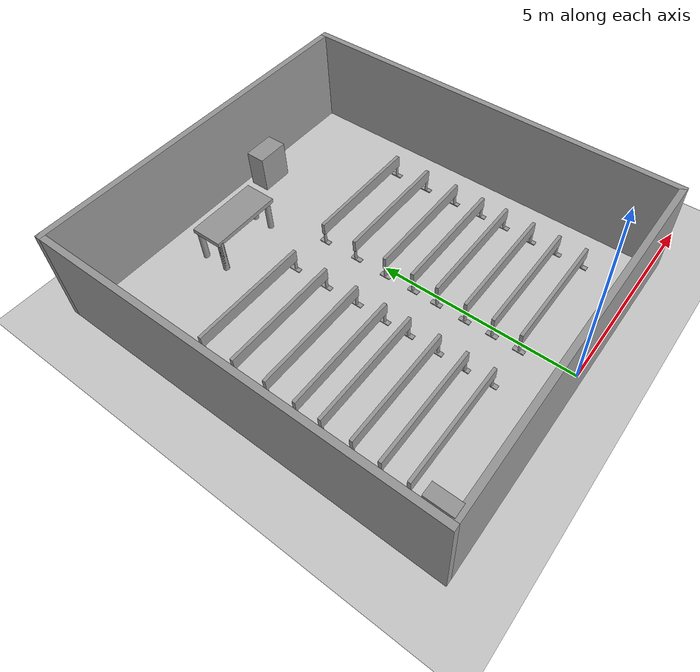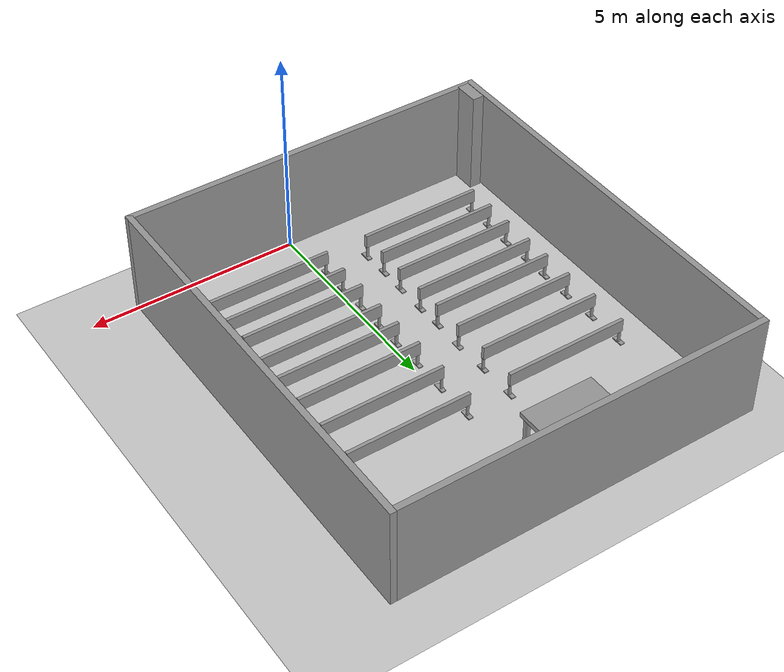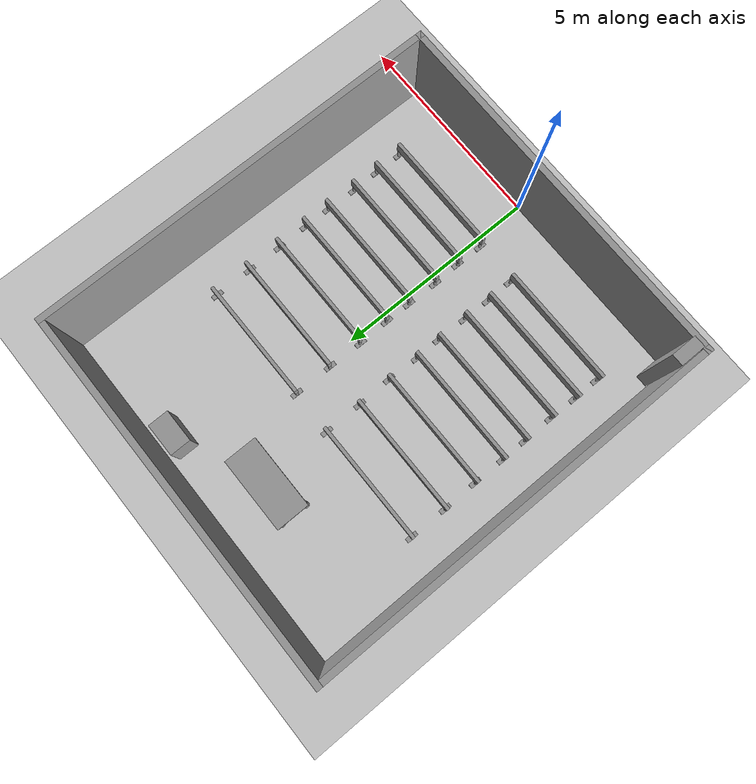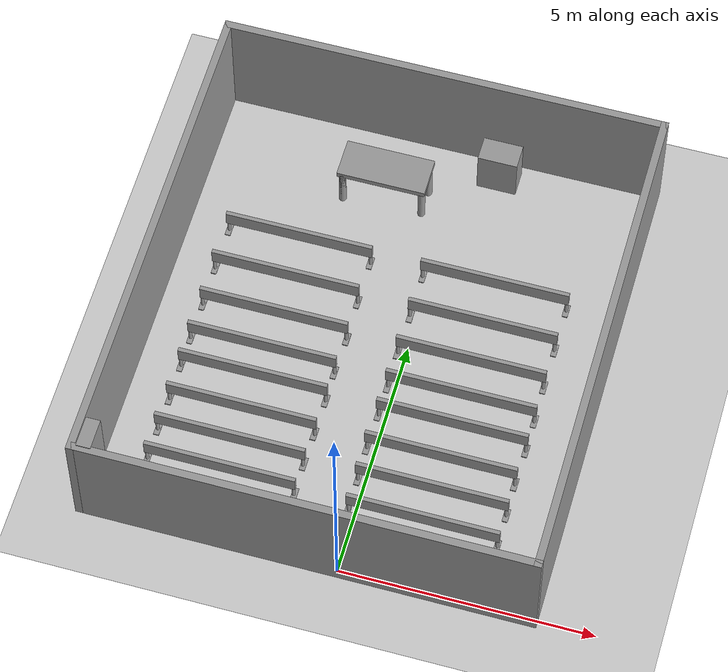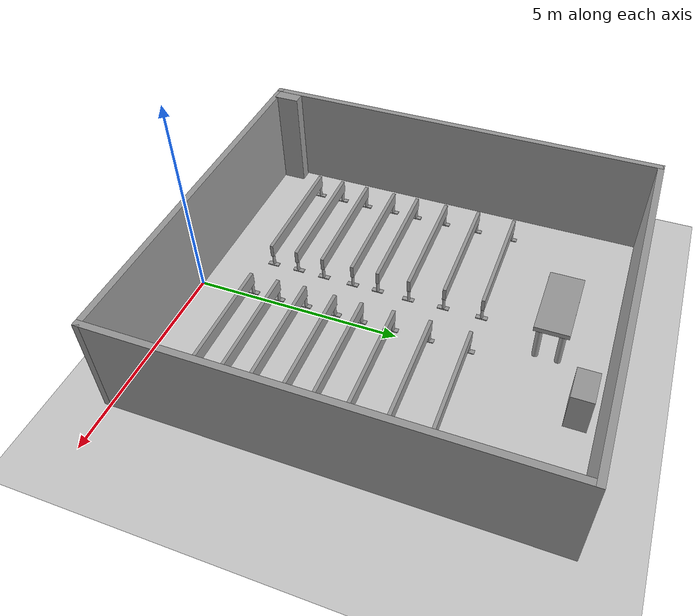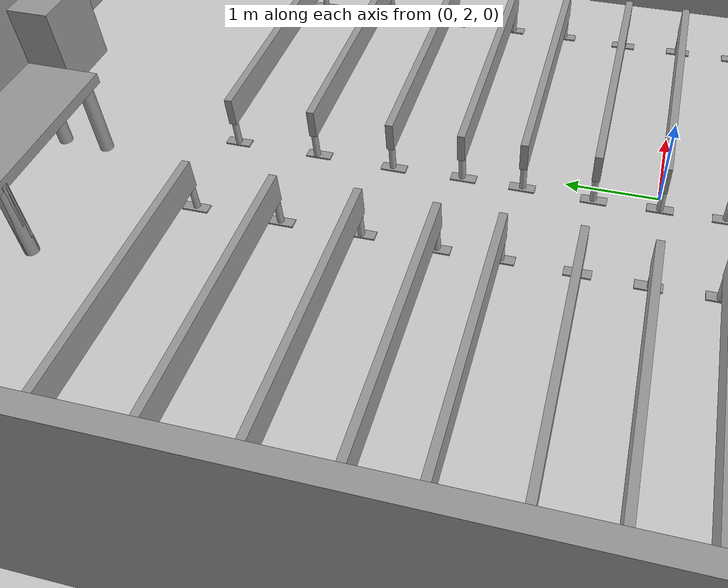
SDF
<sdf version="1.6">
 <world name="default">
  <light name="sun" type="directional">
   <pose>0 0 10 0 -0 0</pose>
   <diffuse>0.8 0.8 0.8 1</diffuse>
   <specular>0.2 0.2 0.2 1</specular>
   <attenuation>
    <range>1000</range>
    <constant>0.9</constant>
    <linear>0.01</linear>
    <quadratic>0.001</quadratic>
   </attenuation>
   <direction>-0.5 0.1 -0.9</direction>
  </light>
  <model name="ground_plane">
   <static>1</static>
   <link name="link">
    <collision name="collision">
     <geometry><plane><normal>0 0 1</normal><size>100 100</size></plane></geometry>
     <surface><friction><ode><mu>100</mu><mu2>50</mu2></ode></friction></surface>
    </collision>
    <visual name="visual">
     <cast_shadows>0</cast_shadows>
     <geometry><plane><normal>0 0 1</normal><size>100 100</size></plane></geometry>
     <material>
      <script><uri>file://media/materials/scripts/gazebo.material</uri><name>Gazebo/Grey</name></script>
     </material>
    </visual>
   </link>
  </model>
  <gravity>0 0 -9.8</gravity>
  <magnetic_field>6e-06 2.3e-05 -4.2e-05</magnetic_field>
  <atmosphere type="adiabatic"/>
  <physics name="default_physics" default="0" type="ode">
   <max_step_size>0.001</max_step_size>
   <real_time_factor>1</real_time_factor>
   <real_time_update_rate>1000</real_time_update_rate>
  </physics>
  <scene><ambient>0.4 0.4 0.4 1</ambient><background>0.7 0.7 0.7 1</background><shadows>1</shadows></scene>
  <spherical_coordinates>
   <surface_model>EARTH_WGS84</surface_model>
   <latitude_deg>0</latitude_deg>
   <longitude_deg>0</longitude_deg>
   <elevation>0</elevation>
   <heading_deg>0</heading_deg>
  </spherical_coordinates>
  <model name="aula">
   <pose>-0.615511 4.86669 0 0 -0 0</pose>
   <link name="Wall_0">
    <collision name="Wall_0_Collision">
     <geometry><box><size>9 0.15 2.5</size></box></geometry>
     <pose>0 0 1.25 0 -0 0</pose>
    </collision>
    <visual name="Wall_0_Visual">
     <pose>0 0 1.25 0 -0 0</pose>
     <geometry><box><size>9 0.15 2.5</size></box></geometry>
     <material>
      <script><uri>file://media/materials/scripts/gazebo.material</uri><name>Gazebo/Grey</name></script>
      <ambient>1 1 1 1</ambient>
     </material>
    </visual>
    <pose>0 4.925 0 0 -0 3.14159</pose>
   </link>
   <link name="Wall_13">
    <collision name="Wall_13_Collision">
     <geometry><box><size>9 0.15 2.5</size></box></geometry>
     <pose>0 0 1.25 0 -0 0</pose>
    </collision>
    <visual name="Wall_13_Visual">
     <pose>0 0 1.25 0 -0 0</pose>
     <geometry><box><size>9 0.15 2.5</size></box></geometry>
     <material>
      <script><uri>file://media/materials/scripts/gazebo.material</uri><name>Gazebo/Grey</name></script>
      <ambient>1 1 1 1</ambient>
     </material>
    </visual>
    <pose>0 -4.925 0 0 -0 3.14159</pose>
   </link>
   <link name="Wall_2">
    <collision name="Wall_2_Collision">
     <geometry><box><size>10 0.15 2.5</size></box></geometry>
     <pose>0 0 1.25 0 -0 0</pose>
    </collision>
    <visual name="Wall_2_Visual">
     <pose>0 0 1.25 0 -0 0</pose>
     <geometry><box><size>10 0.15 2.5</size></box></geometry>
     <material>
      <script><uri>file://media/materials/scripts/gazebo.material</uri><name>Gazebo/Grey</name></script>
      <ambient>1 1 1 1</ambient>
     </material>
    </visual>
    <pose>-4.425 0 0 0 0 -1.5708</pose>
   </link>
   <link name="Wall_7">
    <collision name="Wall_7_Collision">
     <geometry><box><size>10 0.15 2.5</size></box></geometry>
     <pose>0 0 1.25 0 -0 0</pose>
    </collision>
    <visual name="Wall_7_Visual">
     <pose>0 0 1.25 0 -0 0</pose>
     <geometry><box><size>10 0.15 2.5</size></box></geometry>
     <material>
      <script><uri>file://media/materials/scripts/gazebo.material</uri><name>Gazebo/Grey</name></script>
      <ambient>1 1 1 1</ambient>
     </material>
    </visual>
    <pose>4.425 0 0 0 0 -1.5708</pose>
   </link>
   <static>1</static>
  </model>
  <model name="table">
   <link name="link_0">
    <pose>1.8055 0.833362 1.52998 0 -0 0</pose>
    <inertial>
     <mass>0.45487</mass>
     <inertia>
      <ixx>0.089863</ixx>
      <ixy>0</ixy>
      <ixz>0</ixz>
      <iyy>0.241732</iyy>
      <iyz>0</iyz>
      <izz>0.330549</izz>
     </inertia>
    </inertial>
    <visual name="visual">
     <geometry><box><size>1.8 0.8 0.117454</size></box></geometry>
     <material>
      <lighting>1</lighting>
      <script><uri>file://media/materials/scripts/gazebo.material</uri><name>Gazebo/Grey</name></script>
      <ambient>0.3 0.3 0.3 1</ambient>
      <diffuse>0.7 0.7 0.7 1</diffuse>
      <specular>0.01 0.01 0.01 1</specular>
      <emissive>0 0 0 1</emissive>
      <shader type="vertex"><normal_map>__default__</normal_map></shader>
     </material>
    </visual>
    <collision name="collision">
     <geometry><box><size>1.8 0.8 0.117454</size></box></geometry>
     <surface>
      <friction>
       <ode><mu>1</mu><mu2>1</mu2><fdir1>0 0 0</fdir1><slip1>0</slip1><slip2>0</slip2></ode>
       <torsional>
        <coefficient>1</coefficient>
        <patch_radius>0</patch_radius>
        <surface_radius>0</surface_radius>
        <use_patch_radius>1</use_patch_radius>
        <ode><slip>0</slip></ode>
       </torsional>
      </friction>
      <bounce><restitution_coefficient>0</restitution_coefficient><threshold>1e+06</threshold></bounce>
      <contact>
       <collide_without_contact>0</collide_without_contact>
       <collide_without_contact_bitmask>1</collide_without_contact_bitmask>
       <collide_bitmask>1</collide_bitmask>
       <ode>
        <soft_cfm>0</soft_cfm>
        <soft_erp>0.2</soft_erp>
        <kp>1e+13</kp>
        <kd>1</kd>
        <max_vel>0.01</max_vel>
        <min_depth>0</min_depth>
       </ode>
       <bullet>
        <split_impulse>1</split_impulse>
        <split_impulse_penetration_threshold>-0.01</split_impulse_penetration_threshold>
        <soft_cfm>0</soft_cfm>
        <soft_erp>0.2</soft_erp>
        <kp>1e+13</kp>
        <kd>1</kd>
       </bullet>
      </contact>
     </surface>
    </collision>
   </link>
   <link name="link_1">
    <pose>1.00734 0.496856 1.07514 0 -0 0</pose>
    <inertial>
     <mass>0.0339085</mass>
     <inertia>
      <ixx>0.00689116</ixx>
      <ixy>0</ixy>
      <ixz>0</ixz>
      <iyy>0.00689116</iyy>
      <iyz>0</iyz>
      <izz>9.234e-05</izz>
     </inertia>
    </inertial>
    <visual name="visual">
     <geometry><cylinder><radius>0.073807</radius><length>0.900001</length></cylinder></geometry>
     <material>
      <lighting>1</lighting>
      <script><uri>file://media/materials/scripts/gazebo.material</uri><name>Gazebo/Grey</name></script>
      <ambient>0.3 0.3 0.3 1</ambient>
      <diffuse>0.7 0.7 0.7 1</diffuse>
      <specular>0.01 0.01 0.01 1</specular>
      <emissive>0 0 0 1</emissive>
      <shader type="vertex"><normal_map>__default__</normal_map></shader>
     </material>
    </visual>
    <visual name="ModelPreview_0::link_1::visual_1">
     <geometry><cylinder><radius>0.073807</radius><length>0.9</length></cylinder></geometry>
     <material>
      <lighting>1</lighting>
      <script><uri>file://media/materials/scripts/gazebo.material</uri><name>Gazebo/Grey</name></script>
      <ambient>0.3 0.3 0.3 1</ambient>
      <diffuse>0.7 0.7 0.7 1</diffuse>
      <specular>0.01 0.01 0.01 1</specular>
      <emissive>0 0 0 1</emissive>
      <shader type="vertex"><normal_map>__default__</normal_map></shader>
     </material>
    </visual>
    <collision name="collision">
     <geometry><cylinder><radius>0.073807</radius><length>0.900001</length></cylinder></geometry>
     <surface>
      <friction>
       <ode><mu>1</mu><mu2>1</mu2><fdir1>0 0 0</fdir1><slip1>0</slip1><slip2>0</slip2></ode>
       <torsional>
        <coefficient>1</coefficient>
        <patch_radius>0</patch_radius>
        <surface_radius>0</surface_radius>
        <use_patch_radius>1</use_patch_radius>
        <ode><slip>0</slip></ode>
       </torsional>
      </friction>
      <bounce><restitution_coefficient>0</restitution_coefficient><threshold>1e+06</threshold></bounce>
      <contact>
       <collide_without_contact>0</collide_without_contact>
       <collide_without_contact_bitmask>1</collide_without_contact_bitmask>
       <collide_bitmask>1</collide_bitmask>
       <ode>
        <soft_cfm>0</soft_cfm>
        <soft_erp>0.2</soft_erp>
        <kp>1e+13</kp>
        <kd>1</kd>
        <max_vel>0.01</max_vel>
        <min_depth>0</min_depth>
       </ode>
       <bullet>
        <split_impulse>1</split_impulse>
        <split_impulse_penetration_threshold>-0.01</split_impulse_penetration_threshold>
        <soft_cfm>0</soft_cfm>
        <soft_erp>0.2</soft_erp>
        <kp>1e+13</kp>
        <kd>1</kd>
       </bullet>
      </contact>
     </surface>
    </collision>
   </link>
   <link name="link_1_clone">
    <pose>2.61517 0.570568 1.07431 0 -0 0</pose>
    <inertial>
     <mass>0.0339085</mass>
     <inertia>
      <ixx>0.00689116</ixx>
      <ixy>0</ixy>
      <ixz>0</ixz>
      <iyy>0.00689116</iyy>
      <iyz>0</iyz>
      <izz>9.234e-05</izz>
     </inertia>
    </inertial>
    <visual name="visual">
     <geometry><cylinder><radius>0.073807</radius><length>0.9</length></cylinder></geometry>
     <material>
      <lighting>1</lighting>
      <script><uri>file://media/materials/scripts/gazebo.material</uri><name>Gazebo/Grey</name></script>
      <ambient>0.3 0.3 0.3 1</ambient>
      <diffuse>0.7 0.7 0.7 1</diffuse>
      <specular>0.01 0.01 0.01 1</specular>
      <emissive>0 0 0 1</emissive>
      <shader type="vertex"><normal_map>__default__</normal_map></shader>
     </material>
    </visual>
    <collision name="collision">
     <geometry><cylinder><radius>0.073807</radius><length>0.9</length></cylinder></geometry>
     <surface>
      <friction>
       <ode><mu>1</mu><mu2>1</mu2><fdir1>0 0 0</fdir1><slip1>0</slip1><slip2>0</slip2></ode>
       <torsional>
        <coefficient>1</coefficient>
        <patch_radius>0</patch_radius>
        <surface_radius>0</surface_radius>
        <use_patch_radius>1</use_patch_radius>
        <ode><slip>0</slip></ode>
       </torsional>
      </friction>
      <bounce><restitution_coefficient>0</restitution_coefficient><threshold>1e+06</threshold></bounce>
      <contact>
       <collide_without_contact>0</collide_without_contact>
       <collide_without_contact_bitmask>1</collide_without_contact_bitmask>
       <collide_bitmask>1</collide_bitmask>
       <ode>
        <soft_cfm>0</soft_cfm>
        <soft_erp>0.2</soft_erp>
        <kp>1e+13</kp>
        <kd>1</kd>
        <max_vel>0.01</max_vel>
        <min_depth>0</min_depth>
       </ode>
       <bullet>
        <split_impulse>1</split_impulse>
        <split_impulse_penetration_threshold>-0.01</split_impulse_penetration_threshold>
        <soft_cfm>0</soft_cfm>
        <soft_erp>0.2</soft_erp>
        <kp>1e+13</kp>
        <kd>1</kd>
       </bullet>
      </contact>
     </surface>
    </collision>
   </link>
   <link name="link_1_clone_0">
    <pose>2.62457 1.08492 1.0677 0 -0 0</pose>
    <inertial>
     <mass>0.0339085</mass>
     <inertia>
      <ixx>0.00689116</ixx>
      <ixy>0</ixy>
      <ixz>0</ixz>
      <iyy>0.00689116</iyy>
      <iyz>0</iyz>
      <izz>9.234e-05</izz>
     </inertia>
    </inertial>
    <visual name="visual">
     <geometry><cylinder><radius>0.073807</radius><length>0.9</length></cylinder></geometry>
     <material>
      <lighting>1</lighting>
      <script><uri>file://media/materials/scripts/gazebo.material</uri><name>Gazebo/Grey</name></script>
      <ambient>0.3 0.3 0.3 1</ambient>
      <diffuse>0.7 0.7 0.7 1</diffuse>
      <specular>0.01 0.01 0.01 1</specular>
      <emissive>0 0 0 1</emissive>
      <shader type="vertex"><normal_map>__default__</normal_map></shader>
     </material>
    </visual>
    <collision name="collision">
     <geometry><cylinder><radius>0.073807</radius><length>0.9</length></cylinder></geometry>
     <surface>
      <friction>
       <ode><mu>1</mu><mu2>1</mu2><fdir1>0 0 0</fdir1><slip1>0</slip1><slip2>0</slip2></ode>
       <torsional>
        <coefficient>1</coefficient>
        <patch_radius>0</patch_radius>
        <surface_radius>0</surface_radius>
        <use_patch_radius>1</use_patch_radius>
        <ode><slip>0</slip></ode>
       </torsional>
      </friction>
      <bounce><restitution_coefficient>0</restitution_coefficient><threshold>1e+06</threshold></bounce>
      <contact>
       <collide_without_contact>0</collide_without_contact>
       <collide_without_contact_bitmask>1</collide_without_contact_bitmask>
       <collide_bitmask>1</collide_bitmask>
       <ode>
        <soft_cfm>0</soft_cfm>
        <soft_erp>0.2</soft_erp>
        <kp>1e+13</kp>
        <kd>1</kd>
        <max_vel>0.01</max_vel>
        <min_depth>0</min_depth>
       </ode>
       <bullet>
        <split_impulse>1</split_impulse>
        <split_impulse_penetration_threshold>-0.01</split_impulse_penetration_threshold>
        <soft_cfm>0</soft_cfm>
        <soft_erp>0.2</soft_erp>
        <kp>1e+13</kp>
        <kd>1</kd>
       </bullet>
      </contact>
     </surface>
    </collision>
   </link>
   <link name="link_1_clone_1">
    <pose>1.01114 1.15421 1.07072 0 -0 0</pose>
    <inertial>
     <mass>0.0339085</mass>
     <inertia>
      <ixx>0.00689116</ixx>
      <ixy>0</ixy>
      <ixz>0</ixz>
      <iyy>0.00689116</iyy>
      <iyz>0</iyz>
      <izz>9.234e-05</izz>
     </inertia>
    </inertial>
    <visual name="visual">
     <geometry><cylinder><radius>0.073807</radius><length>0.9</length></cylinder></geometry>
     <material>
      <lighting>1</lighting>
      <script><uri>file://media/materials/scripts/gazebo.material</uri><name>Gazebo/Grey</name></script>
      <ambient>0.3 0.3 0.3 1</ambient>
      <diffuse>0.7 0.7 0.7 1</diffuse>
      <specular>0.01 0.01 0.01 1</specular>
      <emissive>0 0 0 1</emissive>
      <shader type="vertex"><normal_map>__default__</normal_map></shader>
     </material>
    </visual>
    <collision name="collision">
     <geometry><cylinder><radius>0.073807</radius><length>0.9</length></cylinder></geometry>
     <surface>
      <friction>
       <ode><mu>1</mu><mu2>1</mu2><fdir1>0 0 0</fdir1><slip1>0</slip1><slip2>0</slip2></ode>
       <torsional>
        <coefficient>1</coefficient>
        <patch_radius>0</patch_radius>
        <surface_radius>0</surface_radius>
        <use_patch_radius>1</use_patch_radius>
        <ode><slip>0</slip></ode>
       </torsional>
      </friction>
      <bounce><restitution_coefficient>0</restitution_coefficient><threshold>1e+06</threshold></bounce>
      <contact>
       <collide_without_contact>0</collide_without_contact>
       <collide_without_contact_bitmask>1</collide_without_contact_bitmask>
       <collide_bitmask>1</collide_bitmask>
       <ode>
        <soft_cfm>0</soft_cfm>
        <soft_erp>0.2</soft_erp>
        <kp>1e+13</kp>
        <kd>1</kd>
        <max_vel>0.01</max_vel>
        <min_depth>0</min_depth>
       </ode>
       <bullet>
        <split_impulse>1</split_impulse>
        <split_impulse_penetration_threshold>-0.01</split_impulse_penetration_threshold>
        <soft_cfm>0</soft_cfm>
        <soft_erp>0.2</soft_erp>
        <kp>1e+13</kp>
        <kd>1</kd>
       </bullet>
      </contact>
     </surface>
    </collision>
   </link>
   <static>1</static>
   <pose>-3.20427 7.53023 -0.629836 0 -0 0</pose>
  </model>
  <model name="banchi">
   <link name="link_3">
    <pose>0.19401 0.058881 0.005926 0 -0 0</pose>
    <inertial>
     <mass>1</mass>
     <inertia>
      <ixx>0.166667</ixx>
      <ixy>0</ixy>
      <ixz>0</ixz>
      <iyy>0.166667</iyy>
      <iyz>0</iyz>
      <izz>0.166667</izz>
     </inertia>
    </inertial>
    <visual name="visual">
     <geometry><box><size>0.8 0.5 1</size></box></geometry>
     <material>
      <lighting>1</lighting>
      <script><uri>file://media/materials/scripts/gazebo.material</uri><name>Gazebo/Grey</name></script>
      <ambient>0.3 0.3 0.3 1</ambient>
      <diffuse>0.7 0.7 0.7 1</diffuse>
      <specular>0.01 0.01 0.01 1</specular>
      <emissive>0 0 0 1</emissive>
      <shader type="vertex"><normal_map>__default__</normal_map></shader>
     </material>
    </visual>
    <collision name="collision">
     <geometry><box><size>0.8 0.5 1</size></box></geometry>
     <surface>
      <friction>
       <ode><mu>1</mu><mu2>1</mu2><fdir1>0 0 0</fdir1><slip1>0</slip1><slip2>0</slip2></ode>
       <torsional>
        <coefficient>1</coefficient>
        <patch_radius>0</patch_radius>
        <surface_radius>0</surface_radius>
        <use_patch_radius>1</use_patch_radius>
        <ode><slip>0</slip></ode>
       </torsional>
      </friction>
      <bounce><restitution_coefficient>0</restitution_coefficient><threshold>1e+06</threshold></bounce>
      <contact>
       <collide_without_contact>0</collide_without_contact>
       <collide_without_contact_bitmask>1</collide_without_contact_bitmask>
       <collide_bitmask>1</collide_bitmask>
       <ode>
        <soft_cfm>0</soft_cfm>
        <soft_erp>0.2</soft_erp>
        <kp>1e+13</kp>
        <kd>1</kd>
        <max_vel>0.01</max_vel>
        <min_depth>0</min_depth>
       </ode>
       <bullet>
        <split_impulse>1</split_impulse>
        <split_impulse_penetration_threshold>-0.01</split_impulse_penetration_threshold>
        <soft_cfm>0</soft_cfm>
        <soft_erp>0.2</soft_erp>
        <kp>1e+13</kp>
        <kd>1</kd>
       </bullet>
      </contact>
     </surface>
    </collision>
   </link>
   <link name="link_0">
    <inertial>
     <mass>0.000785881</mass>
     <inertia>
      <ixx>5.11476e-06</ixx>
      <ixy>0</ixy>
      <ixz>0</ixz>
      <iyy>8.37345e-07</iyy>
      <iyz>0</iyz>
      <izz>5.8658e-06</izz>
     </inertia>
    </inertial>
    <pose>2.2428 -2.55708 -0.495327 0 -0 0</pose>
    <visual name="visual">
     <geometry><box><size>0.110122 0.278282 0.025669</size></box></geometry>
     <material>
      <lighting>1</lighting>
      <script><uri>file://media/materials/scripts/gazebo.material</uri><name>Gazebo/Grey</name></script>
     </material>
    </visual>
    <collision name="collision">
     <geometry><box><size>0.110122 0.278282 0.025669</size></box></geometry>
     <surface>
      <friction>
       <ode><mu>1</mu><mu2>1</mu2><fdir1>0 0 0</fdir1><slip1>0</slip1><slip2>0</slip2></ode>
       <torsional>
        <coefficient>1</coefficient>
        <patch_radius>0</patch_radius>
        <surface_radius>0</surface_radius>
        <use_patch_radius>1</use_patch_radius>
        <ode><slip>0</slip></ode>
       </torsional>
      </friction>
      <bounce><restitution_coefficient>0</restitution_coefficient><threshold>1e+06</threshold></bounce>
      <contact>
       <collide_without_contact>0</collide_without_contact>
       <collide_without_contact_bitmask>1</collide_without_contact_bitmask>
       <collide_bitmask>1</collide_bitmask>
       <ode>
        <soft_cfm>0</soft_cfm>
        <soft_erp>0.2</soft_erp>
        <kp>1e+13</kp>
        <kd>1</kd>
        <max_vel>0.01</max_vel>
        <min_depth>0</min_depth>
       </ode>
       <bullet>
        <split_impulse>1</split_impulse>
        <split_impulse_penetration_threshold>-0.01</split_impulse_penetration_threshold>
        <soft_cfm>0</soft_cfm>
        <soft_erp>0.2</soft_erp>
        <kp>1e+13</kp>
        <kd>1</kd>
       </bullet>
      </contact>
     </surface>
    </collision>
   </link>
   <link name="link_0_clone">
    <inertial>
     <mass>0.000785881</mass>
     <inertia>
      <ixx>5.11476e-06</ixx>
      <ixy>0</ixy>
      <ixz>0</ixz>
      <iyy>8.37345e-07</iyy>
      <iyz>0</iyz>
      <izz>5.8658e-06</izz>
     </inertia>
    </inertial>
    <pose>2.245 -3.48891 -0.495327 0 -0 0</pose>
    <visual name="visual">
     <geometry><box><size>0.110122 0.278282 0.025669</size></box></geometry>
     <material>
      <lighting>1</lighting>
      <script><uri>file://media/materials/scripts/gazebo.material</uri><name>Gazebo/Grey</name></script>
      <shader type="pixel"/>
     </material>
    </visual>
    <collision name="collision">
     <geometry><box><size>0.110122 0.278282 0.025669</size></box></geometry>
     <surface>
      <friction>
       <ode><mu>1</mu><mu2>1</mu2><fdir1>0 0 0</fdir1><slip1>0</slip1><slip2>0</slip2></ode>
       <torsional>
        <coefficient>1</coefficient>
        <patch_radius>0</patch_radius>
        <surface_radius>0</surface_radius>
        <use_patch_radius>1</use_patch_radius>
        <ode><slip>0</slip></ode>
       </torsional>
      </friction>
      <bounce><restitution_coefficient>0</restitution_coefficient><threshold>1e+06</threshold></bounce>
      <contact>
       <collide_without_contact>0</collide_without_contact>
       <collide_without_contact_bitmask>1</collide_without_contact_bitmask>
       <collide_bitmask>1</collide_bitmask>
       <ode>
        <soft_cfm>0</soft_cfm>
        <soft_erp>0.2</soft_erp>
        <kp>1e+13</kp>
        <kd>1</kd>
        <max_vel>0.01</max_vel>
        <min_depth>0</min_depth>
       </ode>
       <bullet>
        <split_impulse>1</split_impulse>
        <split_impulse_penetration_threshold>-0.01</split_impulse_penetration_threshold>
        <soft_cfm>0</soft_cfm>
        <soft_erp>0.2</soft_erp>
        <kp>1e+13</kp>
        <kd>1</kd>
       </bullet>
      </contact>
     </surface>
    </collision>
   </link>
   <link name="link_0_clone_0">
    <inertial>
     <mass>0.000785881</mass>
     <inertia>
      <ixx>5.11476e-06</ixx>
      <ixy>0</ixy>
      <ixz>0</ixz>
      <iyy>8.37345e-07</iyy>
      <iyz>0</iyz>
      <izz>5.8658e-06</izz>
     </inertia>
    </inertial>
    <pose>2.24403 -4.35243 -0.495327 0 -0 0</pose>
    <visual name="visual">
     <geometry><box><size>0.110122 0.278282 0.025669</size></box></geometry>
     <material>
      <lighting>1</lighting>
      <script><uri>file://media/materials/scripts/gazebo.material</uri><name>Gazebo/Grey</name></script>
      <shader type="pixel"/>
     </material>
    </visual>
    <collision name="collision">
     <geometry><box><size>0.110122 0.278282 0.025669</size></box></geometry>
     <surface>
      <friction>
       <ode><mu>1</mu><mu2>1</mu2><fdir1>0 0 0</fdir1><slip1>0</slip1><slip2>0</slip2></ode>
       <torsional>
        <coefficient>1</coefficient>
        <patch_radius>0</patch_radius>
        <surface_radius>0</surface_radius>
        <use_patch_radius>1</use_patch_radius>
        <ode><slip>0</slip></ode>
       </torsional>
      </friction>
      <bounce><restitution_coefficient>0</restitution_coefficient><threshold>1e+06</threshold></bounce>
      <contact>
       <collide_without_contact>0</collide_without_contact>
       <collide_without_contact_bitmask>1</collide_without_contact_bitmask>
       <collide_bitmask>1</collide_bitmask>
       <ode>
        <soft_cfm>0</soft_cfm>
        <soft_erp>0.2</soft_erp>
        <kp>1e+13</kp>
        <kd>1</kd>
        <max_vel>0.01</max_vel>
        <min_depth>0</min_depth>
       </ode>
       <bullet>
        <split_impulse>1</split_impulse>
        <split_impulse_penetration_threshold>-0.01</split_impulse_penetration_threshold>
        <soft_cfm>0</soft_cfm>
        <soft_erp>0.2</soft_erp>
        <kp>1e+13</kp>
        <kd>1</kd>
       </bullet>
      </contact>
     </surface>
    </collision>
   </link>
   <link name="link_0_clone_1">
    <inertial>
     <mass>0.000785881</mass>
     <inertia>
      <ixx>5.11476e-06</ixx>
      <ixy>0</ixy>
      <ixz>0</ixz>
      <iyy>8.37345e-07</iyy>
      <iyz>0</iyz>
      <izz>5.8658e-06</izz>
     </inertia>
    </inertial>
    <pose>2.25812 -5.12778 -0.495327 0 -0 0</pose>
    <visual name="visual">
     <geometry><box><size>0.110122 0.278282 0.025669</size></box></geometry>
     <material>
      <lighting>1</lighting>
      <script><uri>file://media/materials/scripts/gazebo.material</uri><name>Gazebo/Grey</name></script>
      <shader type="pixel"/>
     </material>
    </visual>
    <collision name="collision">
     <geometry><box><size>0.110122 0.278282 0.025669</size></box></geometry>
     <surface>
      <friction>
       <ode><mu>1</mu><mu2>1</mu2><fdir1>0 0 0</fdir1><slip1>0</slip1><slip2>0</slip2></ode>
       <torsional>
        <coefficient>1</coefficient>
        <patch_radius>0</patch_radius>
        <surface_radius>0</surface_radius>
        <use_patch_radius>1</use_patch_radius>
        <ode><slip>0</slip></ode>
       </torsional>
      </friction>
      <bounce><restitution_coefficient>0</restitution_coefficient><threshold>1e+06</threshold></bounce>
      <contact>
       <collide_without_contact>0</collide_without_contact>
       <collide_without_contact_bitmask>1</collide_without_contact_bitmask>
       <collide_bitmask>1</collide_bitmask>
       <ode>
        <soft_cfm>0</soft_cfm>
        <soft_erp>0.2</soft_erp>
        <kp>1e+13</kp>
        <kd>1</kd>
        <max_vel>0.01</max_vel>
        <min_depth>0</min_depth>
       </ode>
       <bullet>
        <split_impulse>1</split_impulse>
        <split_impulse_penetration_threshold>-0.01</split_impulse_penetration_threshold>
        <soft_cfm>0</soft_cfm>
        <soft_erp>0.2</soft_erp>
        <kp>1e+13</kp>
        <kd>1</kd>
       </bullet>
      </contact>
     </surface>
    </collision>
   </link>
   <link name="link_0_clone_10">
    <inertial>
     <mass>0.000785881</mass>
     <inertia>
      <ixx>5.11476e-06</ixx>
      <ixy>0</ixy>
      <ixz>0</ixz>
      <iyy>8.37345e-07</iyy>
      <iyz>0</iyz>
      <izz>5.8658e-06</izz>
     </inertia>
    </inertial>
    <pose>-0.67038 -5.15029 -0.495327 0 -0 0</pose>
    <visual name="visual">
     <geometry><box><size>0.110122 0.278282 0.025669</size></box></geometry>
     <material>
      <lighting>1</lighting>
      <script><uri>file://media/materials/scripts/gazebo.material</uri><name>Gazebo/Grey</name></script>
      <shader type="pixel"/>
     </material>
    </visual>
    <collision name="collision">
     <geometry><box><size>0.110122 0.278282 0.025669</size></box></geometry>
     <surface>
      <friction>
       <ode><mu>1</mu><mu2>1</mu2><fdir1>0 0 0</fdir1><slip1>0</slip1><slip2>0</slip2></ode>
       <torsional>
        <coefficient>1</coefficient>
        <patch_radius>0</patch_radius>
        <surface_radius>0</surface_radius>
        <use_patch_radius>1</use_patch_radius>
        <ode><slip>0</slip></ode>
       </torsional>
      </friction>
      <bounce><restitution_coefficient>0</restitution_coefficient><threshold>1e+06</threshold></bounce>
      <contact>
       <collide_without_contact>0</collide_without_contact>
       <collide_without_contact_bitmask>1</collide_without_contact_bitmask>
       <collide_bitmask>1</collide_bitmask>
       <ode>
        <soft_cfm>0</soft_cfm>
        <soft_erp>0.2</soft_erp>
        <kp>1e+13</kp>
        <kd>1</kd>
        <max_vel>0.01</max_vel>
        <min_depth>0</min_depth>
       </ode>
       <bullet>
        <split_impulse>1</split_impulse>
        <split_impulse_penetration_threshold>-0.01</split_impulse_penetration_threshold>
        <soft_cfm>0</soft_cfm>
        <soft_erp>0.2</soft_erp>
        <kp>1e+13</kp>
        <kd>1</kd>
       </bullet>
      </contact>
     </surface>
    </collision>
   </link>
   <link name="link_0_clone_11">
    <inertial>
     <mass>0.000785881</mass>
     <inertia>
      <ixx>5.11476e-06</ixx>
      <ixy>0</ixy>
      <ixz>0</ixz>
      <iyy>8.37345e-07</iyy>
      <iyz>0</iyz>
      <izz>5.8658e-06</izz>
     </inertia>
    </inertial>
    <pose>-0.686084 -4.37283 -0.495327 0 -0 0</pose>
    <visual name="visual">
     <geometry><box><size>0.110122 0.278282 0.025669</size></box></geometry>
     <material>
      <lighting>1</lighting>
      <script><uri>file://media/materials/scripts/gazebo.material</uri><name>Gazebo/Grey</name></script>
      <shader type="pixel"/>
     </material>
    </visual>
    <collision name="collision">
     <geometry><box><size>0.110122 0.278282 0.025669</size></box></geometry>
     <surface>
      <friction>
       <ode><mu>1</mu><mu2>1</mu2><fdir1>0 0 0</fdir1><slip1>0</slip1><slip2>0</slip2></ode>
       <torsional>
        <coefficient>1</coefficient>
        <patch_radius>0</patch_radius>
        <surface_radius>0</surface_radius>
        <use_patch_radius>1</use_patch_radius>
        <ode><slip>0</slip></ode>
       </torsional>
      </friction>
      <bounce><restitution_coefficient>0</restitution_coefficient><threshold>1e+06</threshold></bounce>
      <contact>
       <collide_without_contact>0</collide_without_contact>
       <collide_without_contact_bitmask>1</collide_without_contact_bitmask>
       <collide_bitmask>1</collide_bitmask>
       <ode>
        <soft_cfm>0</soft_cfm>
        <soft_erp>0.2</soft_erp>
        <kp>1e+13</kp>
        <kd>1</kd>
        <max_vel>0.01</max_vel>
        <min_depth>0</min_depth>
       </ode>
       <bullet>
        <split_impulse>1</split_impulse>
        <split_impulse_penetration_threshold>-0.01</split_impulse_penetration_threshold>
        <soft_cfm>0</soft_cfm>
        <soft_erp>0.2</soft_erp>
        <kp>1e+13</kp>
        <kd>1</kd>
       </bullet>
      </contact>
     </surface>
    </collision>
   </link>
   <link name="link_0_clone_11_clone">
    <inertial>
     <mass>0.000785881</mass>
     <inertia>
      <ixx>5.11476e-06</ixx>
      <ixy>0</ixy>
      <ixz>0</ixz>
      <iyy>8.37345e-07</iyy>
      <iyz>0</iyz>
      <izz>5.8658e-06</izz>
     </inertia>
    </inertial>
    <pose>-0.669518 -3.50617 -0.495327 0 -0 0</pose>
    <visual name="visual">
     <geometry><box><size>0.110122 0.278282 0.025669</size></box></geometry>
     <material>
      <lighting>1</lighting>
      <script><uri>file://media/materials/scripts/gazebo.material</uri><name>Gazebo/Grey</name></script>
      <shader type="pixel"/>
     </material>
    </visual>
    <collision name="collision">
     <geometry><box><size>0.110122 0.278282 0.025669</size></box></geometry>
     <surface>
      <friction>
       <ode><mu>1</mu><mu2>1</mu2><fdir1>0 0 0</fdir1><slip1>0</slip1><slip2>0</slip2></ode>
       <torsional>
        <coefficient>1</coefficient>
        <patch_radius>0</patch_radius>
        <surface_radius>0</surface_radius>
        <use_patch_radius>1</use_patch_radius>
        <ode><slip>0</slip></ode>
       </torsional>
      </friction>
      <bounce><restitution_coefficient>0</restitution_coefficient><threshold>1e+06</threshold></bounce>
      <contact>
       <collide_without_contact>0</collide_without_contact>
       <collide_without_contact_bitmask>1</collide_without_contact_bitmask>
       <collide_bitmask>1</collide_bitmask>
       <ode>
        <soft_cfm>0</soft_cfm>
        <soft_erp>0.2</soft_erp>
        <kp>1e+13</kp>
        <kd>1</kd>
        <max_vel>0.01</max_vel>
        <min_depth>0</min_depth>
       </ode>
       <bullet>
        <split_impulse>1</split_impulse>
        <split_impulse_penetration_threshold>-0.01</split_impulse_penetration_threshold>
        <soft_cfm>0</soft_cfm>
        <soft_erp>0.2</soft_erp>
        <kp>1e+13</kp>
        <kd>1</kd>
       </bullet>
      </contact>
     </surface>
    </collision>
   </link>
   <link name="link_0_clone_13">
    <inertial>
     <mass>0.000785881</mass>
     <inertia>
      <ixx>5.11476e-06</ixx>
      <ixy>0</ixy>
      <ixz>0</ixz>
      <iyy>8.37345e-07</iyy>
      <iyz>0</iyz>
      <izz>5.8658e-06</izz>
     </inertia>
    </inertial>
    <pose>-0.6754 -2.55339 -0.495327 0 -0 0</pose>
    <visual name="visual">
     <geometry><box><size>0.110122 0.278282 0.025669</size></box></geometry>
     <material>
      <lighting>1</lighting>
      <script><uri>file://media/materials/scripts/gazebo.material</uri><name>Gazebo/Grey</name></script>
      <shader type="pixel"/>
     </material>
    </visual>
    <collision name="collision">
     <geometry><box><size>0.110122 0.278282 0.025669</size></box></geometry>
     <surface>
      <friction>
       <ode><mu>1</mu><mu2>1</mu2><fdir1>0 0 0</fdir1><slip1>0</slip1><slip2>0</slip2></ode>
       <torsional>
        <coefficient>1</coefficient>
        <patch_radius>0</patch_radius>
        <surface_radius>0</surface_radius>
        <use_patch_radius>1</use_patch_radius>
        <ode><slip>0</slip></ode>
       </torsional>
      </friction>
      <bounce><restitution_coefficient>0</restitution_coefficient><threshold>1e+06</threshold></bounce>
      <contact>
       <collide_without_contact>0</collide_without_contact>
       <collide_without_contact_bitmask>1</collide_without_contact_bitmask>
       <collide_bitmask>1</collide_bitmask>
       <ode>
        <soft_cfm>0</soft_cfm>
        <soft_erp>0.2</soft_erp>
        <kp>1e+13</kp>
        <kd>1</kd>
        <max_vel>0.01</max_vel>
        <min_depth>0</min_depth>
       </ode>
       <bullet>
        <split_impulse>1</split_impulse>
        <split_impulse_penetration_threshold>-0.01</split_impulse_penetration_threshold>
        <soft_cfm>0</soft_cfm>
        <soft_erp>0.2</soft_erp>
        <kp>1e+13</kp>
        <kd>1</kd>
       </bullet>
      </contact>
     </surface>
    </collision>
   </link>
   <link name="link_0_clone_14">
    <inertial>
     <mass>0.000785881</mass>
     <inertia>
      <ixx>5.11476e-06</ixx>
      <ixy>0</ixy>
      <ixz>0</ixz>
      <iyy>8.37345e-07</iyy>
      <iyz>0</iyz>
      <izz>5.8658e-06</izz>
     </inertia>
    </inertial>
    <pose>-1.75959 -2.54035 -0.495327 0 -0 0</pose>
    <visual name="visual">
     <geometry><box><size>0.110122 0.278282 0.025669</size></box></geometry>
     <material>
      <lighting>1</lighting>
      <script><uri>file://media/materials/scripts/gazebo.material</uri><name>Gazebo/Grey</name></script>
      <shader type="pixel"/>
     </material>
    </visual>
    <collision name="collision">
     <geometry><box><size>0.110122 0.278282 0.025669</size></box></geometry>
     <surface>
      <friction>
       <ode><mu>1</mu><mu2>1</mu2><fdir1>0 0 0</fdir1><slip1>0</slip1><slip2>0</slip2></ode>
       <torsional>
        <coefficient>1</coefficient>
        <patch_radius>0</patch_radius>
        <surface_radius>0</surface_radius>
        <use_patch_radius>1</use_patch_radius>
        <ode><slip>0</slip></ode>
       </torsional>
      </friction>
      <bounce><restitution_coefficient>0</restitution_coefficient><threshold>1e+06</threshold></bounce>
      <contact>
       <collide_without_contact>0</collide_without_contact>
       <collide_without_contact_bitmask>1</collide_without_contact_bitmask>
       <collide_bitmask>1</collide_bitmask>
       <ode>
        <soft_cfm>0</soft_cfm>
        <soft_erp>0.2</soft_erp>
        <kp>1e+13</kp>
        <kd>1</kd>
        <max_vel>0.01</max_vel>
        <min_depth>0</min_depth>
       </ode>
       <bullet>
        <split_impulse>1</split_impulse>
        <split_impulse_penetration_threshold>-0.01</split_impulse_penetration_threshold>
        <soft_cfm>0</soft_cfm>
        <soft_erp>0.2</soft_erp>
        <kp>1e+13</kp>
        <kd>1</kd>
       </bullet>
      </contact>
     </surface>
    </collision>
   </link>
   <link name="link_0_clone_15">
    <inertial>
     <mass>0.000785881</mass>
     <inertia>
      <ixx>5.11476e-06</ixx>
      <ixy>0</ixy>
      <ixz>0</ixz>
      <iyy>8.37345e-07</iyy>
      <iyz>0</iyz>
      <izz>5.8658e-06</izz>
     </inertia>
    </inertial>
    <pose>-1.75172 -3.47821 -0.495327 0 -0 0</pose>
    <visual name="visual">
     <geometry><box><size>0.110122 0.278282 0.025669</size></box></geometry>
     <material>
      <lighting>1</lighting>
      <script><uri>file://media/materials/scripts/gazebo.material</uri><name>Gazebo/Grey</name></script>
      <shader type="pixel"/>
     </material>
    </visual>
    <collision name="collision">
     <geometry><box><size>0.110122 0.278282 0.025669</size></box></geometry>
     <surface>
      <friction>
       <ode><mu>1</mu><mu2>1</mu2><fdir1>0 0 0</fdir1><slip1>0</slip1><slip2>0</slip2></ode>
       <torsional>
        <coefficient>1</coefficient>
        <patch_radius>0</patch_radius>
        <surface_radius>0</surface_radius>
        <use_patch_radius>1</use_patch_radius>
        <ode><slip>0</slip></ode>
       </torsional>
      </friction>
      <bounce><restitution_coefficient>0</restitution_coefficient><threshold>1e+06</threshold></bounce>
      <contact>
       <collide_without_contact>0</collide_without_contact>
       <collide_without_contact_bitmask>1</collide_without_contact_bitmask>
       <collide_bitmask>1</collide_bitmask>
       <ode>
        <soft_cfm>0</soft_cfm>
        <soft_erp>0.2</soft_erp>
        <kp>1e+13</kp>
        <kd>1</kd>
        <max_vel>0.01</max_vel>
        <min_depth>0</min_depth>
       </ode>
       <bullet>
        <split_impulse>1</split_impulse>
        <split_impulse_penetration_threshold>-0.01</split_impulse_penetration_threshold>
        <soft_cfm>0</soft_cfm>
        <soft_erp>0.2</soft_erp>
        <kp>1e+13</kp>
        <kd>1</kd>
       </bullet>
      </contact>
     </surface>
    </collision>
   </link>
   <link name="link_0_clone_16">
    <inertial>
     <mass>0.000785881</mass>
     <inertia>
      <ixx>5.11476e-06</ixx>
      <ixy>0</ixy>
      <ixz>0</ixz>
      <iyy>8.37345e-07</iyy>
      <iyz>0</iyz>
      <izz>5.8658e-06</izz>
     </inertia>
    </inertial>
    <pose>-1.72573 -4.34491 -0.495327 0 -0 0</pose>
    <visual name="visual">
     <geometry><box><size>0.110122 0.278282 0.025669</size></box></geometry>
     <material>
      <lighting>1</lighting>
      <script><uri>file://media/materials/scripts/gazebo.material</uri><name>Gazebo/Grey</name></script>
      <shader type="pixel"/>
     </material>
    </visual>
    <collision name="collision">
     <geometry><box><size>0.110122 0.278282 0.025669</size></box></geometry>
     <surface>
      <friction>
       <ode><mu>1</mu><mu2>1</mu2><fdir1>0 0 0</fdir1><slip1>0</slip1><slip2>0</slip2></ode>
       <torsional>
        <coefficient>1</coefficient>
        <patch_radius>0</patch_radius>
        <surface_radius>0</surface_radius>
        <use_patch_radius>1</use_patch_radius>
        <ode><slip>0</slip></ode>
       </torsional>
      </friction>
      <bounce><restitution_coefficient>0</restitution_coefficient><threshold>1e+06</threshold></bounce>
      <contact>
       <collide_without_contact>0</collide_without_contact>
       <collide_without_contact_bitmask>1</collide_without_contact_bitmask>
       <collide_bitmask>1</collide_bitmask>
       <ode>
        <soft_cfm>0</soft_cfm>
        <soft_erp>0.2</soft_erp>
        <kp>1e+13</kp>
        <kd>1</kd>
        <max_vel>0.01</max_vel>
        <min_depth>0</min_depth>
       </ode>
       <bullet>
        <split_impulse>1</split_impulse>
        <split_impulse_penetration_threshold>-0.01</split_impulse_penetration_threshold>
        <soft_cfm>0</soft_cfm>
        <soft_erp>0.2</soft_erp>
        <kp>1e+13</kp>
        <kd>1</kd>
       </bullet>
      </contact>
     </surface>
    </collision>
   </link>
   <link name="link_0_clone_17">
    <inertial>
     <mass>0.000785881</mass>
     <inertia>
      <ixx>5.11476e-06</ixx>
      <ixy>0</ixy>
      <ixz>0</ixz>
      <iyy>8.37345e-07</iyy>
      <iyz>0</iyz>
      <izz>5.8658e-06</izz>
     </inertia>
    </inertial>
    <pose>-1.74948 -5.13394 -0.495327 0 -0 0</pose>
    <visual name="visual">
     <geometry><box><size>0.110122 0.278282 0.025669</size></box></geometry>
     <material>
      <lighting>1</lighting>
      <script><uri>file://media/materials/scripts/gazebo.material</uri><name>Gazebo/Grey</name></script>
      <shader type="pixel"/>
     </material>
    </visual>
    <collision name="collision">
     <geometry><box><size>0.110122 0.278282 0.025669</size></box></geometry>
     <surface>
      <friction>
       <ode><mu>1</mu><mu2>1</mu2><fdir1>0 0 0</fdir1><slip1>0</slip1><slip2>0</slip2></ode>
       <torsional>
        <coefficient>1</coefficient>
        <patch_radius>0</patch_radius>
        <surface_radius>0</surface_radius>
        <use_patch_radius>1</use_patch_radius>
        <ode><slip>0</slip></ode>
       </torsional>
      </friction>
      <bounce><restitution_coefficient>0</restitution_coefficient><threshold>1e+06</threshold></bounce>
      <contact>
       <collide_without_contact>0</collide_without_contact>
       <collide_without_contact_bitmask>1</collide_without_contact_bitmask>
       <collide_bitmask>1</collide_bitmask>
       <ode>
        <soft_cfm>0</soft_cfm>
        <soft_erp>0.2</soft_erp>
        <kp>1e+13</kp>
        <kd>1</kd>
        <max_vel>0.01</max_vel>
        <min_depth>0</min_depth>
       </ode>
       <bullet>
        <split_impulse>1</split_impulse>
        <split_impulse_penetration_threshold>-0.01</split_impulse_penetration_threshold>
        <soft_cfm>0</soft_cfm>
        <soft_erp>0.2</soft_erp>
        <kp>1e+13</kp>
        <kd>1</kd>
       </bullet>
      </contact>
     </surface>
    </collision>
   </link>
   <link name="link_0_clone_18">
    <inertial>
     <mass>0.000785881</mass>
     <inertia>
      <ixx>5.11476e-06</ixx>
      <ixy>0</ixy>
      <ixz>0</ixz>
      <iyy>8.37345e-07</iyy>
      <iyz>0</iyz>
      <izz>5.8658e-06</izz>
     </inertia>
    </inertial>
    <pose>-1.73682 -5.78102 -0.495327 0 -0 0</pose>
    <visual name="visual">
     <geometry><box><size>0.110122 0.278282 0.025669</size></box></geometry>
     <material>
      <lighting>1</lighting>
      <script><uri>file://media/materials/scripts/gazebo.material</uri><name>Gazebo/Grey</name></script>
      <shader type="pixel"/>
     </material>
    </visual>
    <collision name="collision">
     <geometry><box><size>0.110122 0.278282 0.025669</size></box></geometry>
     <surface>
      <friction>
       <ode><mu>1</mu><mu2>1</mu2><fdir1>0 0 0</fdir1><slip1>0</slip1><slip2>0</slip2></ode>
       <torsional>
        <coefficient>1</coefficient>
        <patch_radius>0</patch_radius>
        <surface_radius>0</surface_radius>
        <use_patch_radius>1</use_patch_radius>
        <ode><slip>0</slip></ode>
       </torsional>
      </friction>
      <bounce><restitution_coefficient>0</restitution_coefficient><threshold>1e+06</threshold></bounce>
      <contact>
       <collide_without_contact>0</collide_without_contact>
       <collide_without_contact_bitmask>1</collide_without_contact_bitmask>
       <collide_bitmask>1</collide_bitmask>
       <ode>
        <soft_cfm>0</soft_cfm>
        <soft_erp>0.2</soft_erp>
        <kp>1e+13</kp>
        <kd>1</kd>
        <max_vel>0.01</max_vel>
        <min_depth>0</min_depth>
       </ode>
       <bullet>
        <split_impulse>1</split_impulse>
        <split_impulse_penetration_threshold>-0.01</split_impulse_penetration_threshold>
        <soft_cfm>0</soft_cfm>
        <soft_erp>0.2</soft_erp>
        <kp>1e+13</kp>
        <kd>1</kd>
       </bullet>
      </contact>
     </surface>
    </collision>
   </link>
   <link name="link_0_clone_19">
    <inertial>
     <mass>0.000785881</mass>
     <inertia>
      <ixx>5.11476e-06</ixx>
      <ixy>0</ixy>
      <ixz>0</ixz>
      <iyy>8.37345e-07</iyy>
      <iyz>0</iyz>
      <izz>5.8658e-06</izz>
     </inertia>
    </inertial>
    <pose>-1.74049 -6.54069 -0.495327 0 -0 0</pose>
    <visual name="visual">
     <geometry><box><size>0.110122 0.278282 0.025669</size></box></geometry>
     <material>
      <lighting>1</lighting>
      <script><uri>file://media/materials/scripts/gazebo.material</uri><name>Gazebo/Grey</name></script>
      <shader type="pixel"/>
     </material>
    </visual>
    <collision name="collision">
     <geometry><box><size>0.110122 0.278282 0.025669</size></box></geometry>
     <surface>
      <friction>
       <ode><mu>1</mu><mu2>1</mu2><fdir1>0 0 0</fdir1><slip1>0</slip1><slip2>0</slip2></ode>
       <torsional>
        <coefficient>1</coefficient>
        <patch_radius>0</patch_radius>
        <surface_radius>0</surface_radius>
        <use_patch_radius>1</use_patch_radius>
        <ode><slip>0</slip></ode>
       </torsional>
      </friction>
      <bounce><restitution_coefficient>0</restitution_coefficient><threshold>1e+06</threshold></bounce>
      <contact>
       <collide_without_contact>0</collide_without_contact>
       <collide_without_contact_bitmask>1</collide_without_contact_bitmask>
       <collide_bitmask>1</collide_bitmask>
       <ode>
        <soft_cfm>0</soft_cfm>
        <soft_erp>0.2</soft_erp>
        <kp>1e+13</kp>
        <kd>1</kd>
        <max_vel>0.01</max_vel>
        <min_depth>0</min_depth>
       </ode>
       <bullet>
        <split_impulse>1</split_impulse>
        <split_impulse_penetration_threshold>-0.01</split_impulse_penetration_threshold>
        <soft_cfm>0</soft_cfm>
        <soft_erp>0.2</soft_erp>
        <kp>1e+13</kp>
        <kd>1</kd>
       </bullet>
      </contact>
     </surface>
    </collision>
   </link>
   <link name="link_0_clone_2">
    <inertial>
     <mass>0.000785881</mass>
     <inertia>
      <ixx>5.11476e-06</ixx>
      <ixy>0</ixy>
      <ixz>0</ixz>
      <iyy>8.37345e-07</iyy>
      <iyz>0</iyz>
      <izz>5.8658e-06</izz>
     </inertia>
    </inertial>
    <pose>2.25946 -5.79798 -0.495327 0 -0 0</pose>
    <visual name="visual">
     <geometry><box><size>0.110122 0.278282 0.025669</size></box></geometry>
     <material>
      <lighting>1</lighting>
      <script><uri>file://media/materials/scripts/gazebo.material</uri><name>Gazebo/Grey</name></script>
      <shader type="pixel"/>
     </material>
    </visual>
    <collision name="collision">
     <geometry><box><size>0.110122 0.278282 0.025669</size></box></geometry>
     <surface>
      <friction>
       <ode><mu>1</mu><mu2>1</mu2><fdir1>0 0 0</fdir1><slip1>0</slip1><slip2>0</slip2></ode>
       <torsional>
        <coefficient>1</coefficient>
        <patch_radius>0</patch_radius>
        <surface_radius>0</surface_radius>
        <use_patch_radius>1</use_patch_radius>
        <ode><slip>0</slip></ode>
       </torsional>
      </friction>
      <bounce><restitution_coefficient>0</restitution_coefficient><threshold>1e+06</threshold></bounce>
      <contact>
       <collide_without_contact>0</collide_without_contact>
       <collide_without_contact_bitmask>1</collide_without_contact_bitmask>
       <collide_bitmask>1</collide_bitmask>
       <ode>
        <soft_cfm>0</soft_cfm>
        <soft_erp>0.2</soft_erp>
        <kp>1e+13</kp>
        <kd>1</kd>
        <max_vel>0.01</max_vel>
        <min_depth>0</min_depth>
       </ode>
       <bullet>
        <split_impulse>1</split_impulse>
        <split_impulse_penetration_threshold>-0.01</split_impulse_penetration_threshold>
        <soft_cfm>0</soft_cfm>
        <soft_erp>0.2</soft_erp>
        <kp>1e+13</kp>
        <kd>1</kd>
       </bullet>
      </contact>
     </surface>
    </collision>
   </link>
   <link name="link_0_clone_20">
    <inertial>
     <mass>0.000785881</mass>
     <inertia>
      <ixx>5.11476e-06</ixx>
      <ixy>0</ixy>
      <ixz>0</ixz>
      <iyy>8.37345e-07</iyy>
      <iyz>0</iyz>
      <izz>5.8658e-06</izz>
     </inertia>
    </inertial>
    <pose>-1.75164 -7.22714 -0.495327 0 -0 0</pose>
    <visual name="visual">
     <geometry><box><size>0.110122 0.278282 0.025669</size></box></geometry>
     <material>
      <lighting>1</lighting>
      <script><uri>file://media/materials/scripts/gazebo.material</uri><name>Gazebo/Grey</name></script>
      <shader type="pixel"/>
     </material>
    </visual>
    <collision name="collision">
     <geometry><box><size>0.110122 0.278282 0.025669</size></box></geometry>
     <surface>
      <friction>
       <ode><mu>1</mu><mu2>1</mu2><fdir1>0 0 0</fdir1><slip1>0</slip1><slip2>0</slip2></ode>
       <torsional>
        <coefficient>1</coefficient>
        <patch_radius>0</patch_radius>
        <surface_radius>0</surface_radius>
        <use_patch_radius>1</use_patch_radius>
        <ode><slip>0</slip></ode>
       </torsional>
      </friction>
      <bounce><restitution_coefficient>0</restitution_coefficient><threshold>1e+06</threshold></bounce>
      <contact>
       <collide_without_contact>0</collide_without_contact>
       <collide_without_contact_bitmask>1</collide_without_contact_bitmask>
       <collide_bitmask>1</collide_bitmask>
       <ode>
        <soft_cfm>0</soft_cfm>
        <soft_erp>0.2</soft_erp>
        <kp>1e+13</kp>
        <kd>1</kd>
        <max_vel>0.01</max_vel>
        <min_depth>0</min_depth>
       </ode>
       <bullet>
        <split_impulse>1</split_impulse>
        <split_impulse_penetration_threshold>-0.01</split_impulse_penetration_threshold>
        <soft_cfm>0</soft_cfm>
        <soft_erp>0.2</soft_erp>
        <kp>1e+13</kp>
        <kd>1</kd>
       </bullet>
      </contact>
     </surface>
    </collision>
   </link>
   <link name="link_0_clone_21">
    <inertial>
     <mass>0.000785881</mass>
     <inertia>
      <ixx>5.11476e-06</ixx>
      <ixy>0</ixy>
      <ixz>0</ixz>
      <iyy>8.37345e-07</iyy>
      <iyz>0</iyz>
      <izz>5.8658e-06</izz>
     </inertia>
    </inertial>
    <pose>-1.73677 -7.90508 -0.495327 0 -0 0</pose>
    <visual name="visual">
     <geometry><box><size>0.110122 0.278282 0.025669</size></box></geometry>
     <material>
      <lighting>1</lighting>
      <script><uri>file://media/materials/scripts/gazebo.material</uri><name>Gazebo/Grey</name></script>
      <shader type="pixel"/>
     </material>
    </visual>
    <collision name="collision">
     <geometry><box><size>0.110122 0.278282 0.025669</size></box></geometry>
     <surface>
      <friction>
       <ode><mu>1</mu><mu2>1</mu2><fdir1>0 0 0</fdir1><slip1>0</slip1><slip2>0</slip2></ode>
       <torsional>
        <coefficient>1</coefficient>
        <patch_radius>0</patch_radius>
        <surface_radius>0</surface_radius>
        <use_patch_radius>1</use_patch_radius>
        <ode><slip>0</slip></ode>
       </torsional>
      </friction>
      <bounce><restitution_coefficient>0</restitution_coefficient><threshold>1e+06</threshold></bounce>
      <contact>
       <collide_without_contact>0</collide_without_contact>
       <collide_without_contact_bitmask>1</collide_without_contact_bitmask>
       <collide_bitmask>1</collide_bitmask>
       <ode>
        <soft_cfm>0</soft_cfm>
        <soft_erp>0.2</soft_erp>
        <kp>1e+13</kp>
        <kd>1</kd>
        <max_vel>0.01</max_vel>
        <min_depth>0</min_depth>
       </ode>
       <bullet>
        <split_impulse>1</split_impulse>
        <split_impulse_penetration_threshold>-0.01</split_impulse_penetration_threshold>
        <soft_cfm>0</soft_cfm>
        <soft_erp>0.2</soft_erp>
        <kp>1e+13</kp>
        <kd>1</kd>
       </bullet>
      </contact>
     </surface>
    </collision>
   </link>
   <link name="link_0_clone_22">
    <inertial>
     <mass>0.000785881</mass>
     <inertia>
      <ixx>5.11476e-06</ixx>
      <ixy>0</ixy>
      <ixz>0</ixz>
      <iyy>8.37345e-07</iyy>
      <iyz>0</iyz>
      <izz>5.8658e-06</izz>
     </inertia>
    </inertial>
    <pose>-4.66294 -7.90517 -0.495327 0 -0 0</pose>
    <visual name="visual">
     <geometry><box><size>0.110122 0.278282 0.025669</size></box></geometry>
     <material>
      <lighting>1</lighting>
      <script><uri>file://media/materials/scripts/gazebo.material</uri><name>Gazebo/Grey</name></script>
      <shader type="pixel"/>
     </material>
    </visual>
    <collision name="collision">
     <geometry><box><size>0.110122 0.278282 0.025669</size></box></geometry>
     <surface>
      <friction>
       <ode><mu>1</mu><mu2>1</mu2><fdir1>0 0 0</fdir1><slip1>0</slip1><slip2>0</slip2></ode>
       <torsional>
        <coefficient>1</coefficient>
        <patch_radius>0</patch_radius>
        <surface_radius>0</surface_radius>
        <use_patch_radius>1</use_patch_radius>
        <ode><slip>0</slip></ode>
       </torsional>
      </friction>
      <bounce><restitution_coefficient>0</restitution_coefficient><threshold>1e+06</threshold></bounce>
      <contact>
       <collide_without_contact>0</collide_without_contact>
       <collide_without_contact_bitmask>1</collide_without_contact_bitmask>
       <collide_bitmask>1</collide_bitmask>
       <ode>
        <soft_cfm>0</soft_cfm>
        <soft_erp>0.2</soft_erp>
        <kp>1e+13</kp>
        <kd>1</kd>
        <max_vel>0.01</max_vel>
        <min_depth>0</min_depth>
       </ode>
       <bullet>
        <split_impulse>1</split_impulse>
        <split_impulse_penetration_threshold>-0.01</split_impulse_penetration_threshold>
        <soft_cfm>0</soft_cfm>
        <soft_erp>0.2</soft_erp>
        <kp>1e+13</kp>
        <kd>1</kd>
       </bullet>
      </contact>
     </surface>
    </collision>
   </link>
   <link name="link_0_clone_23">
    <inertial>
     <mass>0.000785881</mass>
     <inertia>
      <ixx>5.11476e-06</ixx>
      <ixy>0</ixy>
      <ixz>0</ixz>
      <iyy>8.37345e-07</iyy>
      <iyz>0</iyz>
      <izz>5.8658e-06</izz>
     </inertia>
    </inertial>
    <pose>-4.66232 -7.24665 -0.495327 0 -0 0</pose>
    <visual name="visual">
     <geometry><box><size>0.110122 0.278282 0.025669</size></box></geometry>
     <material>
      <lighting>1</lighting>
      <script><uri>file://media/materials/scripts/gazebo.material</uri><name>Gazebo/Grey</name></script>
      <shader type="pixel"/>
     </material>
    </visual>
    <collision name="collision">
     <geometry><box><size>0.110122 0.278282 0.025669</size></box></geometry>
     <surface>
      <friction>
       <ode><mu>1</mu><mu2>1</mu2><fdir1>0 0 0</fdir1><slip1>0</slip1><slip2>0</slip2></ode>
       <torsional>
        <coefficient>1</coefficient>
        <patch_radius>0</patch_radius>
        <surface_radius>0</surface_radius>
        <use_patch_radius>1</use_patch_radius>
        <ode><slip>0</slip></ode>
       </torsional>
      </friction>
      <bounce><restitution_coefficient>0</restitution_coefficient><threshold>1e+06</threshold></bounce>
      <contact>
       <collide_without_contact>0</collide_without_contact>
       <collide_without_contact_bitmask>1</collide_without_contact_bitmask>
       <collide_bitmask>1</collide_bitmask>
       <ode>
        <soft_cfm>0</soft_cfm>
        <soft_erp>0.2</soft_erp>
        <kp>1e+13</kp>
        <kd>1</kd>
        <max_vel>0.01</max_vel>
        <min_depth>0</min_depth>
       </ode>
       <bullet>
        <split_impulse>1</split_impulse>
        <split_impulse_penetration_threshold>-0.01</split_impulse_penetration_threshold>
        <soft_cfm>0</soft_cfm>
        <soft_erp>0.2</soft_erp>
        <kp>1e+13</kp>
        <kd>1</kd>
       </bullet>
      </contact>
     </surface>
    </collision>
   </link>
   <link name="link_0_clone_24">
    <inertial>
     <mass>0.000785881</mass>
     <inertia>
      <ixx>5.11476e-06</ixx>
      <ixy>0</ixy>
      <ixz>0</ixz>
      <iyy>8.37345e-07</iyy>
      <iyz>0</iyz>
      <izz>5.8658e-06</izz>
     </inertia>
    </inertial>
    <pose>-4.64989 -6.54884 -0.495327 0 -0 0</pose>
    <visual name="visual">
     <geometry><box><size>0.110122 0.278282 0.025669</size></box></geometry>
     <material>
      <lighting>1</lighting>
      <script><uri>file://media/materials/scripts/gazebo.material</uri><name>Gazebo/Grey</name></script>
      <shader type="pixel"/>
     </material>
    </visual>
    <collision name="collision">
     <geometry><box><size>0.110122 0.278282 0.025669</size></box></geometry>
     <surface>
      <friction>
       <ode><mu>1</mu><mu2>1</mu2><fdir1>0 0 0</fdir1><slip1>0</slip1><slip2>0</slip2></ode>
       <torsional>
        <coefficient>1</coefficient>
        <patch_radius>0</patch_radius>
        <surface_radius>0</surface_radius>
        <use_patch_radius>1</use_patch_radius>
        <ode><slip>0</slip></ode>
       </torsional>
      </friction>
      <bounce><restitution_coefficient>0</restitution_coefficient><threshold>1e+06</threshold></bounce>
      <contact>
       <collide_without_contact>0</collide_without_contact>
       <collide_without_contact_bitmask>1</collide_without_contact_bitmask>
       <collide_bitmask>1</collide_bitmask>
       <ode>
        <soft_cfm>0</soft_cfm>
        <soft_erp>0.2</soft_erp>
        <kp>1e+13</kp>
        <kd>1</kd>
        <max_vel>0.01</max_vel>
        <min_depth>0</min_depth>
       </ode>
       <bullet>
        <split_impulse>1</split_impulse>
        <split_impulse_penetration_threshold>-0.01</split_impulse_penetration_threshold>
        <soft_cfm>0</soft_cfm>
        <soft_erp>0.2</soft_erp>
        <kp>1e+13</kp>
        <kd>1</kd>
       </bullet>
      </contact>
     </surface>
    </collision>
   </link>
   <link name="link_0_clone_25">
    <inertial>
     <mass>0.000785881</mass>
     <inertia>
      <ixx>5.11476e-06</ixx>
      <ixy>0</ixy>
      <ixz>0</ixz>
      <iyy>8.37345e-07</iyy>
      <iyz>0</iyz>
      <izz>5.8658e-06</izz>
     </inertia>
    </inertial>
    <pose>-4.66372 -5.78274 -0.495327 0 -0 0</pose>
    <visual name="visual">
     <geometry><box><size>0.110122 0.278282 0.025669</size></box></geometry>
     <material>
      <lighting>1</lighting>
      <script><uri>file://media/materials/scripts/gazebo.material</uri><name>Gazebo/Grey</name></script>
      <shader type="pixel"/>
     </material>
    </visual>
    <collision name="collision">
     <geometry><box><size>0.110122 0.278282 0.025669</size></box></geometry>
     <surface>
      <friction>
       <ode><mu>1</mu><mu2>1</mu2><fdir1>0 0 0</fdir1><slip1>0</slip1><slip2>0</slip2></ode>
       <torsional>
        <coefficient>1</coefficient>
        <patch_radius>0</patch_radius>
        <surface_radius>0</surface_radius>
        <use_patch_radius>1</use_patch_radius>
        <ode><slip>0</slip></ode>
       </torsional>
      </friction>
      <bounce><restitution_coefficient>0</restitution_coefficient><threshold>1e+06</threshold></bounce>
      <contact>
       <collide_without_contact>0</collide_without_contact>
       <collide_without_contact_bitmask>1</collide_without_contact_bitmask>
       <collide_bitmask>1</collide_bitmask>
       <ode>
        <soft_cfm>0</soft_cfm>
        <soft_erp>0.2</soft_erp>
        <kp>1e+13</kp>
        <kd>1</kd>
        <max_vel>0.01</max_vel>
        <min_depth>0</min_depth>
       </ode>
       <bullet>
        <split_impulse>1</split_impulse>
        <split_impulse_penetration_threshold>-0.01</split_impulse_penetration_threshold>
        <soft_cfm>0</soft_cfm>
        <soft_erp>0.2</soft_erp>
        <kp>1e+13</kp>
        <kd>1</kd>
       </bullet>
      </contact>
     </surface>
    </collision>
   </link>
   <link name="link_0_clone_26">
    <inertial>
     <mass>0.000785881</mass>
     <inertia>
      <ixx>5.11476e-06</ixx>
      <ixy>0</ixy>
      <ixz>0</ixz>
      <iyy>8.37345e-07</iyy>
      <iyz>0</iyz>
      <izz>5.8658e-06</izz>
     </inertia>
    </inertial>
    <pose>-4.66408 -5.13633 -0.495327 0 -0 0</pose>
    <visual name="visual">
     <geometry><box><size>0.110122 0.278282 0.025669</size></box></geometry>
     <material>
      <lighting>1</lighting>
      <script><uri>file://media/materials/scripts/gazebo.material</uri><name>Gazebo/Grey</name></script>
      <shader type="pixel"/>
     </material>
    </visual>
    <collision name="collision">
     <geometry><box><size>0.110122 0.278282 0.025669</size></box></geometry>
     <surface>
      <friction>
       <ode><mu>1</mu><mu2>1</mu2><fdir1>0 0 0</fdir1><slip1>0</slip1><slip2>0</slip2></ode>
       <torsional>
        <coefficient>1</coefficient>
        <patch_radius>0</patch_radius>
        <surface_radius>0</surface_radius>
        <use_patch_radius>1</use_patch_radius>
        <ode><slip>0</slip></ode>
       </torsional>
      </friction>
      <bounce><restitution_coefficient>0</restitution_coefficient><threshold>1e+06</threshold></bounce>
      <contact>
       <collide_without_contact>0</collide_without_contact>
       <collide_without_contact_bitmask>1</collide_without_contact_bitmask>
       <collide_bitmask>1</collide_bitmask>
       <ode>
        <soft_cfm>0</soft_cfm>
        <soft_erp>0.2</soft_erp>
        <kp>1e+13</kp>
        <kd>1</kd>
        <max_vel>0.01</max_vel>
        <min_depth>0</min_depth>
       </ode>
       <bullet>
        <split_impulse>1</split_impulse>
        <split_impulse_penetration_threshold>-0.01</split_impulse_penetration_threshold>
        <soft_cfm>0</soft_cfm>
        <soft_erp>0.2</soft_erp>
        <kp>1e+13</kp>
        <kd>1</kd>
       </bullet>
      </contact>
     </surface>
    </collision>
   </link>
   <link name="link_0_clone_27">
    <inertial>
     <mass>0.000785881</mass>
     <inertia>
      <ixx>5.11476e-06</ixx>
      <ixy>0</ixy>
      <ixz>0</ixz>
      <iyy>8.37345e-07</iyy>
      <iyz>0</iyz>
      <izz>5.8658e-06</izz>
     </inertia>
    </inertial>
    <pose>-4.66477 -4.33939 -0.495327 0 -0 0</pose>
    <visual name="visual">
     <geometry><box><size>0.110122 0.278282 0.025669</size></box></geometry>
     <material>
      <lighting>1</lighting>
      <script><uri>file://media/materials/scripts/gazebo.material</uri><name>Gazebo/Grey</name></script>
      <shader type="pixel"/>
     </material>
    </visual>
    <collision name="collision">
     <geometry><box><size>0.110122 0.278282 0.025669</size></box></geometry>
     <surface>
      <friction>
       <ode><mu>1</mu><mu2>1</mu2><fdir1>0 0 0</fdir1><slip1>0</slip1><slip2>0</slip2></ode>
       <torsional>
        <coefficient>1</coefficient>
        <patch_radius>0</patch_radius>
        <surface_radius>0</surface_radius>
        <use_patch_radius>1</use_patch_radius>
        <ode><slip>0</slip></ode>
       </torsional>
      </friction>
      <bounce><restitution_coefficient>0</restitution_coefficient><threshold>1e+06</threshold></bounce>
      <contact>
       <collide_without_contact>0</collide_without_contact>
       <collide_without_contact_bitmask>1</collide_without_contact_bitmask>
       <collide_bitmask>1</collide_bitmask>
       <ode>
        <soft_cfm>0</soft_cfm>
        <soft_erp>0.2</soft_erp>
        <kp>1e+13</kp>
        <kd>1</kd>
        <max_vel>0.01</max_vel>
        <min_depth>0</min_depth>
       </ode>
       <bullet>
        <split_impulse>1</split_impulse>
        <split_impulse_penetration_threshold>-0.01</split_impulse_penetration_threshold>
        <soft_cfm>0</soft_cfm>
        <soft_erp>0.2</soft_erp>
        <kp>1e+13</kp>
        <kd>1</kd>
       </bullet>
      </contact>
     </surface>
    </collision>
   </link>
   <link name="link_0_clone_28">
    <inertial>
     <mass>0.000785881</mass>
     <inertia>
      <ixx>5.11476e-06</ixx>
      <ixy>0</ixy>
      <ixz>0</ixz>
      <iyy>8.37345e-07</iyy>
      <iyz>0</iyz>
      <izz>5.8658e-06</izz>
     </inertia>
    </inertial>
    <pose>-4.67715 -3.47463 -0.495327 0 -0 0</pose>
    <visual name="visual">
     <geometry><box><size>0.110122 0.278282 0.025669</size></box></geometry>
     <material>
      <lighting>1</lighting>
      <script><uri>file://media/materials/scripts/gazebo.material</uri><name>Gazebo/Grey</name></script>
      <shader type="pixel"/>
     </material>
    </visual>
    <collision name="collision">
     <geometry><box><size>0.110122 0.278282 0.025669</size></box></geometry>
     <surface>
      <friction>
       <ode><mu>1</mu><mu2>1</mu2><fdir1>0 0 0</fdir1><slip1>0</slip1><slip2>0</slip2></ode>
       <torsional>
        <coefficient>1</coefficient>
        <patch_radius>0</patch_radius>
        <surface_radius>0</surface_radius>
        <use_patch_radius>1</use_patch_radius>
        <ode><slip>0</slip></ode>
       </torsional>
      </friction>
      <bounce><restitution_coefficient>0</restitution_coefficient><threshold>1e+06</threshold></bounce>
      <contact>
       <collide_without_contact>0</collide_without_contact>
       <collide_without_contact_bitmask>1</collide_without_contact_bitmask>
       <collide_bitmask>1</collide_bitmask>
       <ode>
        <soft_cfm>0</soft_cfm>
        <soft_erp>0.2</soft_erp>
        <kp>1e+13</kp>
        <kd>1</kd>
        <max_vel>0.01</max_vel>
        <min_depth>0</min_depth>
       </ode>
       <bullet>
        <split_impulse>1</split_impulse>
        <split_impulse_penetration_threshold>-0.01</split_impulse_penetration_threshold>
        <soft_cfm>0</soft_cfm>
        <soft_erp>0.2</soft_erp>
        <kp>1e+13</kp>
        <kd>1</kd>
       </bullet>
      </contact>
     </surface>
    </collision>
   </link>
   <link name="link_0_clone_29">
    <inertial>
     <mass>0.000785881</mass>
     <inertia>
      <ixx>5.11476e-06</ixx>
      <ixy>0</ixy>
      <ixz>0</ixz>
      <iyy>8.37345e-07</iyy>
      <iyz>0</iyz>
      <izz>5.8658e-06</izz>
     </inertia>
    </inertial>
    <pose>-4.67502 -2.53758 -0.495327 0 -0 0</pose>
    <visual name="visual">
     <geometry><box><size>0.110122 0.278282 0.025669</size></box></geometry>
     <material>
      <lighting>1</lighting>
      <script><uri>file://media/materials/scripts/gazebo.material</uri><name>Gazebo/Grey</name></script>
      <shader type="pixel"/>
     </material>
    </visual>
    <collision name="collision">
     <geometry><box><size>0.110122 0.278282 0.025669</size></box></geometry>
     <surface>
      <friction>
       <ode><mu>1</mu><mu2>1</mu2><fdir1>0 0 0</fdir1><slip1>0</slip1><slip2>0</slip2></ode>
       <torsional>
        <coefficient>1</coefficient>
        <patch_radius>0</patch_radius>
        <surface_radius>0</surface_radius>
        <use_patch_radius>1</use_patch_radius>
        <ode><slip>0</slip></ode>
       </torsional>
      </friction>
      <bounce><restitution_coefficient>0</restitution_coefficient><threshold>1e+06</threshold></bounce>
      <contact>
       <collide_without_contact>0</collide_without_contact>
       <collide_without_contact_bitmask>1</collide_without_contact_bitmask>
       <collide_bitmask>1</collide_bitmask>
       <ode>
        <soft_cfm>0</soft_cfm>
        <soft_erp>0.2</soft_erp>
        <kp>1e+13</kp>
        <kd>1</kd>
        <max_vel>0.01</max_vel>
        <min_depth>0</min_depth>
       </ode>
       <bullet>
        <split_impulse>1</split_impulse>
        <split_impulse_penetration_threshold>-0.01</split_impulse_penetration_threshold>
        <soft_cfm>0</soft_cfm>
        <soft_erp>0.2</soft_erp>
        <kp>1e+13</kp>
        <kd>1</kd>
       </bullet>
      </contact>
     </surface>
    </collision>
   </link>
   <link name="link_0_clone_3">
    <inertial>
     <mass>0.000785881</mass>
     <inertia>
      <ixx>5.11476e-06</ixx>
      <ixy>0</ixy>
      <ixz>0</ixz>
      <iyy>8.37345e-07</iyy>
      <iyz>0</iyz>
      <izz>5.8658e-06</izz>
     </inertia>
    </inertial>
    <pose>2.2389 -6.5578 -0.495327 0 -0 0</pose>
    <visual name="visual">
     <geometry><box><size>0.110122 0.278282 0.025669</size></box></geometry>
     <material>
      <lighting>1</lighting>
      <script><uri>file://media/materials/scripts/gazebo.material</uri><name>Gazebo/Grey</name></script>
      <shader type="pixel"/>
     </material>
    </visual>
    <collision name="collision">
     <geometry><box><size>0.110122 0.278282 0.025669</size></box></geometry>
     <surface>
      <friction>
       <ode><mu>1</mu><mu2>1</mu2><fdir1>0 0 0</fdir1><slip1>0</slip1><slip2>0</slip2></ode>
       <torsional>
        <coefficient>1</coefficient>
        <patch_radius>0</patch_radius>
        <surface_radius>0</surface_radius>
        <use_patch_radius>1</use_patch_radius>
        <ode><slip>0</slip></ode>
       </torsional>
      </friction>
      <bounce><restitution_coefficient>0</restitution_coefficient><threshold>1e+06</threshold></bounce>
      <contact>
       <collide_without_contact>0</collide_without_contact>
       <collide_without_contact_bitmask>1</collide_without_contact_bitmask>
       <collide_bitmask>1</collide_bitmask>
       <ode>
        <soft_cfm>0</soft_cfm>
        <soft_erp>0.2</soft_erp>
        <kp>1e+13</kp>
        <kd>1</kd>
        <max_vel>0.01</max_vel>
        <min_depth>0</min_depth>
       </ode>
       <bullet>
        <split_impulse>1</split_impulse>
        <split_impulse_penetration_threshold>-0.01</split_impulse_penetration_threshold>
        <soft_cfm>0</soft_cfm>
        <soft_erp>0.2</soft_erp>
        <kp>1e+13</kp>
        <kd>1</kd>
       </bullet>
      </contact>
     </surface>
    </collision>
   </link>
   <link name="link_0_clone_4">
    <inertial>
     <mass>0.000785881</mass>
     <inertia>
      <ixx>5.11476e-06</ixx>
      <ixy>0</ixy>
      <ixz>0</ixz>
      <iyy>8.37345e-07</iyy>
      <iyz>0</iyz>
      <izz>5.8658e-06</izz>
     </inertia>
    </inertial>
    <pose>2.25257 -7.24463 -0.495327 0 -0 0</pose>
    <visual name="visual">
     <geometry><box><size>0.110122 0.278282 0.025669</size></box></geometry>
     <material>
      <lighting>1</lighting>
      <script><uri>file://media/materials/scripts/gazebo.material</uri><name>Gazebo/Grey</name></script>
      <shader type="pixel"/>
     </material>
    </visual>
    <collision name="collision">
     <geometry><box><size>0.110122 0.278282 0.025669</size></box></geometry>
     <surface>
      <friction>
       <ode><mu>1</mu><mu2>1</mu2><fdir1>0 0 0</fdir1><slip1>0</slip1><slip2>0</slip2></ode>
       <torsional>
        <coefficient>1</coefficient>
        <patch_radius>0</patch_radius>
        <surface_radius>0</surface_radius>
        <use_patch_radius>1</use_patch_radius>
        <ode><slip>0</slip></ode>
       </torsional>
      </friction>
      <bounce><restitution_coefficient>0</restitution_coefficient><threshold>1e+06</threshold></bounce>
      <contact>
       <collide_without_contact>0</collide_without_contact>
       <collide_without_contact_bitmask>1</collide_without_contact_bitmask>
       <collide_bitmask>1</collide_bitmask>
       <ode>
        <soft_cfm>0</soft_cfm>
        <soft_erp>0.2</soft_erp>
        <kp>1e+13</kp>
        <kd>1</kd>
        <max_vel>0.01</max_vel>
        <min_depth>0</min_depth>
       </ode>
       <bullet>
        <split_impulse>1</split_impulse>
        <split_impulse_penetration_threshold>-0.01</split_impulse_penetration_threshold>
        <soft_cfm>0</soft_cfm>
        <soft_erp>0.2</soft_erp>
        <kp>1e+13</kp>
        <kd>1</kd>
       </bullet>
      </contact>
     </surface>
    </collision>
   </link>
   <link name="link_0_clone_5">
    <inertial>
     <mass>0.000785881</mass>
     <inertia>
      <ixx>5.11476e-06</ixx>
      <ixy>0</ixy>
      <ixz>0</ixz>
      <iyy>8.37345e-07</iyy>
      <iyz>0</iyz>
      <izz>5.8658e-06</izz>
     </inertia>
    </inertial>
    <pose>2.25123 -7.92961 -0.495327 0 -0 0</pose>
    <visual name="visual">
     <geometry><box><size>0.110122 0.278282 0.025669</size></box></geometry>
     <material>
      <lighting>1</lighting>
      <script><uri>file://media/materials/scripts/gazebo.material</uri><name>Gazebo/Grey</name></script>
      <shader type="pixel"/>
     </material>
    </visual>
    <collision name="collision">
     <geometry><box><size>0.110122 0.278282 0.025669</size></box></geometry>
     <surface>
      <friction>
       <ode><mu>1</mu><mu2>1</mu2><fdir1>0 0 0</fdir1><slip1>0</slip1><slip2>0</slip2></ode>
       <torsional>
        <coefficient>1</coefficient>
        <patch_radius>0</patch_radius>
        <surface_radius>0</surface_radius>
        <use_patch_radius>1</use_patch_radius>
        <ode><slip>0</slip></ode>
       </torsional>
      </friction>
      <bounce><restitution_coefficient>0</restitution_coefficient><threshold>1e+06</threshold></bounce>
      <contact>
       <collide_without_contact>0</collide_without_contact>
       <collide_without_contact_bitmask>1</collide_without_contact_bitmask>
       <collide_bitmask>1</collide_bitmask>
       <ode>
        <soft_cfm>0</soft_cfm>
        <soft_erp>0.2</soft_erp>
        <kp>1e+13</kp>
        <kd>1</kd>
        <max_vel>0.01</max_vel>
        <min_depth>0</min_depth>
       </ode>
       <bullet>
        <split_impulse>1</split_impulse>
        <split_impulse_penetration_threshold>-0.01</split_impulse_penetration_threshold>
        <soft_cfm>0</soft_cfm>
        <soft_erp>0.2</soft_erp>
        <kp>1e+13</kp>
        <kd>1</kd>
       </bullet>
      </contact>
     </surface>
    </collision>
   </link>
   <link name="link_0_clone_6">
    <inertial>
     <mass>0.000785881</mass>
     <inertia>
      <ixx>5.11476e-06</ixx>
      <ixy>0</ixy>
      <ixz>0</ixz>
      <iyy>8.37345e-07</iyy>
      <iyz>0</iyz>
      <izz>5.8658e-06</izz>
     </inertia>
    </inertial>
    <pose>-0.667679 -7.92898 -0.495327 0 -0 0</pose>
    <visual name="visual">
     <geometry><box><size>0.110122 0.278282 0.025669</size></box></geometry>
     <material>
      <lighting>1</lighting>
      <script><uri>file://media/materials/scripts/gazebo.material</uri><name>Gazebo/Grey</name></script>
      <shader type="pixel"/>
     </material>
    </visual>
    <collision name="collision">
     <geometry><box><size>0.110122 0.278282 0.025669</size></box></geometry>
     <surface>
      <friction>
       <ode><mu>1</mu><mu2>1</mu2><fdir1>0 0 0</fdir1><slip1>0</slip1><slip2>0</slip2></ode>
       <torsional>
        <coefficient>1</coefficient>
        <patch_radius>0</patch_radius>
        <surface_radius>0</surface_radius>
        <use_patch_radius>1</use_patch_radius>
        <ode><slip>0</slip></ode>
       </torsional>
      </friction>
      <bounce><restitution_coefficient>0</restitution_coefficient><threshold>1e+06</threshold></bounce>
      <contact>
       <collide_without_contact>0</collide_without_contact>
       <collide_without_contact_bitmask>1</collide_without_contact_bitmask>
       <collide_bitmask>1</collide_bitmask>
       <ode>
        <soft_cfm>0</soft_cfm>
        <soft_erp>0.2</soft_erp>
        <kp>1e+13</kp>
        <kd>1</kd>
        <max_vel>0.01</max_vel>
        <min_depth>0</min_depth>
       </ode>
       <bullet>
        <split_impulse>1</split_impulse>
        <split_impulse_penetration_threshold>-0.01</split_impulse_penetration_threshold>
        <soft_cfm>0</soft_cfm>
        <soft_erp>0.2</soft_erp>
        <kp>1e+13</kp>
        <kd>1</kd>
       </bullet>
      </contact>
     </surface>
    </collision>
   </link>
   <link name="link_0_clone_7">
    <inertial>
     <mass>0.000785881</mass>
     <inertia>
      <ixx>5.11476e-06</ixx>
      <ixy>0</ixy>
      <ixz>0</ixz>
      <iyy>8.37345e-07</iyy>
      <iyz>0</iyz>
      <izz>5.8658e-06</izz>
     </inertia>
    </inertial>
    <pose>-0.663477 -7.25184 -0.495327 0 -0 0</pose>
    <visual name="visual">
     <geometry><box><size>0.110122 0.278282 0.025669</size></box></geometry>
     <material>
      <lighting>1</lighting>
      <script><uri>file://media/materials/scripts/gazebo.material</uri><name>Gazebo/Grey</name></script>
      <shader type="pixel"/>
     </material>
    </visual>
    <collision name="collision">
     <geometry><box><size>0.110122 0.278282 0.025669</size></box></geometry>
     <surface>
      <friction>
       <ode><mu>1</mu><mu2>1</mu2><fdir1>0 0 0</fdir1><slip1>0</slip1><slip2>0</slip2></ode>
       <torsional>
        <coefficient>1</coefficient>
        <patch_radius>0</patch_radius>
        <surface_radius>0</surface_radius>
        <use_patch_radius>1</use_patch_radius>
        <ode><slip>0</slip></ode>
       </torsional>
      </friction>
      <bounce><restitution_coefficient>0</restitution_coefficient><threshold>1e+06</threshold></bounce>
      <contact>
       <collide_without_contact>0</collide_without_contact>
       <collide_without_contact_bitmask>1</collide_without_contact_bitmask>
       <collide_bitmask>1</collide_bitmask>
       <ode>
        <soft_cfm>0</soft_cfm>
        <soft_erp>0.2</soft_erp>
        <kp>1e+13</kp>
        <kd>1</kd>
        <max_vel>0.01</max_vel>
        <min_depth>0</min_depth>
       </ode>
       <bullet>
        <split_impulse>1</split_impulse>
        <split_impulse_penetration_threshold>-0.01</split_impulse_penetration_threshold>
        <soft_cfm>0</soft_cfm>
        <soft_erp>0.2</soft_erp>
        <kp>1e+13</kp>
        <kd>1</kd>
       </bullet>
      </contact>
     </surface>
    </collision>
   </link>
   <link name="link_0_clone_8">
    <inertial>
     <mass>0.000785881</mass>
     <inertia>
      <ixx>5.11476e-06</ixx>
      <ixy>0</ixy>
      <ixz>0</ixz>
      <iyy>8.37345e-07</iyy>
      <iyz>0</iyz>
      <izz>5.8658e-06</izz>
     </inertia>
    </inertial>
    <pose>-0.687116 -6.5613 -0.495327 0 -0 0</pose>
    <visual name="visual">
     <geometry><box><size>0.110122 0.278282 0.025669</size></box></geometry>
     <material>
      <lighting>1</lighting>
      <script><uri>file://media/materials/scripts/gazebo.material</uri><name>Gazebo/Grey</name></script>
      <shader type="pixel"/>
     </material>
    </visual>
    <collision name="collision">
     <geometry><box><size>0.110122 0.278282 0.025669</size></box></geometry>
     <surface>
      <friction>
       <ode><mu>1</mu><mu2>1</mu2><fdir1>0 0 0</fdir1><slip1>0</slip1><slip2>0</slip2></ode>
       <torsional>
        <coefficient>1</coefficient>
        <patch_radius>0</patch_radius>
        <surface_radius>0</surface_radius>
        <use_patch_radius>1</use_patch_radius>
        <ode><slip>0</slip></ode>
       </torsional>
      </friction>
      <bounce><restitution_coefficient>0</restitution_coefficient><threshold>1e+06</threshold></bounce>
      <contact>
       <collide_without_contact>0</collide_without_contact>
       <collide_without_contact_bitmask>1</collide_without_contact_bitmask>
       <collide_bitmask>1</collide_bitmask>
       <ode>
        <soft_cfm>0</soft_cfm>
        <soft_erp>0.2</soft_erp>
        <kp>1e+13</kp>
        <kd>1</kd>
        <max_vel>0.01</max_vel>
        <min_depth>0</min_depth>
       </ode>
       <bullet>
        <split_impulse>1</split_impulse>
        <split_impulse_penetration_threshold>-0.01</split_impulse_penetration_threshold>
        <soft_cfm>0</soft_cfm>
        <soft_erp>0.2</soft_erp>
        <kp>1e+13</kp>
        <kd>1</kd>
       </bullet>
      </contact>
     </surface>
    </collision>
   </link>
   <link name="link_0_clone_9">
    <inertial>
     <mass>0.000785881</mass>
     <inertia>
      <ixx>5.11476e-06</ixx>
      <ixy>0</ixy>
      <ixz>0</ixz>
      <iyy>8.37345e-07</iyy>
      <iyz>0</iyz>
      <izz>5.8658e-06</izz>
     </inertia>
    </inertial>
    <pose>-0.67421 -5.79412 -0.495327 0 -0 0</pose>
    <visual name="visual">
     <geometry><box><size>0.110122 0.278282 0.025669</size></box></geometry>
     <material>
      <lighting>1</lighting>
      <script><uri>file://media/materials/scripts/gazebo.material</uri><name>Gazebo/Grey</name></script>
      <shader type="pixel"/>
     </material>
    </visual>
    <collision name="collision">
     <geometry><box><size>0.110122 0.278282 0.025669</size></box></geometry>
     <surface>
      <friction>
       <ode><mu>1</mu><mu2>1</mu2><fdir1>0 0 0</fdir1><slip1>0</slip1><slip2>0</slip2></ode>
       <torsional>
        <coefficient>1</coefficient>
        <patch_radius>0</patch_radius>
        <surface_radius>0</surface_radius>
        <use_patch_radius>1</use_patch_radius>
        <ode><slip>0</slip></ode>
       </torsional>
      </friction>
      <bounce><restitution_coefficient>0</restitution_coefficient><threshold>1e+06</threshold></bounce>
      <contact>
       <collide_without_contact>0</collide_without_contact>
       <collide_without_contact_bitmask>1</collide_without_contact_bitmask>
       <collide_bitmask>1</collide_bitmask>
       <ode>
        <soft_cfm>0</soft_cfm>
        <soft_erp>0.2</soft_erp>
        <kp>1e+13</kp>
        <kd>1</kd>
        <max_vel>0.01</max_vel>
        <min_depth>0</min_depth>
       </ode>
       <bullet>
        <split_impulse>1</split_impulse>
        <split_impulse_penetration_threshold>-0.01</split_impulse_penetration_threshold>
        <soft_cfm>0</soft_cfm>
        <soft_erp>0.2</soft_erp>
        <kp>1e+13</kp>
        <kd>1</kd>
       </bullet>
      </contact>
     </surface>
    </collision>
   </link>
   <link name="link_4">
    <pose>-5.31479 -8.96277 0.64457 0 -0 0</pose>
    <inertial>
     <mass>2.75337</mass>
     <inertia><ixx>1.96891</ixx><ixy>0</ixy><ixz>0</ixz><iyy>1.96891</iyy><iyz>0</iyz><izz>0.458897</izz></inertia>
    </inertial>
    <visual name="visual">
     <geometry><box><size>0.285 0.61 2.75337</size></box></geometry>
     <material>
      <lighting>1</lighting>
      <script><uri>file://media/materials/scripts/gazebo.material</uri><name>Gazebo/Grey</name></script>
      <ambient>0.3 0.3 0.3 1</ambient>
      <diffuse>0.7 0.7 0.7 1</diffuse>
      <specular>0.01 0.01 0.01 1</specular>
      <emissive>0 0 0 1</emissive>
      <shader type="vertex"><normal_map>__default__</normal_map></shader>
     </material>
    </visual>
    <collision name="collision">
     <geometry><box><size>0.285 0.61 2.75337</size></box></geometry>
     <surface>
      <friction>
       <ode><mu>1</mu><mu2>1</mu2><fdir1>0 0 0</fdir1><slip1>0</slip1><slip2>0</slip2></ode>
       <torsional>
        <coefficient>1</coefficient>
        <patch_radius>0</patch_radius>
        <surface_radius>0</surface_radius>
        <use_patch_radius>1</use_patch_radius>
        <ode><slip>0</slip></ode>
       </torsional>
      </friction>
      <bounce><restitution_coefficient>0</restitution_coefficient><threshold>1e+06</threshold></bounce>
      <contact>
       <collide_without_contact>0</collide_without_contact>
       <collide_without_contact_bitmask>1</collide_without_contact_bitmask>
       <collide_bitmask>1</collide_bitmask>
       <ode>
        <soft_cfm>0</soft_cfm>
        <soft_erp>0.2</soft_erp>
        <kp>1e+13</kp>
        <kd>1</kd>
        <max_vel>0.01</max_vel>
        <min_depth>0</min_depth>
       </ode>
       <bullet>
        <split_impulse>1</split_impulse>
        <split_impulse_penetration_threshold>-0.01</split_impulse_penetration_threshold>
        <soft_cfm>0</soft_cfm>
        <soft_erp>0.2</soft_erp>
        <kp>1e+13</kp>
        <kd>1</kd>
       </bullet>
      </contact>
     </surface>
    </collision>
   </link>
   <link name="link_6">
    <pose>0.776383 -2.54991 -0.039599 0 -0 0</pose>
    <inertial>
     <mass>0.0822689</mass>
     <inertia>
      <ixx>0.00690216</ixx>
      <ixy>0</ixy>
      <ixz>0</ixz>
      <iyy>0.0137115</iyy>
      <iyz>0</iyz>
      <izz>0.00690216</izz>
     </inertia>
    </inertial>
    <visual name="visual">
     <geometry><box><size>3 0.082269 0.32559</size></box></geometry>
     <material>
      <lighting>1</lighting>
      <script><uri>file://media/materials/scripts/gazebo.material</uri><name>Gazebo/Grey</name></script>
      <ambient>0.3 0.3 0.3 1</ambient>
      <diffuse>0.7 0.7 0.7 1</diffuse>
      <specular>0.01 0.01 0.01 1</specular>
      <emissive>0 0 0 1</emissive>
      <shader type="vertex"><normal_map>__default__</normal_map></shader>
     </material>
    </visual>
    <collision name="collision">
     <geometry><box><size>3 0.082269 0.32559</size></box></geometry>
     <surface>
      <friction>
       <ode><mu>1</mu><mu2>1</mu2><fdir1>0 0 0</fdir1><slip1>0</slip1><slip2>0</slip2></ode>
       <torsional>
        <coefficient>1</coefficient>
        <patch_radius>0</patch_radius>
        <surface_radius>0</surface_radius>
        <use_patch_radius>1</use_patch_radius>
        <ode><slip>0</slip></ode>
       </torsional>
      </friction>
      <bounce><restitution_coefficient>0</restitution_coefficient><threshold>1e+06</threshold></bounce>
      <contact>
       <collide_without_contact>0</collide_without_contact>
       <collide_without_contact_bitmask>1</collide_without_contact_bitmask>
       <collide_bitmask>1</collide_bitmask>
       <ode>
        <soft_cfm>0</soft_cfm>
        <soft_erp>0.2</soft_erp>
        <kp>1e+13</kp>
        <kd>1</kd>
        <max_vel>0.01</max_vel>
        <min_depth>0</min_depth>
       </ode>
       <bullet>
        <split_impulse>1</split_impulse>
        <split_impulse_penetration_threshold>-0.01</split_impulse_penetration_threshold>
        <soft_cfm>0</soft_cfm>
        <soft_erp>0.2</soft_erp>
        <kp>1e+13</kp>
        <kd>1</kd>
       </bullet>
      </contact>
     </surface>
    </collision>
   </link>
   <link name="link_6_clone">
    <pose>0.778937 -3.48396 -0.033205 0 -0 0</pose>
    <inertial>
     <mass>0.0822689</mass>
     <inertia>
      <ixx>0.00690216</ixx>
      <ixy>0</ixy>
      <ixz>0</ixz>
      <iyy>0.0137115</iyy>
      <iyz>0</iyz>
      <izz>0.00690216</izz>
     </inertia>
    </inertial>
    <visual name="visual">
     <geometry><box><size>3 0.082269 0.32559</size></box></geometry>
     <material>
      <lighting>1</lighting>
      <script><uri>file://media/materials/scripts/gazebo.material</uri><name>Gazebo/Grey</name></script>
      <ambient>0.3 0.3 0.3 1</ambient>
      <diffuse>0.7 0.7 0.7 1</diffuse>
      <specular>0.01 0.01 0.01 1</specular>
      <emissive>0 0 0 1</emissive>
      <shader type="vertex"><normal_map>__default__</normal_map></shader>
     </material>
    </visual>
    <collision name="collision">
     <geometry><box><size>3 0.082269 0.32559</size></box></geometry>
     <surface>
      <friction>
       <ode><mu>1</mu><mu2>1</mu2><fdir1>0 0 0</fdir1><slip1>0</slip1><slip2>0</slip2></ode>
       <torsional>
        <coefficient>1</coefficient>
        <patch_radius>0</patch_radius>
        <surface_radius>0</surface_radius>
        <use_patch_radius>1</use_patch_radius>
        <ode><slip>0</slip></ode>
       </torsional>
      </friction>
      <bounce><restitution_coefficient>0</restitution_coefficient><threshold>1e+06</threshold></bounce>
      <contact>
       <collide_without_contact>0</collide_without_contact>
       <collide_without_contact_bitmask>1</collide_without_contact_bitmask>
       <collide_bitmask>1</collide_bitmask>
       <ode>
        <soft_cfm>0</soft_cfm>
        <soft_erp>0.2</soft_erp>
        <kp>1e+13</kp>
        <kd>1</kd>
        <max_vel>0.01</max_vel>
        <min_depth>0</min_depth>
       </ode>
       <bullet>
        <split_impulse>1</split_impulse>
        <split_impulse_penetration_threshold>-0.01</split_impulse_penetration_threshold>
        <soft_cfm>0</soft_cfm>
        <soft_erp>0.2</soft_erp>
        <kp>1e+13</kp>
        <kd>1</kd>
       </bullet>
      </contact>
     </surface>
    </collision>
   </link>
   <link name="link_6_clone_clone">
    <pose>0.777449 -4.35589 -0.040555 0 -0 0</pose>
    <inertial>
     <mass>0.0822689</mass>
     <inertia>
      <ixx>0.00690216</ixx>
      <ixy>0</ixy>
      <ixz>0</ixz>
      <iyy>0.0137115</iyy>
      <iyz>0</iyz>
      <izz>0.00690216</izz>
     </inertia>
    </inertial>
    <visual name="visual">
     <geometry><box><size>3 0.082269 0.32559</size></box></geometry>
     <material>
      <lighting>1</lighting>
      <script><uri>file://media/materials/scripts/gazebo.material</uri><name>Gazebo/Grey</name></script>
      <ambient>0.3 0.3 0.3 1</ambient>
      <diffuse>0.7 0.7 0.7 1</diffuse>
      <specular>0.01 0.01 0.01 1</specular>
      <emissive>0 0 0 1</emissive>
      <shader type="vertex"><normal_map>__default__</normal_map></shader>
     </material>
    </visual>
    <collision name="collision">
     <geometry><box><size>3 0.082269 0.32559</size></box></geometry>
     <surface>
      <friction>
       <ode><mu>1</mu><mu2>1</mu2><fdir1>0 0 0</fdir1><slip1>0</slip1><slip2>0</slip2></ode>
       <torsional>
        <coefficient>1</coefficient>
        <patch_radius>0</patch_radius>
        <surface_radius>0</surface_radius>
        <use_patch_radius>1</use_patch_radius>
        <ode><slip>0</slip></ode>
       </torsional>
      </friction>
      <bounce><restitution_coefficient>0</restitution_coefficient><threshold>1e+06</threshold></bounce>
      <contact>
       <collide_without_contact>0</collide_without_contact>
       <collide_without_contact_bitmask>1</collide_without_contact_bitmask>
       <collide_bitmask>1</collide_bitmask>
       <ode>
        <soft_cfm>0</soft_cfm>
        <soft_erp>0.2</soft_erp>
        <kp>1e+13</kp>
        <kd>1</kd>
        <max_vel>0.01</max_vel>
        <min_depth>0</min_depth>
       </ode>
       <bullet>
        <split_impulse>1</split_impulse>
        <split_impulse_penetration_threshold>-0.01</split_impulse_penetration_threshold>
        <soft_cfm>0</soft_cfm>
        <soft_erp>0.2</soft_erp>
        <kp>1e+13</kp>
        <kd>1</kd>
       </bullet>
      </contact>
     </surface>
    </collision>
   </link>
   <link name="link_6_clone_clone_0">
    <pose>0.788549 -5.12903 -0.049118 0 -0 0</pose>
    <inertial>
     <mass>0.0822689</mass>
     <inertia>
      <ixx>0.00690216</ixx>
      <ixy>0</ixy>
      <ixz>0</ixz>
      <iyy>0.0137115</iyy>
      <iyz>0</iyz>
      <izz>0.00690216</izz>
     </inertia>
    </inertial>
    <visual name="visual">
     <geometry><box><size>3 0.082269 0.32559</size></box></geometry>
     <material>
      <lighting>1</lighting>
      <script><uri>file://media/materials/scripts/gazebo.material</uri><name>Gazebo/Grey</name></script>
      <ambient>0.3 0.3 0.3 1</ambient>
      <diffuse>0.7 0.7 0.7 1</diffuse>
      <specular>0.01 0.01 0.01 1</specular>
      <emissive>0 0 0 1</emissive>
      <shader type="vertex"><normal_map>__default__</normal_map></shader>
     </material>
    </visual>
    <collision name="collision">
     <geometry><box><size>3 0.082269 0.32559</size></box></geometry>
     <surface>
      <friction>
       <ode><mu>1</mu><mu2>1</mu2><fdir1>0 0 0</fdir1><slip1>0</slip1><slip2>0</slip2></ode>
       <torsional>
        <coefficient>1</coefficient>
        <patch_radius>0</patch_radius>
        <surface_radius>0</surface_radius>
        <use_patch_radius>1</use_patch_radius>
        <ode><slip>0</slip></ode>
       </torsional>
      </friction>
      <bounce><restitution_coefficient>0</restitution_coefficient><threshold>1e+06</threshold></bounce>
      <contact>
       <collide_without_contact>0</collide_without_contact>
       <collide_without_contact_bitmask>1</collide_without_contact_bitmask>
       <collide_bitmask>1</collide_bitmask>
       <ode>
        <soft_cfm>0</soft_cfm>
        <soft_erp>0.2</soft_erp>
        <kp>1e+13</kp>
        <kd>1</kd>
        <max_vel>0.01</max_vel>
        <min_depth>0</min_depth>
       </ode>
       <bullet>
        <split_impulse>1</split_impulse>
        <split_impulse_penetration_threshold>-0.01</split_impulse_penetration_threshold>
        <soft_cfm>0</soft_cfm>
        <soft_erp>0.2</soft_erp>
        <kp>1e+13</kp>
        <kd>1</kd>
       </bullet>
      </contact>
     </surface>
    </collision>
   </link>
   <link name="link_6_clone_clone_1">
    <pose>0.790452 -5.7947 -0.037275 0 -0 0</pose>
    <inertial>
     <mass>0.0822689</mass>
     <inertia>
      <ixx>0.00690216</ixx>
      <ixy>0</ixy>
      <ixz>0</ixz>
      <iyy>0.0137115</iyy>
      <iyz>0</iyz>
      <izz>0.00690216</izz>
     </inertia>
    </inertial>
    <visual name="visual">
     <geometry><box><size>3 0.082269 0.32559</size></box></geometry>
     <material>
      <lighting>1</lighting>
      <script><uri>file://media/materials/scripts/gazebo.material</uri><name>Gazebo/Grey</name></script>
      <ambient>0.3 0.3 0.3 1</ambient>
      <diffuse>0.7 0.7 0.7 1</diffuse>
      <specular>0.01 0.01 0.01 1</specular>
      <emissive>0 0 0 1</emissive>
      <shader type="vertex"><normal_map>__default__</normal_map></shader>
     </material>
    </visual>
    <collision name="collision">
     <geometry><box><size>3 0.082269 0.32559</size></box></geometry>
     <surface>
      <friction>
       <ode><mu>1</mu><mu2>1</mu2><fdir1>0 0 0</fdir1><slip1>0</slip1><slip2>0</slip2></ode>
       <torsional>
        <coefficient>1</coefficient>
        <patch_radius>0</patch_radius>
        <surface_radius>0</surface_radius>
        <use_patch_radius>1</use_patch_radius>
        <ode><slip>0</slip></ode>
       </torsional>
      </friction>
      <bounce><restitution_coefficient>0</restitution_coefficient><threshold>1e+06</threshold></bounce>
      <contact>
       <collide_without_contact>0</collide_without_contact>
       <collide_without_contact_bitmask>1</collide_without_contact_bitmask>
       <collide_bitmask>1</collide_bitmask>
       <ode>
        <soft_cfm>0</soft_cfm>
        <soft_erp>0.2</soft_erp>
        <kp>1e+13</kp>
        <kd>1</kd>
        <max_vel>0.01</max_vel>
        <min_depth>0</min_depth>
       </ode>
       <bullet>
        <split_impulse>1</split_impulse>
        <split_impulse_penetration_threshold>-0.01</split_impulse_penetration_threshold>
        <soft_cfm>0</soft_cfm>
        <soft_erp>0.2</soft_erp>
        <kp>1e+13</kp>
        <kd>1</kd>
       </bullet>
      </contact>
     </surface>
    </collision>
   </link>
   <link name="link_6_clone_clone_2">
    <pose>0.7731 -6.55478 -0.030557 0 -0 0</pose>
    <inertial>
     <mass>0.0822689</mass>
     <inertia>
      <ixx>0.00690216</ixx>
      <ixy>0</ixy>
      <ixz>0</ixz>
      <iyy>0.0137115</iyy>
      <iyz>0</iyz>
      <izz>0.00690216</izz>
     </inertia>
    </inertial>
    <visual name="visual">
     <geometry><box><size>3 0.082269 0.32559</size></box></geometry>
     <material>
      <lighting>1</lighting>
      <script><uri>file://media/materials/scripts/gazebo.material</uri><name>Gazebo/Grey</name></script>
      <ambient>0.3 0.3 0.3 1</ambient>
      <diffuse>0.7 0.7 0.7 1</diffuse>
      <specular>0.01 0.01 0.01 1</specular>
      <emissive>0 0 0 1</emissive>
      <shader type="vertex"><normal_map>__default__</normal_map></shader>
     </material>
    </visual>
    <collision name="collision">
     <geometry><box><size>3 0.082269 0.32559</size></box></geometry>
     <surface>
      <friction>
       <ode><mu>1</mu><mu2>1</mu2><fdir1>0 0 0</fdir1><slip1>0</slip1><slip2>0</slip2></ode>
       <torsional>
        <coefficient>1</coefficient>
        <patch_radius>0</patch_radius>
        <surface_radius>0</surface_radius>
        <use_patch_radius>1</use_patch_radius>
        <ode><slip>0</slip></ode>
       </torsional>
      </friction>
      <bounce><restitution_coefficient>0</restitution_coefficient><threshold>1e+06</threshold></bounce>
      <contact>
       <collide_without_contact>0</collide_without_contact>
       <collide_without_contact_bitmask>1</collide_without_contact_bitmask>
       <collide_bitmask>1</collide_bitmask>
       <ode>
        <soft_cfm>0</soft_cfm>
        <soft_erp>0.2</soft_erp>
        <kp>1e+13</kp>
        <kd>1</kd>
        <max_vel>0.01</max_vel>
        <min_depth>0</min_depth>
       </ode>
       <bullet>
        <split_impulse>1</split_impulse>
        <split_impulse_penetration_threshold>-0.01</split_impulse_penetration_threshold>
        <soft_cfm>0</soft_cfm>
        <soft_erp>0.2</soft_erp>
        <kp>1e+13</kp>
        <kd>1</kd>
       </bullet>
      </contact>
     </surface>
    </collision>
   </link>
   <link name="link_6_clone_clone_3">
    <pose>0.787315 -7.24478 -0.053907 0 -0 0</pose>
    <inertial>
     <mass>0.0822689</mass>
     <inertia>
      <ixx>0.00690216</ixx>
      <ixy>0</ixy>
      <ixz>0</ixz>
      <iyy>0.0137115</iyy>
      <iyz>0</iyz>
      <izz>0.00690216</izz>
     </inertia>
    </inertial>
    <visual name="visual">
     <geometry><box><size>3 0.082269 0.32559</size></box></geometry>
     <material>
      <lighting>1</lighting>
      <script><uri>file://media/materials/scripts/gazebo.material</uri><name>Gazebo/Grey</name></script>
      <ambient>0.3 0.3 0.3 1</ambient>
      <diffuse>0.7 0.7 0.7 1</diffuse>
      <specular>0.01 0.01 0.01 1</specular>
      <emissive>0 0 0 1</emissive>
      <shader type="vertex"><normal_map>__default__</normal_map></shader>
     </material>
    </visual>
    <collision name="collision">
     <geometry><box><size>3 0.082269 0.32559</size></box></geometry>
     <surface>
      <friction>
       <ode><mu>1</mu><mu2>1</mu2><fdir1>0 0 0</fdir1><slip1>0</slip1><slip2>0</slip2></ode>
       <torsional>
        <coefficient>1</coefficient>
        <patch_radius>0</patch_radius>
        <surface_radius>0</surface_radius>
        <use_patch_radius>1</use_patch_radius>
        <ode><slip>0</slip></ode>
       </torsional>
      </friction>
      <bounce><restitution_coefficient>0</restitution_coefficient><threshold>1e+06</threshold></bounce>
      <contact>
       <collide_without_contact>0</collide_without_contact>
       <collide_without_contact_bitmask>1</collide_without_contact_bitmask>
       <collide_bitmask>1</collide_bitmask>
       <ode>
        <soft_cfm>0</soft_cfm>
        <soft_erp>0.2</soft_erp>
        <kp>1e+13</kp>
        <kd>1</kd>
        <max_vel>0.01</max_vel>
        <min_depth>0</min_depth>
       </ode>
       <bullet>
        <split_impulse>1</split_impulse>
        <split_impulse_penetration_threshold>-0.01</split_impulse_penetration_threshold>
        <soft_cfm>0</soft_cfm>
        <soft_erp>0.2</soft_erp>
        <kp>1e+13</kp>
        <kd>1</kd>
       </bullet>
      </contact>
     </surface>
    </collision>
   </link>
   <link name="link_6_clone_clone_3_clone">
    <pose>0.794683 -7.93344 -0.056654 0 -0 0</pose>
    <inertial>
     <mass>0.0822689</mass>
     <inertia>
      <ixx>0.00690216</ixx>
      <ixy>0</ixy>
      <ixz>0</ixz>
      <iyy>0.0137115</iyy>
      <iyz>0</iyz>
      <izz>0.00690216</izz>
     </inertia>
    </inertial>
    <visual name="visual">
     <geometry><box><size>3 0.082269 0.32559</size></box></geometry>
     <material>
      <lighting>1</lighting>
      <script><uri>file://media/materials/scripts/gazebo.material</uri><name>Gazebo/Grey</name></script>
      <ambient>0.3 0.3 0.3 1</ambient>
      <diffuse>0.7 0.7 0.7 1</diffuse>
      <specular>0.01 0.01 0.01 1</specular>
      <emissive>0 0 0 1</emissive>
      <shader type="vertex"><normal_map>__default__</normal_map></shader>
     </material>
    </visual>
    <collision name="collision">
     <geometry><box><size>3 0.082269 0.32559</size></box></geometry>
     <surface>
      <friction>
       <ode><mu>1</mu><mu2>1</mu2><fdir1>0 0 0</fdir1><slip1>0</slip1><slip2>0</slip2></ode>
       <torsional>
        <coefficient>1</coefficient>
        <patch_radius>0</patch_radius>
        <surface_radius>0</surface_radius>
        <use_patch_radius>1</use_patch_radius>
        <ode><slip>0</slip></ode>
       </torsional>
      </friction>
      <bounce><restitution_coefficient>0</restitution_coefficient><threshold>1e+06</threshold></bounce>
      <contact>
       <collide_without_contact>0</collide_without_contact>
       <collide_without_contact_bitmask>1</collide_without_contact_bitmask>
       <collide_bitmask>1</collide_bitmask>
       <ode>
        <soft_cfm>0</soft_cfm>
        <soft_erp>0.2</soft_erp>
        <kp>1e+13</kp>
        <kd>1</kd>
        <max_vel>0.01</max_vel>
        <min_depth>0</min_depth>
       </ode>
       <bullet>
        <split_impulse>1</split_impulse>
        <split_impulse_penetration_threshold>-0.01</split_impulse_penetration_threshold>
        <soft_cfm>0</soft_cfm>
        <soft_erp>0.2</soft_erp>
        <kp>1e+13</kp>
        <kd>1</kd>
       </bullet>
      </contact>
     </surface>
    </collision>
   </link>
   <link name="link_6_clone_clone_3_clone_0">
    <pose>-3.21741 -2.54032 -0.048661 0 -0 0</pose>
    <inertial>
     <mass>0.0822689</mass>
     <inertia>
      <ixx>0.00690216</ixx>
      <ixy>0</ixy>
      <ixz>0</ixz>
      <iyy>0.0137115</iyy>
      <iyz>0</iyz>
      <izz>0.00690216</izz>
     </inertia>
    </inertial>
    <visual name="visual">
     <geometry><box><size>3 0.082269 0.32559</size></box></geometry>
     <material>
      <lighting>1</lighting>
      <script><uri>file://media/materials/scripts/gazebo.material</uri><name>Gazebo/Grey</name></script>
      <ambient>0.3 0.3 0.3 1</ambient>
      <diffuse>0.7 0.7 0.7 1</diffuse>
      <specular>0.01 0.01 0.01 1</specular>
      <emissive>0 0 0 1</emissive>
      <shader type="vertex"><normal_map>__default__</normal_map></shader>
     </material>
    </visual>
    <collision name="collision">
     <geometry><box><size>3 0.082269 0.32559</size></box></geometry>
     <surface>
      <friction>
       <ode><mu>1</mu><mu2>1</mu2><fdir1>0 0 0</fdir1><slip1>0</slip1><slip2>0</slip2></ode>
       <torsional>
        <coefficient>1</coefficient>
        <patch_radius>0</patch_radius>
        <surface_radius>0</surface_radius>
        <use_patch_radius>1</use_patch_radius>
        <ode><slip>0</slip></ode>
       </torsional>
      </friction>
      <bounce><restitution_coefficient>0</restitution_coefficient><threshold>1e+06</threshold></bounce>
      <contact>
       <collide_without_contact>0</collide_without_contact>
       <collide_without_contact_bitmask>1</collide_without_contact_bitmask>
       <collide_bitmask>1</collide_bitmask>
       <ode>
        <soft_cfm>0</soft_cfm>
        <soft_erp>0.2</soft_erp>
        <kp>1e+13</kp>
        <kd>1</kd>
        <max_vel>0.01</max_vel>
        <min_depth>0</min_depth>
       </ode>
       <bullet>
        <split_impulse>1</split_impulse>
        <split_impulse_penetration_threshold>-0.01</split_impulse_penetration_threshold>
        <soft_cfm>0</soft_cfm>
        <soft_erp>0.2</soft_erp>
        <kp>1e+13</kp>
        <kd>1</kd>
       </bullet>
      </contact>
     </surface>
    </collision>
   </link>
   <link name="link_6_clone_clone_4">
    <pose>-3.22275 -3.47335 -0.034195 0 -0 0</pose>
    <inertial>
     <mass>0.0822689</mass>
     <inertia>
      <ixx>0.00690216</ixx>
      <ixy>0</ixy>
      <ixz>0</ixz>
      <iyy>0.0137115</iyy>
      <iyz>0</iyz>
      <izz>0.00690216</izz>
     </inertia>
    </inertial>
    <visual name="visual">
     <geometry><box><size>3 0.082269 0.32559</size></box></geometry>
     <material>
      <lighting>1</lighting>
      <script><uri>file://media/materials/scripts/gazebo.material</uri><name>Gazebo/Grey</name></script>
      <ambient>0.3 0.3 0.3 1</ambient>
      <diffuse>0.7 0.7 0.7 1</diffuse>
      <specular>0.01 0.01 0.01 1</specular>
      <emissive>0 0 0 1</emissive>
      <shader type="vertex"><normal_map>__default__</normal_map></shader>
     </material>
    </visual>
    <collision name="collision">
     <geometry><box><size>3 0.082269 0.32559</size></box></geometry>
     <surface>
      <friction>
       <ode><mu>1</mu><mu2>1</mu2><fdir1>0 0 0</fdir1><slip1>0</slip1><slip2>0</slip2></ode>
       <torsional>
        <coefficient>1</coefficient>
        <patch_radius>0</patch_radius>
        <surface_radius>0</surface_radius>
        <use_patch_radius>1</use_patch_radius>
        <ode><slip>0</slip></ode>
       </torsional>
      </friction>
      <bounce><restitution_coefficient>0</restitution_coefficient><threshold>1e+06</threshold></bounce>
      <contact>
       <collide_without_contact>0</collide_without_contact>
       <collide_without_contact_bitmask>1</collide_without_contact_bitmask>
       <collide_bitmask>1</collide_bitmask>
       <ode>
        <soft_cfm>0</soft_cfm>
        <soft_erp>0.2</soft_erp>
        <kp>1e+13</kp>
        <kd>1</kd>
        <max_vel>0.01</max_vel>
        <min_depth>0</min_depth>
       </ode>
       <bullet>
        <split_impulse>1</split_impulse>
        <split_impulse_penetration_threshold>-0.01</split_impulse_penetration_threshold>
        <soft_cfm>0</soft_cfm>
        <soft_erp>0.2</soft_erp>
        <kp>1e+13</kp>
        <kd>1</kd>
       </bullet>
      </contact>
     </surface>
    </collision>
   </link>
   <link name="link_6_clone_clone_4_clone">
    <pose>-3.19955 -4.34202 -0.043079 0 -0 0</pose>
    <inertial>
     <mass>0.0822689</mass>
     <inertia>
      <ixx>0.00690216</ixx>
      <ixy>0</ixy>
      <ixz>0</ixz>
      <iyy>0.0137115</iyy>
      <iyz>0</iyz>
      <izz>0.00690216</izz>
     </inertia>
    </inertial>
    <visual name="visual">
     <geometry><box><size>3 0.082269 0.32559</size></box></geometry>
     <material>
      <lighting>1</lighting>
      <script><uri>file://media/materials/scripts/gazebo.material</uri><name>Gazebo/Grey</name></script>
      <ambient>0.3 0.3 0.3 1</ambient>
      <diffuse>0.7 0.7 0.7 1</diffuse>
      <specular>0.01 0.01 0.01 1</specular>
      <emissive>0 0 0 1</emissive>
      <shader type="vertex"><normal_map>__default__</normal_map></shader>
     </material>
    </visual>
    <collision name="collision">
     <geometry><box><size>3 0.082269 0.32559</size></box></geometry>
     <surface>
      <friction>
       <ode><mu>1</mu><mu2>1</mu2><fdir1>0 0 0</fdir1><slip1>0</slip1><slip2>0</slip2></ode>
       <torsional>
        <coefficient>1</coefficient>
        <patch_radius>0</patch_radius>
        <surface_radius>0</surface_radius>
        <use_patch_radius>1</use_patch_radius>
        <ode><slip>0</slip></ode>
       </torsional>
      </friction>
      <bounce><restitution_coefficient>0</restitution_coefficient><threshold>1e+06</threshold></bounce>
      <contact>
       <collide_without_contact>0</collide_without_contact>
       <collide_without_contact_bitmask>1</collide_without_contact_bitmask>
       <collide_bitmask>1</collide_bitmask>
       <ode>
        <soft_cfm>0</soft_cfm>
        <soft_erp>0.2</soft_erp>
        <kp>1e+13</kp>
        <kd>1</kd>
        <max_vel>0.01</max_vel>
        <min_depth>0</min_depth>
       </ode>
       <bullet>
        <split_impulse>1</split_impulse>
        <split_impulse_penetration_threshold>-0.01</split_impulse_penetration_threshold>
        <soft_cfm>0</soft_cfm>
        <soft_erp>0.2</soft_erp>
        <kp>1e+13</kp>
        <kd>1</kd>
       </bullet>
      </contact>
     </surface>
    </collision>
   </link>
   <link name="link_6_clone_clone_4_clone_0">
    <pose>-3.20261 -5.13275 -0.051777 0 -0 0</pose>
    <inertial>
     <mass>0.0822689</mass>
     <inertia>
      <ixx>0.00690216</ixx>
      <ixy>0</ixy>
      <ixz>0</ixz>
      <iyy>0.0137115</iyy>
      <iyz>0</iyz>
      <izz>0.00690216</izz>
     </inertia>
    </inertial>
    <visual name="visual">
     <geometry><box><size>3 0.082269 0.32559</size></box></geometry>
     <material>
      <lighting>1</lighting>
      <script><uri>file://media/materials/scripts/gazebo.material</uri><name>Gazebo/Grey</name></script>
      <ambient>0.3 0.3 0.3 1</ambient>
      <diffuse>0.7 0.7 0.7 1</diffuse>
      <specular>0.01 0.01 0.01 1</specular>
      <emissive>0 0 0 1</emissive>
      <shader type="vertex"><normal_map>__default__</normal_map></shader>
     </material>
    </visual>
    <collision name="collision">
     <geometry><box><size>3 0.082269 0.32559</size></box></geometry>
     <surface>
      <friction>
       <ode><mu>1</mu><mu2>1</mu2><fdir1>0 0 0</fdir1><slip1>0</slip1><slip2>0</slip2></ode>
       <torsional>
        <coefficient>1</coefficient>
        <patch_radius>0</patch_radius>
        <surface_radius>0</surface_radius>
        <use_patch_radius>1</use_patch_radius>
        <ode><slip>0</slip></ode>
       </torsional>
      </friction>
      <bounce><restitution_coefficient>0</restitution_coefficient><threshold>1e+06</threshold></bounce>
      <contact>
       <collide_without_contact>0</collide_without_contact>
       <collide_without_contact_bitmask>1</collide_without_contact_bitmask>
       <collide_bitmask>1</collide_bitmask>
       <ode>
        <soft_cfm>0</soft_cfm>
        <soft_erp>0.2</soft_erp>
        <kp>1e+13</kp>
        <kd>1</kd>
        <max_vel>0.01</max_vel>
        <min_depth>0</min_depth>
       </ode>
       <bullet>
        <split_impulse>1</split_impulse>
        <split_impulse_penetration_threshold>-0.01</split_impulse_penetration_threshold>
        <soft_cfm>0</soft_cfm>
        <soft_erp>0.2</soft_erp>
        <kp>1e+13</kp>
        <kd>1</kd>
       </bullet>
      </contact>
     </surface>
    </collision>
   </link>
   <link name="link_6_clone_clone_4_clone_1">
    <pose>-3.1939 -5.77823 -0.050035 0 -0 0</pose>
    <inertial>
     <mass>0.0822689</mass>
     <inertia>
      <ixx>0.00690216</ixx>
      <ixy>0</ixy>
      <ixz>0</ixz>
      <iyy>0.0137115</iyy>
      <iyz>0</iyz>
      <izz>0.00690216</izz>
     </inertia>
    </inertial>
    <visual name="visual">
     <geometry><box><size>3 0.082269 0.32559</size></box></geometry>
     <material>
      <lighting>1</lighting>
      <script><uri>file://media/materials/scripts/gazebo.material</uri><name>Gazebo/Grey</name></script>
      <ambient>0.3 0.3 0.3 1</ambient>
      <diffuse>0.7 0.7 0.7 1</diffuse>
      <specular>0.01 0.01 0.01 1</specular>
      <emissive>0 0 0 1</emissive>
      <shader type="vertex"><normal_map>__default__</normal_map></shader>
     </material>
    </visual>
    <collision name="collision">
     <geometry><box><size>3 0.082269 0.32559</size></box></geometry>
     <surface>
      <friction>
       <ode><mu>1</mu><mu2>1</mu2><fdir1>0 0 0</fdir1><slip1>0</slip1><slip2>0</slip2></ode>
       <torsional>
        <coefficient>1</coefficient>
        <patch_radius>0</patch_radius>
        <surface_radius>0</surface_radius>
        <use_patch_radius>1</use_patch_radius>
        <ode><slip>0</slip></ode>
       </torsional>
      </friction>
      <bounce><restitution_coefficient>0</restitution_coefficient><threshold>1e+06</threshold></bounce>
      <contact>
       <collide_without_contact>0</collide_without_contact>
       <collide_without_contact_bitmask>1</collide_without_contact_bitmask>
       <collide_bitmask>1</collide_bitmask>
       <ode>
        <soft_cfm>0</soft_cfm>
        <soft_erp>0.2</soft_erp>
        <kp>1e+13</kp>
        <kd>1</kd>
        <max_vel>0.01</max_vel>
        <min_depth>0</min_depth>
       </ode>
       <bullet>
        <split_impulse>1</split_impulse>
        <split_impulse_penetration_threshold>-0.01</split_impulse_penetration_threshold>
        <soft_cfm>0</soft_cfm>
        <soft_erp>0.2</soft_erp>
        <kp>1e+13</kp>
        <kd>1</kd>
       </bullet>
      </contact>
     </surface>
    </collision>
   </link>
   <link name="link_6_clone_clone_4_clone_2">
    <pose>-3.18814 -6.54898 -0.044202 0 -0 0</pose>
    <inertial>
     <mass>0.0822689</mass>
     <inertia>
      <ixx>0.00690216</ixx>
      <ixy>0</ixy>
      <ixz>0</ixz>
      <iyy>0.0137115</iyy>
      <iyz>0</iyz>
      <izz>0.00690216</izz>
     </inertia>
    </inertial>
    <visual name="visual">
     <geometry><box><size>3 0.082269 0.32559</size></box></geometry>
     <material>
      <lighting>1</lighting>
      <script><uri>file://media/materials/scripts/gazebo.material</uri><name>Gazebo/Grey</name></script>
      <ambient>0.3 0.3 0.3 1</ambient>
      <diffuse>0.7 0.7 0.7 1</diffuse>
      <specular>0.01 0.01 0.01 1</specular>
      <emissive>0 0 0 1</emissive>
      <shader type="vertex"><normal_map>__default__</normal_map></shader>
     </material>
    </visual>
    <collision name="collision">
     <geometry><box><size>3 0.082269 0.32559</size></box></geometry>
     <surface>
      <friction>
       <ode><mu>1</mu><mu2>1</mu2><fdir1>0 0 0</fdir1><slip1>0</slip1><slip2>0</slip2></ode>
       <torsional>
        <coefficient>1</coefficient>
        <patch_radius>0</patch_radius>
        <surface_radius>0</surface_radius>
        <use_patch_radius>1</use_patch_radius>
        <ode><slip>0</slip></ode>
       </torsional>
      </friction>
      <bounce><restitution_coefficient>0</restitution_coefficient><threshold>1e+06</threshold></bounce>
      <contact>
       <collide_without_contact>0</collide_without_contact>
       <collide_without_contact_bitmask>1</collide_without_contact_bitmask>
       <collide_bitmask>1</collide_bitmask>
       <ode>
        <soft_cfm>0</soft_cfm>
        <soft_erp>0.2</soft_erp>
        <kp>1e+13</kp>
        <kd>1</kd>
        <max_vel>0.01</max_vel>
        <min_depth>0</min_depth>
       </ode>
       <bullet>
        <split_impulse>1</split_impulse>
        <split_impulse_penetration_threshold>-0.01</split_impulse_penetration_threshold>
        <soft_cfm>0</soft_cfm>
        <soft_erp>0.2</soft_erp>
        <kp>1e+13</kp>
        <kd>1</kd>
       </bullet>
      </contact>
     </surface>
    </collision>
   </link>
   <link name="link_6_clone_clone_4_clone_3">
    <pose>-3.20665 -7.24405 -0.050379 0 -0 0</pose>
    <inertial>
     <mass>0.0822689</mass>
     <inertia>
      <ixx>0.00690216</ixx>
      <ixy>0</ixy>
      <ixz>0</ixz>
      <iyy>0.0137115</iyy>
      <iyz>0</iyz>
      <izz>0.00690216</izz>
     </inertia>
    </inertial>
    <visual name="visual">
     <geometry><box><size>3 0.082269 0.32559</size></box></geometry>
     <material>
      <lighting>1</lighting>
      <script><uri>file://media/materials/scripts/gazebo.material</uri><name>Gazebo/Grey</name></script>
      <ambient>0.3 0.3 0.3 1</ambient>
      <diffuse>0.7 0.7 0.7 1</diffuse>
      <specular>0.01 0.01 0.01 1</specular>
      <emissive>0 0 0 1</emissive>
      <shader type="vertex"><normal_map>__default__</normal_map></shader>
     </material>
    </visual>
    <collision name="collision">
     <geometry><box><size>3 0.082269 0.32559</size></box></geometry>
     <surface>
      <friction>
       <ode><mu>1</mu><mu2>1</mu2><fdir1>0 0 0</fdir1><slip1>0</slip1><slip2>0</slip2></ode>
       <torsional>
        <coefficient>1</coefficient>
        <patch_radius>0</patch_radius>
        <surface_radius>0</surface_radius>
        <use_patch_radius>1</use_patch_radius>
        <ode><slip>0</slip></ode>
       </torsional>
      </friction>
      <bounce><restitution_coefficient>0</restitution_coefficient><threshold>1e+06</threshold></bounce>
      <contact>
       <collide_without_contact>0</collide_without_contact>
       <collide_without_contact_bitmask>1</collide_without_contact_bitmask>
       <collide_bitmask>1</collide_bitmask>
       <ode>
        <soft_cfm>0</soft_cfm>
        <soft_erp>0.2</soft_erp>
        <kp>1e+13</kp>
        <kd>1</kd>
        <max_vel>0.01</max_vel>
        <min_depth>0</min_depth>
       </ode>
       <bullet>
        <split_impulse>1</split_impulse>
        <split_impulse_penetration_threshold>-0.01</split_impulse_penetration_threshold>
        <soft_cfm>0</soft_cfm>
        <soft_erp>0.2</soft_erp>
        <kp>1e+13</kp>
        <kd>1</kd>
       </bullet>
      </contact>
     </surface>
    </collision>
   </link>
   <link name="link_6_clone_clone_4_clone_4">
    <pose>-3.20427 -7.9071 -0.047663 0 -0 0</pose>
    <inertial>
     <mass>0.0297622</mass>
     <inertia>
      <ixx>0.00034139</ixx>
      <ixy>0</ixy>
      <ixz>0</ixz>
      <iyy>0.00280479</iyy>
      <iyz>0</iyz>
      <izz>0.00249698</izz>
     </inertia>
    </inertial>
    <visual name="visual">
     <geometry><box><size>3 0.082269 0.32559</size></box></geometry>
     <material>
      <lighting>1</lighting>
      <script><uri>file://media/materials/scripts/gazebo.material</uri><name>Gazebo/Grey</name></script>
      <ambient>0.3 0.3 0.3 1</ambient>
      <diffuse>0.7 0.7 0.7 1</diffuse>
      <specular>0.01 0.01 0.01 1</specular>
      <emissive>0 0 0 1</emissive>
      <shader type="vertex"><normal_map>__default__</normal_map></shader>
     </material>
    </visual>
    <collision name="collision">
     <geometry><box><size>3 0.082269 0.32559</size></box></geometry>
     <surface>
      <friction>
       <ode><mu>1</mu><mu2>1</mu2><fdir1>0 0 0</fdir1><slip1>0</slip1><slip2>0</slip2></ode>
       <torsional>
        <coefficient>1</coefficient>
        <patch_radius>0</patch_radius>
        <surface_radius>0</surface_radius>
        <use_patch_radius>1</use_patch_radius>
        <ode><slip>0</slip></ode>
       </torsional>
      </friction>
      <bounce><restitution_coefficient>0</restitution_coefficient><threshold>1e+06</threshold></bounce>
      <contact>
       <collide_without_contact>0</collide_without_contact>
       <collide_without_contact_bitmask>1</collide_without_contact_bitmask>
       <collide_bitmask>1</collide_bitmask>
       <ode>
        <soft_cfm>0</soft_cfm>
        <soft_erp>0.2</soft_erp>
        <kp>1e+13</kp>
        <kd>1</kd>
        <max_vel>0.01</max_vel>
        <min_depth>0</min_depth>
       </ode>
       <bullet>
        <split_impulse>1</split_impulse>
        <split_impulse_penetration_threshold>-0.01</split_impulse_penetration_threshold>
        <soft_cfm>0</soft_cfm>
        <soft_erp>0.2</soft_erp>
        <kp>1e+13</kp>
        <kd>1</kd>
       </bullet>
      </contact>
     </surface>
    </collision>
   </link>
   <link name="link_7">
    <pose>-1.74905 -7.90187 -0.350199 0 -0 0</pose>
    <inertial>
     <mass>0.00501927</mass>
     <inertia>
      <ixx>0.000419846</ixx>
      <ixy>0</ixy>
      <ixz>0</ixz>
      <iyy>0.000419846</iyy>
      <iyz>0</iyz>
      <izz>3.14914e-06</izz>
     </inertia>
    </inertial>
    <visual name="visual">
     <geometry><cylinder><radius>0.0354247</radius><length>0.3</length></cylinder></geometry>
     <material>
      <lighting>1</lighting>
      <script><uri>file://media/materials/scripts/gazebo.material</uri><name>Gazebo/Grey</name></script>
      <ambient>0.3 0.3 0.3 1</ambient>
      <diffuse>0.7 0.7 0.7 1</diffuse>
      <specular>0.01 0.01 0.01 1</specular>
      <emissive>0 0 0 1</emissive>
      <shader type="vertex"><normal_map>__default__</normal_map></shader>
     </material>
    </visual>
    <collision name="collision">
     <geometry><cylinder><radius>0.035425</radius><length>0.3</length></cylinder></geometry>
     <surface>
      <friction>
       <ode><mu>1</mu><mu2>1</mu2><fdir1>0 0 0</fdir1><slip1>0</slip1><slip2>0</slip2></ode>
       <torsional>
        <coefficient>1</coefficient>
        <patch_radius>0</patch_radius>
        <surface_radius>0</surface_radius>
        <use_patch_radius>1</use_patch_radius>
        <ode><slip>0</slip></ode>
       </torsional>
      </friction>
      <bounce><restitution_coefficient>0</restitution_coefficient><threshold>1e+06</threshold></bounce>
      <contact>
       <collide_without_contact>0</collide_without_contact>
       <collide_without_contact_bitmask>1</collide_without_contact_bitmask>
       <collide_bitmask>1</collide_bitmask>
       <ode>
        <soft_cfm>0</soft_cfm>
        <soft_erp>0.2</soft_erp>
        <kp>1e+13</kp>
        <kd>1</kd>
        <max_vel>0.01</max_vel>
        <min_depth>0</min_depth>
       </ode>
       <bullet>
        <split_impulse>1</split_impulse>
        <split_impulse_penetration_threshold>-0.01</split_impulse_penetration_threshold>
        <soft_cfm>0</soft_cfm>
        <soft_erp>0.2</soft_erp>
        <kp>1e+13</kp>
        <kd>1</kd>
       </bullet>
      </contact>
     </surface>
    </collision>
   </link>
   <link name="link_7_clone">
    <pose>-4.66394 -7.90686 -0.344432 0 -0 0</pose>
    <inertial>
     <mass>0.00501927</mass>
     <inertia>
      <ixx>0.000419846</ixx>
      <ixy>0</ixy>
      <ixz>0</ixz>
      <iyy>0.000419846</iyy>
      <iyz>0</iyz>
      <izz>3.14914e-06</izz>
     </inertia>
    </inertial>
    <visual name="visual">
     <geometry><cylinder><radius>0.0354247</radius><length>0.3</length></cylinder></geometry>
     <material>
      <lighting>1</lighting>
      <script><uri>file://media/materials/scripts/gazebo.material</uri><name>Gazebo/Grey</name></script>
      <ambient>0.3 0.3 0.3 1</ambient>
      <diffuse>0.7 0.7 0.7 1</diffuse>
      <specular>0.01 0.01 0.01 1</specular>
      <emissive>0 0 0 1</emissive>
      <shader type="vertex"><normal_map>__default__</normal_map></shader>
     </material>
    </visual>
    <collision name="collision">
     <geometry><cylinder><radius>0.035425</radius><length>0.3</length></cylinder></geometry>
     <surface>
      <friction>
       <ode><mu>1</mu><mu2>1</mu2><fdir1>0 0 0</fdir1><slip1>0</slip1><slip2>0</slip2></ode>
       <torsional>
        <coefficient>1</coefficient>
        <patch_radius>0</patch_radius>
        <surface_radius>0</surface_radius>
        <use_patch_radius>1</use_patch_radius>
        <ode><slip>0</slip></ode>
       </torsional>
      </friction>
      <bounce><restitution_coefficient>0</restitution_coefficient><threshold>1e+06</threshold></bounce>
      <contact>
       <collide_without_contact>0</collide_without_contact>
       <collide_without_contact_bitmask>1</collide_without_contact_bitmask>
       <collide_bitmask>1</collide_bitmask>
       <ode>
        <soft_cfm>0</soft_cfm>
        <soft_erp>0.2</soft_erp>
        <kp>1e+13</kp>
        <kd>1</kd>
        <max_vel>0.01</max_vel>
        <min_depth>0</min_depth>
       </ode>
       <bullet>
        <split_impulse>1</split_impulse>
        <split_impulse_penetration_threshold>-0.01</split_impulse_penetration_threshold>
        <soft_cfm>0</soft_cfm>
        <soft_erp>0.2</soft_erp>
        <kp>1e+13</kp>
        <kd>1</kd>
       </bullet>
      </contact>
     </surface>
    </collision>
   </link>
   <link name="link_7_clone_0">
    <pose>-1.75725 -7.24772 -0.354319 0 -0 0</pose>
    <inertial>
     <mass>0.00501927</mass>
     <inertia>
      <ixx>0.000419846</ixx>
      <ixy>0</ixy>
      <ixz>0</ixz>
      <iyy>0.000419846</iyy>
      <iyz>0</iyz>
      <izz>3.14914e-06</izz>
     </inertia>
    </inertial>
    <visual name="visual">
     <geometry><cylinder><radius>0.0354247</radius><length>0.3</length></cylinder></geometry>
     <material>
      <lighting>1</lighting>
      <script><uri>file://media/materials/scripts/gazebo.material</uri><name>Gazebo/Grey</name></script>
      <ambient>0.3 0.3 0.3 1</ambient>
      <diffuse>0.7 0.7 0.7 1</diffuse>
      <specular>0.01 0.01 0.01 1</specular>
      <emissive>0 0 0 1</emissive>
      <shader type="vertex"><normal_map>__default__</normal_map></shader>
     </material>
    </visual>
    <collision name="collision">
     <geometry><cylinder><radius>0.035425</radius><length>0.3</length></cylinder></geometry>
     <surface>
      <friction>
       <ode><mu>1</mu><mu2>1</mu2><fdir1>0 0 0</fdir1><slip1>0</slip1><slip2>0</slip2></ode>
       <torsional>
        <coefficient>1</coefficient>
        <patch_radius>0</patch_radius>
        <surface_radius>0</surface_radius>
        <use_patch_radius>1</use_patch_radius>
        <ode><slip>0</slip></ode>
       </torsional>
      </friction>
      <bounce><restitution_coefficient>0</restitution_coefficient><threshold>1e+06</threshold></bounce>
      <contact>
       <collide_without_contact>0</collide_without_contact>
       <collide_without_contact_bitmask>1</collide_without_contact_bitmask>
       <collide_bitmask>1</collide_bitmask>
       <ode>
        <soft_cfm>0</soft_cfm>
        <soft_erp>0.2</soft_erp>
        <kp>1e+13</kp>
        <kd>1</kd>
        <max_vel>0.01</max_vel>
        <min_depth>0</min_depth>
       </ode>
       <bullet>
        <split_impulse>1</split_impulse>
        <split_impulse_penetration_threshold>-0.01</split_impulse_penetration_threshold>
        <soft_cfm>0</soft_cfm>
        <soft_erp>0.2</soft_erp>
        <kp>1e+13</kp>
        <kd>1</kd>
       </bullet>
      </contact>
     </surface>
    </collision>
   </link>
   <link name="link_7_clone_1">
    <pose>-4.6651 -7.24899 -0.343212 0 -0 0</pose>
    <inertial>
     <mass>0.00501927</mass>
     <inertia>
      <ixx>0.000419846</ixx>
      <ixy>0</ixy>
      <ixz>0</ixz>
      <iyy>0.000419846</iyy>
      <iyz>0</iyz>
      <izz>3.14914e-06</izz>
     </inertia>
    </inertial>
    <visual name="visual">
     <geometry><cylinder><radius>0.0354247</radius><length>0.3</length></cylinder></geometry>
     <material>
      <lighting>1</lighting>
      <script><uri>file://media/materials/scripts/gazebo.material</uri><name>Gazebo/Grey</name></script>
      <ambient>0.3 0.3 0.3 1</ambient>
      <diffuse>0.7 0.7 0.7 1</diffuse>
      <specular>0.01 0.01 0.01 1</specular>
      <emissive>0 0 0 1</emissive>
      <shader type="vertex"><normal_map>__default__</normal_map></shader>
     </material>
    </visual>
    <collision name="collision">
     <geometry><cylinder><radius>0.035425</radius><length>0.3</length></cylinder></geometry>
     <surface>
      <friction>
       <ode><mu>1</mu><mu2>1</mu2><fdir1>0 0 0</fdir1><slip1>0</slip1><slip2>0</slip2></ode>
       <torsional>
        <coefficient>1</coefficient>
        <patch_radius>0</patch_radius>
        <surface_radius>0</surface_radius>
        <use_patch_radius>1</use_patch_radius>
        <ode><slip>0</slip></ode>
       </torsional>
      </friction>
      <bounce><restitution_coefficient>0</restitution_coefficient><threshold>1e+06</threshold></bounce>
      <contact>
       <collide_without_contact>0</collide_without_contact>
       <collide_without_contact_bitmask>1</collide_without_contact_bitmask>
       <collide_bitmask>1</collide_bitmask>
       <ode>
        <soft_cfm>0</soft_cfm>
        <soft_erp>0.2</soft_erp>
        <kp>1e+13</kp>
        <kd>1</kd>
        <max_vel>0.01</max_vel>
        <min_depth>0</min_depth>
       </ode>
       <bullet>
        <split_impulse>1</split_impulse>
        <split_impulse_penetration_threshold>-0.01</split_impulse_penetration_threshold>
        <soft_cfm>0</soft_cfm>
        <soft_erp>0.2</soft_erp>
        <kp>1e+13</kp>
        <kd>1</kd>
       </bullet>
      </contact>
     </surface>
    </collision>
   </link>
   <link name="link_7_clone_1_clone">
    <pose>-4.64537 -6.55011 -0.345478 0 -0 0</pose>
    <inertial>
     <mass>0.00501927</mass>
     <inertia>
      <ixx>0.000419846</ixx>
      <ixy>0</ixy>
      <ixz>0</ixz>
      <iyy>0.000419846</iyy>
      <iyz>0</iyz>
      <izz>3.14914e-06</izz>
     </inertia>
    </inertial>
    <visual name="visual">
     <geometry><cylinder><radius>0.0354247</radius><length>0.3</length></cylinder></geometry>
     <material>
      <lighting>1</lighting>
      <script><uri>file://media/materials/scripts/gazebo.material</uri><name>Gazebo/Grey</name></script>
      <ambient>0.3 0.3 0.3 1</ambient>
      <diffuse>0.7 0.7 0.7 1</diffuse>
      <specular>0.01 0.01 0.01 1</specular>
      <emissive>0 0 0 1</emissive>
      <shader type="vertex"><normal_map>__default__</normal_map></shader>
     </material>
    </visual>
    <collision name="collision">
     <geometry><cylinder><radius>0.035425</radius><length>0.3</length></cylinder></geometry>
     <surface>
      <friction>
       <ode><mu>1</mu><mu2>1</mu2><fdir1>0 0 0</fdir1><slip1>0</slip1><slip2>0</slip2></ode>
       <torsional>
        <coefficient>1</coefficient>
        <patch_radius>0</patch_radius>
        <surface_radius>0</surface_radius>
        <use_patch_radius>1</use_patch_radius>
        <ode><slip>0</slip></ode>
       </torsional>
      </friction>
      <bounce><restitution_coefficient>0</restitution_coefficient><threshold>1e+06</threshold></bounce>
      <contact>
       <collide_without_contact>0</collide_without_contact>
       <collide_without_contact_bitmask>1</collide_without_contact_bitmask>
       <collide_bitmask>1</collide_bitmask>
       <ode>
        <soft_cfm>0</soft_cfm>
        <soft_erp>0.2</soft_erp>
        <kp>1e+13</kp>
        <kd>1</kd>
        <max_vel>0.01</max_vel>
        <min_depth>0</min_depth>
       </ode>
       <bullet>
        <split_impulse>1</split_impulse>
        <split_impulse_penetration_threshold>-0.01</split_impulse_penetration_threshold>
        <soft_cfm>0</soft_cfm>
        <soft_erp>0.2</soft_erp>
        <kp>1e+13</kp>
        <kd>1</kd>
       </bullet>
      </contact>
     </surface>
    </collision>
   </link>
   <link name="link_7_clone_1_clone_clone">
    <pose>-4.65774 -5.78199 -0.348304 0 -0 0</pose>
    <inertial>
     <mass>0.00501927</mass>
     <inertia>
      <ixx>0.000419846</ixx>
      <ixy>0</ixy>
      <ixz>0</ixz>
      <iyy>0.000419846</iyy>
      <iyz>0</iyz>
      <izz>3.14914e-06</izz>
     </inertia>
    </inertial>
    <visual name="visual">
     <geometry><cylinder><radius>0.0354247</radius><length>0.3</length></cylinder></geometry>
     <material>
      <lighting>1</lighting>
      <script><uri>file://media/materials/scripts/gazebo.material</uri><name>Gazebo/Grey</name></script>
      <ambient>0.3 0.3 0.3 1</ambient>
      <diffuse>0.7 0.7 0.7 1</diffuse>
      <specular>0.01 0.01 0.01 1</specular>
      <emissive>0 0 0 1</emissive>
      <shader type="vertex"><normal_map>__default__</normal_map></shader>
     </material>
    </visual>
    <collision name="collision">
     <geometry><cylinder><radius>0.035425</radius><length>0.3</length></cylinder></geometry>
     <surface>
      <friction>
       <ode><mu>1</mu><mu2>1</mu2><fdir1>0 0 0</fdir1><slip1>0</slip1><slip2>0</slip2></ode>
       <torsional>
        <coefficient>1</coefficient>
        <patch_radius>0</patch_radius>
        <surface_radius>0</surface_radius>
        <use_patch_radius>1</use_patch_radius>
        <ode><slip>0</slip></ode>
       </torsional>
      </friction>
      <bounce><restitution_coefficient>0</restitution_coefficient><threshold>1e+06</threshold></bounce>
      <contact>
       <collide_without_contact>0</collide_without_contact>
       <collide_without_contact_bitmask>1</collide_without_contact_bitmask>
       <collide_bitmask>1</collide_bitmask>
       <ode>
        <soft_cfm>0</soft_cfm>
        <soft_erp>0.2</soft_erp>
        <kp>1e+13</kp>
        <kd>1</kd>
        <max_vel>0.01</max_vel>
        <min_depth>0</min_depth>
       </ode>
       <bullet>
        <split_impulse>1</split_impulse>
        <split_impulse_penetration_threshold>-0.01</split_impulse_penetration_threshold>
        <soft_cfm>0</soft_cfm>
        <soft_erp>0.2</soft_erp>
        <kp>1e+13</kp>
        <kd>1</kd>
       </bullet>
      </contact>
     </surface>
    </collision>
   </link>
   <link name="link_7_clone_1_clone_clone_clone">
    <pose>-1.73682 -5.77778 -0.348311 0 -0 0</pose>
    <inertial>
     <mass>0.00501927</mass>
     <inertia>
      <ixx>0.000419846</ixx>
      <ixy>0</ixy>
      <ixz>0</ixz>
      <iyy>0.000419846</iyy>
      <iyz>0</iyz>
      <izz>3.14914e-06</izz>
     </inertia>
    </inertial>
    <visual name="visual">
     <geometry><cylinder><radius>0.0354247</radius><length>0.3</length></cylinder></geometry>
     <material>
      <lighting>1</lighting>
      <script><uri>file://media/materials/scripts/gazebo.material</uri><name>Gazebo/Grey</name></script>
      <ambient>0.3 0.3 0.3 1</ambient>
      <diffuse>0.7 0.7 0.7 1</diffuse>
      <specular>0.01 0.01 0.01 1</specular>
      <emissive>0 0 0 1</emissive>
      <shader type="vertex"><normal_map>__default__</normal_map></shader>
     </material>
    </visual>
    <collision name="collision">
     <geometry><cylinder><radius>0.035425</radius><length>0.3</length></cylinder></geometry>
     <surface>
      <friction>
       <ode><mu>1</mu><mu2>1</mu2><fdir1>0 0 0</fdir1><slip1>0</slip1><slip2>0</slip2></ode>
       <torsional>
        <coefficient>1</coefficient>
        <patch_radius>0</patch_radius>
        <surface_radius>0</surface_radius>
        <use_patch_radius>1</use_patch_radius>
        <ode><slip>0</slip></ode>
       </torsional>
      </friction>
      <bounce><restitution_coefficient>0</restitution_coefficient><threshold>1e+06</threshold></bounce>
      <contact>
       <collide_without_contact>0</collide_without_contact>
       <collide_without_contact_bitmask>1</collide_without_contact_bitmask>
       <collide_bitmask>1</collide_bitmask>
       <ode>
        <soft_cfm>0</soft_cfm>
        <soft_erp>0.2</soft_erp>
        <kp>1e+13</kp>
        <kd>1</kd>
        <max_vel>0.01</max_vel>
        <min_depth>0</min_depth>
       </ode>
       <bullet>
        <split_impulse>1</split_impulse>
        <split_impulse_penetration_threshold>-0.01</split_impulse_penetration_threshold>
        <soft_cfm>0</soft_cfm>
        <soft_erp>0.2</soft_erp>
        <kp>1e+13</kp>
        <kd>1</kd>
       </bullet>
      </contact>
     </surface>
    </collision>
   </link>
   <link name="link_7_clone_2">
    <pose>-1.7324 -6.54856 -0.35106 0 -0 0</pose>
    <inertial>
     <mass>0.00501927</mass>
     <inertia>
      <ixx>0.000419846</ixx>
      <ixy>0</ixy>
      <ixz>0</ixz>
      <iyy>0.000419846</iyy>
      <iyz>0</iyz>
      <izz>3.14914e-06</izz>
     </inertia>
    </inertial>
    <visual name="visual">
     <geometry><cylinder><radius>0.0354247</radius><length>0.3</length></cylinder></geometry>
     <material>
      <lighting>1</lighting>
      <script><uri>file://media/materials/scripts/gazebo.material</uri><name>Gazebo/Grey</name></script>
      <ambient>0.3 0.3 0.3 1</ambient>
      <diffuse>0.7 0.7 0.7 1</diffuse>
      <specular>0.01 0.01 0.01 1</specular>
      <emissive>0 0 0 1</emissive>
      <shader type="vertex"><normal_map>__default__</normal_map></shader>
     </material>
    </visual>
    <collision name="collision">
     <geometry><cylinder><radius>0.035425</radius><length>0.3</length></cylinder></geometry>
     <surface>
      <friction>
       <ode><mu>1</mu><mu2>1</mu2><fdir1>0 0 0</fdir1><slip1>0</slip1><slip2>0</slip2></ode>
       <torsional>
        <coefficient>1</coefficient>
        <patch_radius>0</patch_radius>
        <surface_radius>0</surface_radius>
        <use_patch_radius>1</use_patch_radius>
        <ode><slip>0</slip></ode>
       </torsional>
      </friction>
      <bounce><restitution_coefficient>0</restitution_coefficient><threshold>1e+06</threshold></bounce>
      <contact>
       <collide_without_contact>0</collide_without_contact>
       <collide_without_contact_bitmask>1</collide_without_contact_bitmask>
       <collide_bitmask>1</collide_bitmask>
       <ode>
        <soft_cfm>0</soft_cfm>
        <soft_erp>0.2</soft_erp>
        <kp>1e+13</kp>
        <kd>1</kd>
        <max_vel>0.01</max_vel>
        <min_depth>0</min_depth>
       </ode>
       <bullet>
        <split_impulse>1</split_impulse>
        <split_impulse_penetration_threshold>-0.01</split_impulse_penetration_threshold>
        <soft_cfm>0</soft_cfm>
        <soft_erp>0.2</soft_erp>
        <kp>1e+13</kp>
        <kd>1</kd>
       </bullet>
      </contact>
     </surface>
    </collision>
   </link>
   <link name="link_7_clone_2_clone">
    <pose>-1.74219 -5.13182 -0.350253 0 -0 0</pose>
    <inertial>
     <mass>0.00501927</mass>
     <inertia>
      <ixx>0.000419846</ixx>
      <ixy>0</ixy>
      <ixz>0</ixz>
      <iyy>0.000419846</iyy>
      <iyz>0</iyz>
      <izz>3.14914e-06</izz>
     </inertia>
    </inertial>
    <visual name="visual">
     <geometry><cylinder><radius>0.0354247</radius><length>0.3</length></cylinder></geometry>
     <material>
      <lighting>1</lighting>
      <script><uri>file://media/materials/scripts/gazebo.material</uri><name>Gazebo/Grey</name></script>
      <ambient>0.3 0.3 0.3 1</ambient>
      <diffuse>0.7 0.7 0.7 1</diffuse>
      <specular>0.01 0.01 0.01 1</specular>
      <emissive>0 0 0 1</emissive>
      <shader type="vertex"><normal_map>__default__</normal_map></shader>
     </material>
    </visual>
    <collision name="collision">
     <geometry><cylinder><radius>0.035425</radius><length>0.3</length></cylinder></geometry>
     <surface>
      <friction>
       <ode><mu>1</mu><mu2>1</mu2><fdir1>0 0 0</fdir1><slip1>0</slip1><slip2>0</slip2></ode>
       <torsional>
        <coefficient>1</coefficient>
        <patch_radius>0</patch_radius>
        <surface_radius>0</surface_radius>
        <use_patch_radius>1</use_patch_radius>
        <ode><slip>0</slip></ode>
       </torsional>
      </friction>
      <bounce><restitution_coefficient>0</restitution_coefficient><threshold>1e+06</threshold></bounce>
      <contact>
       <collide_without_contact>0</collide_without_contact>
       <collide_without_contact_bitmask>1</collide_without_contact_bitmask>
       <collide_bitmask>1</collide_bitmask>
       <ode>
        <soft_cfm>0</soft_cfm>
        <soft_erp>0.2</soft_erp>
        <kp>1e+13</kp>
        <kd>1</kd>
        <max_vel>0.01</max_vel>
        <min_depth>0</min_depth>
       </ode>
       <bullet>
        <split_impulse>1</split_impulse>
        <split_impulse_penetration_threshold>-0.01</split_impulse_penetration_threshold>
        <soft_cfm>0</soft_cfm>
        <soft_erp>0.2</soft_erp>
        <kp>1e+13</kp>
        <kd>1</kd>
       </bullet>
      </contact>
     </surface>
    </collision>
   </link>
   <link name="link_7_clone_2_clone_0">
    <pose>-1.73348 -4.33789 -0.341 0 -0 0</pose>
    <inertial>
     <mass>0.00501927</mass>
     <inertia>
      <ixx>0.000419846</ixx>
      <ixy>0</ixy>
      <ixz>0</ixz>
      <iyy>0.000419846</iyy>
      <iyz>0</iyz>
      <izz>3.14914e-06</izz>
     </inertia>
    </inertial>
    <visual name="visual">
     <geometry><cylinder><radius>0.0354247</radius><length>0.3</length></cylinder></geometry>
     <material>
      <lighting>1</lighting>
      <script><uri>file://media/materials/scripts/gazebo.material</uri><name>Gazebo/Grey</name></script>
      <ambient>0.3 0.3 0.3 1</ambient>
      <diffuse>0.7 0.7 0.7 1</diffuse>
      <specular>0.01 0.01 0.01 1</specular>
      <emissive>0 0 0 1</emissive>
      <shader type="vertex"><normal_map>__default__</normal_map></shader>
     </material>
    </visual>
    <collision name="collision">
     <geometry><cylinder><radius>0.035425</radius><length>0.3</length></cylinder></geometry>
     <surface>
      <friction>
       <ode><mu>1</mu><mu2>1</mu2><fdir1>0 0 0</fdir1><slip1>0</slip1><slip2>0</slip2></ode>
       <torsional>
        <coefficient>1</coefficient>
        <patch_radius>0</patch_radius>
        <surface_radius>0</surface_radius>
        <use_patch_radius>1</use_patch_radius>
        <ode><slip>0</slip></ode>
       </torsional>
      </friction>
      <bounce><restitution_coefficient>0</restitution_coefficient><threshold>1e+06</threshold></bounce>
      <contact>
       <collide_without_contact>0</collide_without_contact>
       <collide_without_contact_bitmask>1</collide_without_contact_bitmask>
       <collide_bitmask>1</collide_bitmask>
       <ode>
        <soft_cfm>0</soft_cfm>
        <soft_erp>0.2</soft_erp>
        <kp>1e+13</kp>
        <kd>1</kd>
        <max_vel>0.01</max_vel>
        <min_depth>0</min_depth>
       </ode>
       <bullet>
        <split_impulse>1</split_impulse>
        <split_impulse_penetration_threshold>-0.01</split_impulse_penetration_threshold>
        <soft_cfm>0</soft_cfm>
        <soft_erp>0.2</soft_erp>
        <kp>1e+13</kp>
        <kd>1</kd>
       </bullet>
      </contact>
     </surface>
    </collision>
   </link>
   <link name="link_7_clone_2_clone_1">
    <pose>-1.75227 -3.47358 -0.332822 0 -0 0</pose>
    <inertial>
     <mass>0.00501927</mass>
     <inertia>
      <ixx>0.000419846</ixx>
      <ixy>0</ixy>
      <ixz>0</ixz>
      <iyy>0.000419846</iyy>
      <iyz>0</iyz>
      <izz>3.14914e-06</izz>
     </inertia>
    </inertial>
    <visual name="visual">
     <geometry><cylinder><radius>0.0354247</radius><length>0.3</length></cylinder></geometry>
     <material>
      <lighting>1</lighting>
      <script><uri>file://media/materials/scripts/gazebo.material</uri><name>Gazebo/Grey</name></script>
      <ambient>0.3 0.3 0.3 1</ambient>
      <diffuse>0.7 0.7 0.7 1</diffuse>
      <specular>0.01 0.01 0.01 1</specular>
      <emissive>0 0 0 1</emissive>
      <shader type="vertex"><normal_map>__default__</normal_map></shader>
     </material>
    </visual>
    <collision name="collision">
     <geometry><cylinder><radius>0.035425</radius><length>0.3</length></cylinder></geometry>
     <surface>
      <friction>
       <ode><mu>1</mu><mu2>1</mu2><fdir1>0 0 0</fdir1><slip1>0</slip1><slip2>0</slip2></ode>
       <torsional>
        <coefficient>1</coefficient>
        <patch_radius>0</patch_radius>
        <surface_radius>0</surface_radius>
        <use_patch_radius>1</use_patch_radius>
        <ode><slip>0</slip></ode>
       </torsional>
      </friction>
      <bounce><restitution_coefficient>0</restitution_coefficient><threshold>1e+06</threshold></bounce>
      <contact>
       <collide_without_contact>0</collide_without_contact>
       <collide_without_contact_bitmask>1</collide_without_contact_bitmask>
       <collide_bitmask>1</collide_bitmask>
       <ode>
        <soft_cfm>0</soft_cfm>
        <soft_erp>0.2</soft_erp>
        <kp>1e+13</kp>
        <kd>1</kd>
        <max_vel>0.01</max_vel>
        <min_depth>0</min_depth>
       </ode>
       <bullet>
        <split_impulse>1</split_impulse>
        <split_impulse_penetration_threshold>-0.01</split_impulse_penetration_threshold>
        <soft_cfm>0</soft_cfm>
        <soft_erp>0.2</soft_erp>
        <kp>1e+13</kp>
        <kd>1</kd>
       </bullet>
      </contact>
     </surface>
    </collision>
   </link>
   <link name="link_7_clone_2_clone_10">
    <pose>-0.655606 -7.92801 -0.336514 0 -0 0</pose>
    <inertial>
     <mass>0.00501927</mass>
     <inertia>
      <ixx>0.000419846</ixx>
      <ixy>0</ixy>
      <ixz>0</ixz>
      <iyy>0.000419846</iyy>
      <iyz>0</iyz>
      <izz>3.14914e-06</izz>
     </inertia>
    </inertial>
    <visual name="visual">
     <geometry><cylinder><radius>0.0354247</radius><length>0.3</length></cylinder></geometry>
     <material>
      <lighting>1</lighting>
      <script><uri>file://media/materials/scripts/gazebo.material</uri><name>Gazebo/Grey</name></script>
      <ambient>0.3 0.3 0.3 1</ambient>
      <diffuse>0.7 0.7 0.7 1</diffuse>
      <specular>0.01 0.01 0.01 1</specular>
      <emissive>0 0 0 1</emissive>
      <shader type="vertex"><normal_map>__default__</normal_map></shader>
     </material>
    </visual>
    <collision name="collision">
     <geometry><cylinder><radius>0.035425</radius><length>0.3</length></cylinder></geometry>
     <surface>
      <friction>
       <ode><mu>1</mu><mu2>1</mu2><fdir1>0 0 0</fdir1><slip1>0</slip1><slip2>0</slip2></ode>
       <torsional>
        <coefficient>1</coefficient>
        <patch_radius>0</patch_radius>
        <surface_radius>0</surface_radius>
        <use_patch_radius>1</use_patch_radius>
        <ode><slip>0</slip></ode>
       </torsional>
      </friction>
      <bounce><restitution_coefficient>0</restitution_coefficient><threshold>1e+06</threshold></bounce>
      <contact>
       <collide_without_contact>0</collide_without_contact>
       <collide_without_contact_bitmask>1</collide_without_contact_bitmask>
       <collide_bitmask>1</collide_bitmask>
       <ode>
        <soft_cfm>0</soft_cfm>
        <soft_erp>0.2</soft_erp>
        <kp>1e+13</kp>
        <kd>1</kd>
        <max_vel>0.01</max_vel>
        <min_depth>0</min_depth>
       </ode>
       <bullet>
        <split_impulse>1</split_impulse>
        <split_impulse_penetration_threshold>-0.01</split_impulse_penetration_threshold>
        <soft_cfm>0</soft_cfm>
        <soft_erp>0.2</soft_erp>
        <kp>1e+13</kp>
        <kd>1</kd>
       </bullet>
      </contact>
     </surface>
    </collision>
   </link>
   <link name="link_7_clone_2_clone_11">
    <pose>2.25088 -7.91964 -0.335799 0 -0 0</pose>
    <inertial>
     <mass>0.00501927</mass>
     <inertia>
      <ixx>0.000419846</ixx>
      <ixy>0</ixy>
      <ixz>0</ixz>
      <iyy>0.000419846</iyy>
      <iyz>0</iyz>
      <izz>3.14914e-06</izz>
     </inertia>
    </inertial>
    <visual name="visual">
     <geometry><cylinder><radius>0.0354247</radius><length>0.3</length></cylinder></geometry>
     <material>
      <lighting>1</lighting>
      <script><uri>file://media/materials/scripts/gazebo.material</uri><name>Gazebo/Grey</name></script>
      <ambient>0.3 0.3 0.3 1</ambient>
      <diffuse>0.7 0.7 0.7 1</diffuse>
      <specular>0.01 0.01 0.01 1</specular>
      <emissive>0 0 0 1</emissive>
      <shader type="vertex"><normal_map>__default__</normal_map></shader>
     </material>
    </visual>
    <collision name="collision">
     <geometry><cylinder><radius>0.035425</radius><length>0.3</length></cylinder></geometry>
     <surface>
      <friction>
       <ode><mu>1</mu><mu2>1</mu2><fdir1>0 0 0</fdir1><slip1>0</slip1><slip2>0</slip2></ode>
       <torsional>
        <coefficient>1</coefficient>
        <patch_radius>0</patch_radius>
        <surface_radius>0</surface_radius>
        <use_patch_radius>1</use_patch_radius>
        <ode><slip>0</slip></ode>
       </torsional>
      </friction>
      <bounce><restitution_coefficient>0</restitution_coefficient><threshold>1e+06</threshold></bounce>
      <contact>
       <collide_without_contact>0</collide_without_contact>
       <collide_without_contact_bitmask>1</collide_without_contact_bitmask>
       <collide_bitmask>1</collide_bitmask>
       <ode>
        <soft_cfm>0</soft_cfm>
        <soft_erp>0.2</soft_erp>
        <kp>1e+13</kp>
        <kd>1</kd>
        <max_vel>0.01</max_vel>
        <min_depth>0</min_depth>
       </ode>
       <bullet>
        <split_impulse>1</split_impulse>
        <split_impulse_penetration_threshold>-0.01</split_impulse_penetration_threshold>
        <soft_cfm>0</soft_cfm>
        <soft_erp>0.2</soft_erp>
        <kp>1e+13</kp>
        <kd>1</kd>
       </bullet>
      </contact>
     </surface>
    </collision>
   </link>
   <link name="link_7_clone_2_clone_12">
    <pose>2.24774 -7.24315 -0.337741 0 -0 0</pose>
    <inertial>
     <mass>0.00501927</mass>
     <inertia>
      <ixx>0.000419846</ixx>
      <ixy>0</ixy>
      <ixz>0</ixz>
      <iyy>0.000419846</iyy>
      <iyz>0</iyz>
      <izz>3.14914e-06</izz>
     </inertia>
    </inertial>
    <visual name="visual">
     <geometry><cylinder><radius>0.0354247</radius><length>0.3</length></cylinder></geometry>
     <material>
      <lighting>1</lighting>
      <script><uri>file://media/materials/scripts/gazebo.material</uri><name>Gazebo/Grey</name></script>
      <ambient>0.3 0.3 0.3 1</ambient>
      <diffuse>0.7 0.7 0.7 1</diffuse>
      <specular>0.01 0.01 0.01 1</specular>
      <emissive>0 0 0 1</emissive>
      <shader type="vertex"><normal_map>__default__</normal_map></shader>
     </material>
    </visual>
    <collision name="collision">
     <geometry><cylinder><radius>0.035425</radius><length>0.3</length></cylinder></geometry>
     <surface>
      <friction>
       <ode><mu>1</mu><mu2>1</mu2><fdir1>0 0 0</fdir1><slip1>0</slip1><slip2>0</slip2></ode>
       <torsional>
        <coefficient>1</coefficient>
        <patch_radius>0</patch_radius>
        <surface_radius>0</surface_radius>
        <use_patch_radius>1</use_patch_radius>
        <ode><slip>0</slip></ode>
       </torsional>
      </friction>
      <bounce><restitution_coefficient>0</restitution_coefficient><threshold>1e+06</threshold></bounce>
      <contact>
       <collide_without_contact>0</collide_without_contact>
       <collide_without_contact_bitmask>1</collide_without_contact_bitmask>
       <collide_bitmask>1</collide_bitmask>
       <ode>
        <soft_cfm>0</soft_cfm>
        <soft_erp>0.2</soft_erp>
        <kp>1e+13</kp>
        <kd>1</kd>
        <max_vel>0.01</max_vel>
        <min_depth>0</min_depth>
       </ode>
       <bullet>
        <split_impulse>1</split_impulse>
        <split_impulse_penetration_threshold>-0.01</split_impulse_penetration_threshold>
        <soft_cfm>0</soft_cfm>
        <soft_erp>0.2</soft_erp>
        <kp>1e+13</kp>
        <kd>1</kd>
       </bullet>
      </contact>
     </surface>
    </collision>
   </link>
   <link name="link_7_clone_2_clone_13">
    <pose>2.23942 -6.55834 -0.334351 0 -0 0</pose>
    <inertial>
     <mass>0.00501927</mass>
     <inertia>
      <ixx>0.000419846</ixx>
      <ixy>0</ixy>
      <ixz>0</ixz>
      <iyy>0.000419846</iyy>
      <iyz>0</iyz>
      <izz>3.14914e-06</izz>
     </inertia>
    </inertial>
    <visual name="visual">
     <geometry><cylinder><radius>0.0354247</radius><length>0.3</length></cylinder></geometry>
     <material>
      <lighting>1</lighting>
      <script><uri>file://media/materials/scripts/gazebo.material</uri><name>Gazebo/Grey</name></script>
      <ambient>0.3 0.3 0.3 1</ambient>
      <diffuse>0.7 0.7 0.7 1</diffuse>
      <specular>0.01 0.01 0.01 1</specular>
      <emissive>0 0 0 1</emissive>
      <shader type="vertex"><normal_map>__default__</normal_map></shader>
     </material>
    </visual>
    <collision name="collision">
     <geometry><cylinder><radius>0.035425</radius><length>0.3</length></cylinder></geometry>
     <surface>
      <friction>
       <ode><mu>1</mu><mu2>1</mu2><fdir1>0 0 0</fdir1><slip1>0</slip1><slip2>0</slip2></ode>
       <torsional>
        <coefficient>1</coefficient>
        <patch_radius>0</patch_radius>
        <surface_radius>0</surface_radius>
        <use_patch_radius>1</use_patch_radius>
        <ode><slip>0</slip></ode>
       </torsional>
      </friction>
      <bounce><restitution_coefficient>0</restitution_coefficient><threshold>1e+06</threshold></bounce>
      <contact>
       <collide_without_contact>0</collide_without_contact>
       <collide_without_contact_bitmask>1</collide_without_contact_bitmask>
       <collide_bitmask>1</collide_bitmask>
       <ode>
        <soft_cfm>0</soft_cfm>
        <soft_erp>0.2</soft_erp>
        <kp>1e+13</kp>
        <kd>1</kd>
        <max_vel>0.01</max_vel>
        <min_depth>0</min_depth>
       </ode>
       <bullet>
        <split_impulse>1</split_impulse>
        <split_impulse_penetration_threshold>-0.01</split_impulse_penetration_threshold>
        <soft_cfm>0</soft_cfm>
        <soft_erp>0.2</soft_erp>
        <kp>1e+13</kp>
        <kd>1</kd>
       </bullet>
      </contact>
     </surface>
    </collision>
   </link>
   <link name="link_7_clone_2_clone_14">
    <pose>2.25699 -5.79563 -0.34167 0 -0 0</pose>
    <inertial>
     <mass>0.00501927</mass>
     <inertia>
      <ixx>0.000419846</ixx>
      <ixy>0</ixy>
      <ixz>0</ixz>
      <iyy>0.000419846</iyy>
      <iyz>0</iyz>
      <izz>3.14914e-06</izz>
     </inertia>
    </inertial>
    <visual name="visual">
     <geometry><cylinder><radius>0.0354247</radius><length>0.3</length></cylinder></geometry>
     <material>
      <lighting>1</lighting>
      <script><uri>file://media/materials/scripts/gazebo.material</uri><name>Gazebo/Grey</name></script>
      <ambient>0.3 0.3 0.3 1</ambient>
      <diffuse>0.7 0.7 0.7 1</diffuse>
      <specular>0.01 0.01 0.01 1</specular>
      <emissive>0 0 0 1</emissive>
      <shader type="vertex"><normal_map>__default__</normal_map></shader>
     </material>
    </visual>
    <collision name="collision">
     <geometry><cylinder><radius>0.035425</radius><length>0.3</length></cylinder></geometry>
     <surface>
      <friction>
       <ode><mu>1</mu><mu2>1</mu2><fdir1>0 0 0</fdir1><slip1>0</slip1><slip2>0</slip2></ode>
       <torsional>
        <coefficient>1</coefficient>
        <patch_radius>0</patch_radius>
        <surface_radius>0</surface_radius>
        <use_patch_radius>1</use_patch_radius>
        <ode><slip>0</slip></ode>
       </torsional>
      </friction>
      <bounce><restitution_coefficient>0</restitution_coefficient><threshold>1e+06</threshold></bounce>
      <contact>
       <collide_without_contact>0</collide_without_contact>
       <collide_without_contact_bitmask>1</collide_without_contact_bitmask>
       <collide_bitmask>1</collide_bitmask>
       <ode>
        <soft_cfm>0</soft_cfm>
        <soft_erp>0.2</soft_erp>
        <kp>1e+13</kp>
        <kd>1</kd>
        <max_vel>0.01</max_vel>
        <min_depth>0</min_depth>
       </ode>
       <bullet>
        <split_impulse>1</split_impulse>
        <split_impulse_penetration_threshold>-0.01</split_impulse_penetration_threshold>
        <soft_cfm>0</soft_cfm>
        <soft_erp>0.2</soft_erp>
        <kp>1e+13</kp>
        <kd>1</kd>
       </bullet>
      </contact>
     </surface>
    </collision>
   </link>
   <link name="link_7_clone_2_clone_15">
    <pose>2.25242 -5.13128 -0.356885 0 -0 0</pose>
    <inertial>
     <mass>0.00501927</mass>
     <inertia>
      <ixx>0.000419846</ixx>
      <ixy>0</ixy>
      <ixz>0</ixz>
      <iyy>0.000419846</iyy>
      <iyz>0</iyz>
      <izz>3.14914e-06</izz>
     </inertia>
    </inertial>
    <visual name="visual">
     <geometry><cylinder><radius>0.0354247</radius><length>0.3</length></cylinder></geometry>
     <material>
      <lighting>1</lighting>
      <script><uri>file://media/materials/scripts/gazebo.material</uri><name>Gazebo/Grey</name></script>
      <ambient>0.3 0.3 0.3 1</ambient>
      <diffuse>0.7 0.7 0.7 1</diffuse>
      <specular>0.01 0.01 0.01 1</specular>
      <emissive>0 0 0 1</emissive>
      <shader type="vertex"><normal_map>__default__</normal_map></shader>
     </material>
    </visual>
    <collision name="collision">
     <geometry><cylinder><radius>0.035425</radius><length>0.3</length></cylinder></geometry>
     <surface>
      <friction>
       <ode><mu>1</mu><mu2>1</mu2><fdir1>0 0 0</fdir1><slip1>0</slip1><slip2>0</slip2></ode>
       <torsional>
        <coefficient>1</coefficient>
        <patch_radius>0</patch_radius>
        <surface_radius>0</surface_radius>
        <use_patch_radius>1</use_patch_radius>
        <ode><slip>0</slip></ode>
       </torsional>
      </friction>
      <bounce><restitution_coefficient>0</restitution_coefficient><threshold>1e+06</threshold></bounce>
      <contact>
       <collide_without_contact>0</collide_without_contact>
       <collide_without_contact_bitmask>1</collide_without_contact_bitmask>
       <collide_bitmask>1</collide_bitmask>
       <ode>
        <soft_cfm>0</soft_cfm>
        <soft_erp>0.2</soft_erp>
        <kp>1e+13</kp>
        <kd>1</kd>
        <max_vel>0.01</max_vel>
        <min_depth>0</min_depth>
       </ode>
       <bullet>
        <split_impulse>1</split_impulse>
        <split_impulse_penetration_threshold>-0.01</split_impulse_penetration_threshold>
        <soft_cfm>0</soft_cfm>
        <soft_erp>0.2</soft_erp>
        <kp>1e+13</kp>
        <kd>1</kd>
       </bullet>
      </contact>
     </surface>
    </collision>
   </link>
   <link name="link_7_clone_2_clone_16">
    <pose>2.23575 -4.35792 -0.340095 0 -0 0</pose>
    <inertial>
     <mass>0.00501927</mass>
     <inertia>
      <ixx>0.000419846</ixx>
      <ixy>0</ixy>
      <ixz>0</ixz>
      <iyy>0.000419846</iyy>
      <iyz>0</iyz>
      <izz>3.14914e-06</izz>
     </inertia>
    </inertial>
    <visual name="visual">
     <geometry><cylinder><radius>0.0354247</radius><length>0.3</length></cylinder></geometry>
     <material>
      <lighting>1</lighting>
      <script><uri>file://media/materials/scripts/gazebo.material</uri><name>Gazebo/Grey</name></script>
      <ambient>0.3 0.3 0.3 1</ambient>
      <diffuse>0.7 0.7 0.7 1</diffuse>
      <specular>0.01 0.01 0.01 1</specular>
      <emissive>0 0 0 1</emissive>
      <shader type="vertex"><normal_map>__default__</normal_map></shader>
     </material>
    </visual>
    <collision name="collision">
     <geometry><cylinder><radius>0.035425</radius><length>0.3</length></cylinder></geometry>
     <surface>
      <friction>
       <ode><mu>1</mu><mu2>1</mu2><fdir1>0 0 0</fdir1><slip1>0</slip1><slip2>0</slip2></ode>
       <torsional>
        <coefficient>1</coefficient>
        <patch_radius>0</patch_radius>
        <surface_radius>0</surface_radius>
        <use_patch_radius>1</use_patch_radius>
        <ode><slip>0</slip></ode>
       </torsional>
      </friction>
      <bounce><restitution_coefficient>0</restitution_coefficient><threshold>1e+06</threshold></bounce>
      <contact>
       <collide_without_contact>0</collide_without_contact>
       <collide_without_contact_bitmask>1</collide_without_contact_bitmask>
       <collide_bitmask>1</collide_bitmask>
       <ode>
        <soft_cfm>0</soft_cfm>
        <soft_erp>0.2</soft_erp>
        <kp>1e+13</kp>
        <kd>1</kd>
        <max_vel>0.01</max_vel>
        <min_depth>0</min_depth>
       </ode>
       <bullet>
        <split_impulse>1</split_impulse>
        <split_impulse_penetration_threshold>-0.01</split_impulse_penetration_threshold>
        <soft_cfm>0</soft_cfm>
        <soft_erp>0.2</soft_erp>
        <kp>1e+13</kp>
        <kd>1</kd>
       </bullet>
      </contact>
     </surface>
    </collision>
   </link>
   <link name="link_7_clone_2_clone_17">
    <pose>2.2351 -3.48736 -0.341634 0 -0 0</pose>
    <inertial>
     <mass>0.00501927</mass>
     <inertia>
      <ixx>0.000419846</ixx>
      <ixy>0</ixy>
      <ixz>0</ixz>
      <iyy>0.000419846</iyy>
      <iyz>0</iyz>
      <izz>3.14914e-06</izz>
     </inertia>
    </inertial>
    <visual name="visual">
     <geometry><cylinder><radius>0.0354247</radius><length>0.3</length></cylinder></geometry>
     <material>
      <lighting>1</lighting>
      <script><uri>file://media/materials/scripts/gazebo.material</uri><name>Gazebo/Grey</name></script>
      <ambient>0.3 0.3 0.3 1</ambient>
      <diffuse>0.7 0.7 0.7 1</diffuse>
      <specular>0.01 0.01 0.01 1</specular>
      <emissive>0 0 0 1</emissive>
      <shader type="vertex"><normal_map>__default__</normal_map></shader>
     </material>
    </visual>
    <collision name="collision">
     <geometry><cylinder><radius>0.035425</radius><length>0.3</length></cylinder></geometry>
     <surface>
      <friction>
       <ode><mu>1</mu><mu2>1</mu2><fdir1>0 0 0</fdir1><slip1>0</slip1><slip2>0</slip2></ode>
       <torsional>
        <coefficient>1</coefficient>
        <patch_radius>0</patch_radius>
        <surface_radius>0</surface_radius>
        <use_patch_radius>1</use_patch_radius>
        <ode><slip>0</slip></ode>
       </torsional>
      </friction>
      <bounce><restitution_coefficient>0</restitution_coefficient><threshold>1e+06</threshold></bounce>
      <contact>
       <collide_without_contact>0</collide_without_contact>
       <collide_without_contact_bitmask>1</collide_without_contact_bitmask>
       <collide_bitmask>1</collide_bitmask>
       <ode>
        <soft_cfm>0</soft_cfm>
        <soft_erp>0.2</soft_erp>
        <kp>1e+13</kp>
        <kd>1</kd>
        <max_vel>0.01</max_vel>
        <min_depth>0</min_depth>
       </ode>
       <bullet>
        <split_impulse>1</split_impulse>
        <split_impulse_penetration_threshold>-0.01</split_impulse_penetration_threshold>
        <soft_cfm>0</soft_cfm>
        <soft_erp>0.2</soft_erp>
        <kp>1e+13</kp>
        <kd>1</kd>
       </bullet>
      </contact>
     </surface>
    </collision>
   </link>
   <link name="link_7_clone_2_clone_18">
    <pose>2.24016 -2.55269 -0.347883 0 -0 0</pose>
    <inertial>
     <mass>0.00501927</mass>
     <inertia>
      <ixx>0.000419846</ixx>
      <ixy>0</ixy>
      <ixz>0</ixz>
      <iyy>0.000419846</iyy>
      <iyz>0</iyz>
      <izz>3.14914e-06</izz>
     </inertia>
    </inertial>
    <visual name="visual">
     <geometry><cylinder><radius>0.0354247</radius><length>0.3</length></cylinder></geometry>
     <material>
      <lighting>1</lighting>
      <script><uri>file://media/materials/scripts/gazebo.material</uri><name>Gazebo/Grey</name></script>
      <ambient>0.3 0.3 0.3 1</ambient>
      <diffuse>0.7 0.7 0.7 1</diffuse>
      <specular>0.01 0.01 0.01 1</specular>
      <emissive>0 0 0 1</emissive>
      <shader type="vertex"><normal_map>__default__</normal_map></shader>
     </material>
    </visual>
    <collision name="collision">
     <geometry><cylinder><radius>0.035425</radius><length>0.3</length></cylinder></geometry>
     <surface>
      <friction>
       <ode><mu>1</mu><mu2>1</mu2><fdir1>0 0 0</fdir1><slip1>0</slip1><slip2>0</slip2></ode>
       <torsional>
        <coefficient>1</coefficient>
        <patch_radius>0</patch_radius>
        <surface_radius>0</surface_radius>
        <use_patch_radius>1</use_patch_radius>
        <ode><slip>0</slip></ode>
       </torsional>
      </friction>
      <bounce><restitution_coefficient>0</restitution_coefficient><threshold>1e+06</threshold></bounce>
      <contact>
       <collide_without_contact>0</collide_without_contact>
       <collide_without_contact_bitmask>1</collide_without_contact_bitmask>
       <collide_bitmask>1</collide_bitmask>
       <ode>
        <soft_cfm>0</soft_cfm>
        <soft_erp>0.2</soft_erp>
        <kp>1e+13</kp>
        <kd>1</kd>
        <max_vel>0.01</max_vel>
        <min_depth>0</min_depth>
       </ode>
       <bullet>
        <split_impulse>1</split_impulse>
        <split_impulse_penetration_threshold>-0.01</split_impulse_penetration_threshold>
        <soft_cfm>0</soft_cfm>
        <soft_erp>0.2</soft_erp>
        <kp>1e+13</kp>
        <kd>1</kd>
       </bullet>
      </contact>
     </surface>
    </collision>
   </link>
   <link name="link_7_clone_2_clone_19">
    <pose>-4.67169 -2.53692 -0.351715 0 -0 0</pose>
    <inertial>
     <mass>0.00501927</mass>
     <inertia>
      <ixx>0.000419846</ixx>
      <ixy>0</ixy>
      <ixz>0</ixz>
      <iyy>0.000419846</iyy>
      <iyz>0</iyz>
      <izz>3.14914e-06</izz>
     </inertia>
    </inertial>
    <visual name="visual">
     <geometry><cylinder><radius>0.0354247</radius><length>0.3</length></cylinder></geometry>
     <material>
      <lighting>1</lighting>
      <script><uri>file://media/materials/scripts/gazebo.material</uri><name>Gazebo/Grey</name></script>
      <ambient>0.3 0.3 0.3 1</ambient>
      <diffuse>0.7 0.7 0.7 1</diffuse>
      <specular>0.01 0.01 0.01 1</specular>
      <emissive>0 0 0 1</emissive>
      <shader type="vertex"><normal_map>__default__</normal_map></shader>
     </material>
    </visual>
    <collision name="collision">
     <geometry><cylinder><radius>0.035425</radius><length>0.3</length></cylinder></geometry>
     <surface>
      <friction>
       <ode><mu>1</mu><mu2>1</mu2><fdir1>0 0 0</fdir1><slip1>0</slip1><slip2>0</slip2></ode>
       <torsional>
        <coefficient>1</coefficient>
        <patch_radius>0</patch_radius>
        <surface_radius>0</surface_radius>
        <use_patch_radius>1</use_patch_radius>
        <ode><slip>0</slip></ode>
       </torsional>
      </friction>
      <bounce><restitution_coefficient>0</restitution_coefficient><threshold>1e+06</threshold></bounce>
      <contact>
       <collide_without_contact>0</collide_without_contact>
       <collide_without_contact_bitmask>1</collide_without_contact_bitmask>
       <collide_bitmask>1</collide_bitmask>
       <ode>
        <soft_cfm>0</soft_cfm>
        <soft_erp>0.2</soft_erp>
        <kp>1e+13</kp>
        <kd>1</kd>
        <max_vel>0.01</max_vel>
        <min_depth>0</min_depth>
       </ode>
       <bullet>
        <split_impulse>1</split_impulse>
        <split_impulse_penetration_threshold>-0.01</split_impulse_penetration_threshold>
        <soft_cfm>0</soft_cfm>
        <soft_erp>0.2</soft_erp>
        <kp>1e+13</kp>
        <kd>1</kd>
       </bullet>
      </contact>
     </surface>
    </collision>
   </link>
   <link name="link_7_clone_2_clone_2">
    <pose>-1.75122 -2.54226 -0.35106 0 -0 0</pose>
    <inertial>
     <mass>0.00501927</mass>
     <inertia>
      <ixx>0.000419846</ixx>
      <ixy>0</ixy>
      <ixz>0</ixz>
      <iyy>0.000419846</iyy>
      <iyz>0</iyz>
      <izz>3.14914e-06</izz>
     </inertia>
    </inertial>
    <visual name="visual">
     <geometry><cylinder><radius>0.0354247</radius><length>0.3</length></cylinder></geometry>
     <material>
      <lighting>1</lighting>
      <script><uri>file://media/materials/scripts/gazebo.material</uri><name>Gazebo/Grey</name></script>
      <ambient>0.3 0.3 0.3 1</ambient>
      <diffuse>0.7 0.7 0.7 1</diffuse>
      <specular>0.01 0.01 0.01 1</specular>
      <emissive>0 0 0 1</emissive>
      <shader type="vertex"><normal_map>__default__</normal_map></shader>
     </material>
    </visual>
    <collision name="collision">
     <geometry><cylinder><radius>0.035425</radius><length>0.3</length></cylinder></geometry>
     <surface>
      <friction>
       <ode><mu>1</mu><mu2>1</mu2><fdir1>0 0 0</fdir1><slip1>0</slip1><slip2>0</slip2></ode>
       <torsional>
        <coefficient>1</coefficient>
        <patch_radius>0</patch_radius>
        <surface_radius>0</surface_radius>
        <use_patch_radius>1</use_patch_radius>
        <ode><slip>0</slip></ode>
       </torsional>
      </friction>
      <bounce><restitution_coefficient>0</restitution_coefficient><threshold>1e+06</threshold></bounce>
      <contact>
       <collide_without_contact>0</collide_without_contact>
       <collide_without_contact_bitmask>1</collide_without_contact_bitmask>
       <collide_bitmask>1</collide_bitmask>
       <ode>
        <soft_cfm>0</soft_cfm>
        <soft_erp>0.2</soft_erp>
        <kp>1e+13</kp>
        <kd>1</kd>
        <max_vel>0.01</max_vel>
        <min_depth>0</min_depth>
       </ode>
       <bullet>
        <split_impulse>1</split_impulse>
        <split_impulse_penetration_threshold>-0.01</split_impulse_penetration_threshold>
        <soft_cfm>0</soft_cfm>
        <soft_erp>0.2</soft_erp>
        <kp>1e+13</kp>
        <kd>1</kd>
       </bullet>
      </contact>
     </surface>
    </collision>
   </link>
   <link name="link_7_clone_2_clone_20">
    <pose>-4.68208 -3.47595 -0.350518 0 -0 0</pose>
    <inertial>
     <mass>0.00501927</mass>
     <inertia>
      <ixx>0.000419846</ixx>
      <ixy>0</ixy>
      <ixz>0</ixz>
      <iyy>0.000419846</iyy>
      <iyz>0</iyz>
      <izz>3.14914e-06</izz>
     </inertia>
    </inertial>
    <visual name="visual">
     <geometry><cylinder><radius>0.0354247</radius><length>0.3</length></cylinder></geometry>
     <material>
      <lighting>1</lighting>
      <script><uri>file://media/materials/scripts/gazebo.material</uri><name>Gazebo/Grey</name></script>
      <ambient>0.3 0.3 0.3 1</ambient>
      <diffuse>0.7 0.7 0.7 1</diffuse>
      <specular>0.01 0.01 0.01 1</specular>
      <emissive>0 0 0 1</emissive>
      <shader type="vertex"><normal_map>__default__</normal_map></shader>
     </material>
    </visual>
    <collision name="collision">
     <geometry><cylinder><radius>0.035425</radius><length>0.3</length></cylinder></geometry>
     <surface>
      <friction>
       <ode><mu>1</mu><mu2>1</mu2><fdir1>0 0 0</fdir1><slip1>0</slip1><slip2>0</slip2></ode>
       <torsional>
        <coefficient>1</coefficient>
        <patch_radius>0</patch_radius>
        <surface_radius>0</surface_radius>
        <use_patch_radius>1</use_patch_radius>
        <ode><slip>0</slip></ode>
       </torsional>
      </friction>
      <bounce><restitution_coefficient>0</restitution_coefficient><threshold>1e+06</threshold></bounce>
      <contact>
       <collide_without_contact>0</collide_without_contact>
       <collide_without_contact_bitmask>1</collide_without_contact_bitmask>
       <collide_bitmask>1</collide_bitmask>
       <ode>
        <soft_cfm>0</soft_cfm>
        <soft_erp>0.2</soft_erp>
        <kp>1e+13</kp>
        <kd>1</kd>
        <max_vel>0.01</max_vel>
        <min_depth>0</min_depth>
       </ode>
       <bullet>
        <split_impulse>1</split_impulse>
        <split_impulse_penetration_threshold>-0.01</split_impulse_penetration_threshold>
        <soft_cfm>0</soft_cfm>
        <soft_erp>0.2</soft_erp>
        <kp>1e+13</kp>
        <kd>1</kd>
       </bullet>
      </contact>
     </surface>
    </collision>
   </link>
   <link name="link_7_clone_2_clone_21">
    <pose>-4.665 -4.34067 -0.347796 0 -0 0</pose>
    <inertial>
     <mass>0.00501927</mass>
     <inertia>
      <ixx>0.000419846</ixx>
      <ixy>0</ixy>
      <ixz>0</ixz>
      <iyy>0.000419846</iyy>
      <iyz>0</iyz>
      <izz>3.14914e-06</izz>
     </inertia>
    </inertial>
    <visual name="visual">
     <geometry><cylinder><radius>0.0354247</radius><length>0.3</length></cylinder></geometry>
     <material>
      <lighting>1</lighting>
      <script><uri>file://media/materials/scripts/gazebo.material</uri><name>Gazebo/Grey</name></script>
      <ambient>0.3 0.3 0.3 1</ambient>
      <diffuse>0.7 0.7 0.7 1</diffuse>
      <specular>0.01 0.01 0.01 1</specular>
      <emissive>0 0 0 1</emissive>
      <shader type="vertex"><normal_map>__default__</normal_map></shader>
     </material>
    </visual>
    <collision name="collision">
     <geometry><cylinder><radius>0.035425</radius><length>0.3</length></cylinder></geometry>
     <surface>
      <friction>
       <ode><mu>1</mu><mu2>1</mu2><fdir1>0 0 0</fdir1><slip1>0</slip1><slip2>0</slip2></ode>
       <torsional>
        <coefficient>1</coefficient>
        <patch_radius>0</patch_radius>
        <surface_radius>0</surface_radius>
        <use_patch_radius>1</use_patch_radius>
        <ode><slip>0</slip></ode>
       </torsional>
      </friction>
      <bounce><restitution_coefficient>0</restitution_coefficient><threshold>1e+06</threshold></bounce>
      <contact>
       <collide_without_contact>0</collide_without_contact>
       <collide_without_contact_bitmask>1</collide_without_contact_bitmask>
       <collide_bitmask>1</collide_bitmask>
       <ode>
        <soft_cfm>0</soft_cfm>
        <soft_erp>0.2</soft_erp>
        <kp>1e+13</kp>
        <kd>1</kd>
        <max_vel>0.01</max_vel>
        <min_depth>0</min_depth>
       </ode>
       <bullet>
        <split_impulse>1</split_impulse>
        <split_impulse_penetration_threshold>-0.01</split_impulse_penetration_threshold>
        <soft_cfm>0</soft_cfm>
        <soft_erp>0.2</soft_erp>
        <kp>1e+13</kp>
        <kd>1</kd>
       </bullet>
      </contact>
     </surface>
    </collision>
   </link>
   <link name="link_7_clone_2_clone_22">
    <pose>-4.66839 -5.13481 -0.346766 0 -0 0</pose>
    <inertial>
     <mass>0.00501927</mass>
     <inertia>
      <ixx>0.000419846</ixx>
      <ixy>0</ixy>
      <ixz>0</ixz>
      <iyy>0.000419846</iyy>
      <iyz>0</iyz>
      <izz>3.14914e-06</izz>
     </inertia>
    </inertial>
    <visual name="visual">
     <geometry><cylinder><radius>0.0354247</radius><length>0.3</length></cylinder></geometry>
     <material>
      <lighting>1</lighting>
      <script><uri>file://media/materials/scripts/gazebo.material</uri><name>Gazebo/Grey</name></script>
      <ambient>0.3 0.3 0.3 1</ambient>
      <diffuse>0.7 0.7 0.7 1</diffuse>
      <specular>0.01 0.01 0.01 1</specular>
      <emissive>0 0 0 1</emissive>
      <shader type="vertex"><normal_map>__default__</normal_map></shader>
     </material>
    </visual>
    <collision name="collision">
     <geometry><cylinder><radius>0.035425</radius><length>0.3</length></cylinder></geometry>
     <surface>
      <friction>
       <ode><mu>1</mu><mu2>1</mu2><fdir1>0 0 0</fdir1><slip1>0</slip1><slip2>0</slip2></ode>
       <torsional>
        <coefficient>1</coefficient>
        <patch_radius>0</patch_radius>
        <surface_radius>0</surface_radius>
        <use_patch_radius>1</use_patch_radius>
        <ode><slip>0</slip></ode>
       </torsional>
      </friction>
      <bounce><restitution_coefficient>0</restitution_coefficient><threshold>1e+06</threshold></bounce>
      <contact>
       <collide_without_contact>0</collide_without_contact>
       <collide_without_contact_bitmask>1</collide_without_contact_bitmask>
       <collide_bitmask>1</collide_bitmask>
       <ode>
        <soft_cfm>0</soft_cfm>
        <soft_erp>0.2</soft_erp>
        <kp>1e+13</kp>
        <kd>1</kd>
        <max_vel>0.01</max_vel>
        <min_depth>0</min_depth>
       </ode>
       <bullet>
        <split_impulse>1</split_impulse>
        <split_impulse_penetration_threshold>-0.01</split_impulse_penetration_threshold>
        <soft_cfm>0</soft_cfm>
        <soft_erp>0.2</soft_erp>
        <kp>1e+13</kp>
        <kd>1</kd>
       </bullet>
      </contact>
     </surface>
    </collision>
   </link>
   <link name="link_7_clone_2_clone_3">
    <pose>-0.681153 -2.5531 -0.33953 0 -0 0</pose>
    <inertial>
     <mass>0.00501927</mass>
     <inertia>
      <ixx>0.000419846</ixx>
      <ixy>0</ixy>
      <ixz>0</ixz>
      <iyy>0.000419846</iyy>
      <iyz>0</iyz>
      <izz>3.14914e-06</izz>
     </inertia>
    </inertial>
    <visual name="visual">
     <geometry><cylinder><radius>0.0354247</radius><length>0.3</length></cylinder></geometry>
     <material>
      <lighting>1</lighting>
      <script><uri>file://media/materials/scripts/gazebo.material</uri><name>Gazebo/Grey</name></script>
      <ambient>0.3 0.3 0.3 1</ambient>
      <diffuse>0.7 0.7 0.7 1</diffuse>
      <specular>0.01 0.01 0.01 1</specular>
      <emissive>0 0 0 1</emissive>
      <shader type="vertex"><normal_map>__default__</normal_map></shader>
     </material>
    </visual>
    <collision name="collision">
     <geometry><cylinder><radius>0.035425</radius><length>0.3</length></cylinder></geometry>
     <surface>
      <friction>
       <ode><mu>1</mu><mu2>1</mu2><fdir1>0 0 0</fdir1><slip1>0</slip1><slip2>0</slip2></ode>
       <torsional>
        <coefficient>1</coefficient>
        <patch_radius>0</patch_radius>
        <surface_radius>0</surface_radius>
        <use_patch_radius>1</use_patch_radius>
        <ode><slip>0</slip></ode>
       </torsional>
      </friction>
      <bounce><restitution_coefficient>0</restitution_coefficient><threshold>1e+06</threshold></bounce>
      <contact>
       <collide_without_contact>0</collide_without_contact>
       <collide_without_contact_bitmask>1</collide_without_contact_bitmask>
       <collide_bitmask>1</collide_bitmask>
       <ode>
        <soft_cfm>0</soft_cfm>
        <soft_erp>0.2</soft_erp>
        <kp>1e+13</kp>
        <kd>1</kd>
        <max_vel>0.01</max_vel>
        <min_depth>0</min_depth>
       </ode>
       <bullet>
        <split_impulse>1</split_impulse>
        <split_impulse_penetration_threshold>-0.01</split_impulse_penetration_threshold>
        <soft_cfm>0</soft_cfm>
        <soft_erp>0.2</soft_erp>
        <kp>1e+13</kp>
        <kd>1</kd>
       </bullet>
      </contact>
     </surface>
    </collision>
   </link>
   <link name="link_7_clone_2_clone_4">
    <pose>-0.683763 -3.4842 -0.342204 0 -0 0</pose>
    <inertial>
     <mass>0.00501927</mass>
     <inertia>
      <ixx>0.000419846</ixx>
      <ixy>0</ixy>
      <ixz>0</ixz>
      <iyy>0.000419846</iyy>
      <iyz>0</iyz>
      <izz>3.14914e-06</izz>
     </inertia>
    </inertial>
    <visual name="visual">
     <geometry><cylinder><radius>0.0354247</radius><length>0.3</length></cylinder></geometry>
     <material>
      <lighting>1</lighting>
      <script><uri>file://media/materials/scripts/gazebo.material</uri><name>Gazebo/Grey</name></script>
      <ambient>0.3 0.3 0.3 1</ambient>
      <diffuse>0.7 0.7 0.7 1</diffuse>
      <specular>0.01 0.01 0.01 1</specular>
      <emissive>0 0 0 1</emissive>
      <shader type="vertex"><normal_map>__default__</normal_map></shader>
     </material>
    </visual>
    <collision name="collision">
     <geometry><cylinder><radius>0.035425</radius><length>0.3</length></cylinder></geometry>
     <surface>
      <friction>
       <ode><mu>1</mu><mu2>1</mu2><fdir1>0 0 0</fdir1><slip1>0</slip1><slip2>0</slip2></ode>
       <torsional>
        <coefficient>1</coefficient>
        <patch_radius>0</patch_radius>
        <surface_radius>0</surface_radius>
        <use_patch_radius>1</use_patch_radius>
        <ode><slip>0</slip></ode>
       </torsional>
      </friction>
      <bounce><restitution_coefficient>0</restitution_coefficient><threshold>1e+06</threshold></bounce>
      <contact>
       <collide_without_contact>0</collide_without_contact>
       <collide_without_contact_bitmask>1</collide_without_contact_bitmask>
       <collide_bitmask>1</collide_bitmask>
       <ode>
        <soft_cfm>0</soft_cfm>
        <soft_erp>0.2</soft_erp>
        <kp>1e+13</kp>
        <kd>1</kd>
        <max_vel>0.01</max_vel>
        <min_depth>0</min_depth>
       </ode>
       <bullet>
        <split_impulse>1</split_impulse>
        <split_impulse_penetration_threshold>-0.01</split_impulse_penetration_threshold>
        <soft_cfm>0</soft_cfm>
        <soft_erp>0.2</soft_erp>
        <kp>1e+13</kp>
        <kd>1</kd>
       </bullet>
      </contact>
     </surface>
    </collision>
   </link>
   <link name="link_7_clone_2_clone_5">
    <pose>-0.678876 -4.35799 -0.333674 0 -0 0</pose>
    <inertial>
     <mass>0.00501927</mass>
     <inertia>
      <ixx>0.000419846</ixx>
      <ixy>0</ixy>
      <ixz>0</ixz>
      <iyy>0.000419846</iyy>
      <iyz>0</iyz>
      <izz>3.14914e-06</izz>
     </inertia>
    </inertial>
    <visual name="visual">
     <geometry><cylinder><radius>0.0354247</radius><length>0.3</length></cylinder></geometry>
     <material>
      <lighting>1</lighting>
      <script><uri>file://media/materials/scripts/gazebo.material</uri><name>Gazebo/Grey</name></script>
      <ambient>0.3 0.3 0.3 1</ambient>
      <diffuse>0.7 0.7 0.7 1</diffuse>
      <specular>0.01 0.01 0.01 1</specular>
      <emissive>0 0 0 1</emissive>
      <shader type="vertex"><normal_map>__default__</normal_map></shader>
     </material>
    </visual>
    <collision name="collision">
     <geometry><cylinder><radius>0.035425</radius><length>0.3</length></cylinder></geometry>
     <surface>
      <friction>
       <ode><mu>1</mu><mu2>1</mu2><fdir1>0 0 0</fdir1><slip1>0</slip1><slip2>0</slip2></ode>
       <torsional>
        <coefficient>1</coefficient>
        <patch_radius>0</patch_radius>
        <surface_radius>0</surface_radius>
        <use_patch_radius>1</use_patch_radius>
        <ode><slip>0</slip></ode>
       </torsional>
      </friction>
      <bounce><restitution_coefficient>0</restitution_coefficient><threshold>1e+06</threshold></bounce>
      <contact>
       <collide_without_contact>0</collide_without_contact>
       <collide_without_contact_bitmask>1</collide_without_contact_bitmask>
       <collide_bitmask>1</collide_bitmask>
       <ode>
        <soft_cfm>0</soft_cfm>
        <soft_erp>0.2</soft_erp>
        <kp>1e+13</kp>
        <kd>1</kd>
        <max_vel>0.01</max_vel>
        <min_depth>0</min_depth>
       </ode>
       <bullet>
        <split_impulse>1</split_impulse>
        <split_impulse_penetration_threshold>-0.01</split_impulse_penetration_threshold>
        <soft_cfm>0</soft_cfm>
        <soft_erp>0.2</soft_erp>
        <kp>1e+13</kp>
        <kd>1</kd>
       </bullet>
      </contact>
     </surface>
    </collision>
   </link>
   <link name="link_7_clone_2_clone_6">
    <pose>-0.666878 -5.13396 -0.340056 0 -0 0</pose>
    <inertial>
     <mass>0.00501927</mass>
     <inertia>
      <ixx>0.000419846</ixx>
      <ixy>0</ixy>
      <ixz>0</ixz>
      <iyy>0.000419846</iyy>
      <iyz>0</iyz>
      <izz>3.14914e-06</izz>
     </inertia>
    </inertial>
    <visual name="visual">
     <geometry><cylinder><radius>0.0354247</radius><length>0.3</length></cylinder></geometry>
     <material>
      <lighting>1</lighting>
      <script><uri>file://media/materials/scripts/gazebo.material</uri><name>Gazebo/Grey</name></script>
      <ambient>0.3 0.3 0.3 1</ambient>
      <diffuse>0.7 0.7 0.7 1</diffuse>
      <specular>0.01 0.01 0.01 1</specular>
      <emissive>0 0 0 1</emissive>
      <shader type="vertex"><normal_map>__default__</normal_map></shader>
     </material>
    </visual>
    <collision name="collision">
     <geometry><cylinder><radius>0.035425</radius><length>0.3</length></cylinder></geometry>
     <surface>
      <friction>
       <ode><mu>1</mu><mu2>1</mu2><fdir1>0 0 0</fdir1><slip1>0</slip1><slip2>0</slip2></ode>
       <torsional>
        <coefficient>1</coefficient>
        <patch_radius>0</patch_radius>
        <surface_radius>0</surface_radius>
        <use_patch_radius>1</use_patch_radius>
        <ode><slip>0</slip></ode>
       </torsional>
      </friction>
      <bounce><restitution_coefficient>0</restitution_coefficient><threshold>1e+06</threshold></bounce>
      <contact>
       <collide_without_contact>0</collide_without_contact>
       <collide_without_contact_bitmask>1</collide_without_contact_bitmask>
       <collide_bitmask>1</collide_bitmask>
       <ode>
        <soft_cfm>0</soft_cfm>
        <soft_erp>0.2</soft_erp>
        <kp>1e+13</kp>
        <kd>1</kd>
        <max_vel>0.01</max_vel>
        <min_depth>0</min_depth>
       </ode>
       <bullet>
        <split_impulse>1</split_impulse>
        <split_impulse_penetration_threshold>-0.01</split_impulse_penetration_threshold>
        <soft_cfm>0</soft_cfm>
        <soft_erp>0.2</soft_erp>
        <kp>1e+13</kp>
        <kd>1</kd>
       </bullet>
      </contact>
     </surface>
    </collision>
   </link>
   <link name="link_7_clone_2_clone_7">
    <pose>-0.668755 -5.79845 -0.337459 0 -0 0</pose>
    <inertial>
     <mass>0.00501927</mass>
     <inertia>
      <ixx>0.000419846</ixx>
      <ixy>0</ixy>
      <ixz>0</ixz>
      <iyy>0.000419846</iyy>
      <iyz>0</iyz>
      <izz>3.14914e-06</izz>
     </inertia>
    </inertial>
    <visual name="visual">
     <geometry><cylinder><radius>0.0354247</radius><length>0.3</length></cylinder></geometry>
     <material>
      <lighting>1</lighting>
      <script><uri>file://media/materials/scripts/gazebo.material</uri><name>Gazebo/Grey</name></script>
      <ambient>0.3 0.3 0.3 1</ambient>
      <diffuse>0.7 0.7 0.7 1</diffuse>
      <specular>0.01 0.01 0.01 1</specular>
      <emissive>0 0 0 1</emissive>
      <shader type="vertex"><normal_map>__default__</normal_map></shader>
     </material>
    </visual>
    <collision name="collision">
     <geometry><cylinder><radius>0.035425</radius><length>0.3</length></cylinder></geometry>
     <surface>
      <friction>
       <ode><mu>1</mu><mu2>1</mu2><fdir1>0 0 0</fdir1><slip1>0</slip1><slip2>0</slip2></ode>
       <torsional>
        <coefficient>1</coefficient>
        <patch_radius>0</patch_radius>
        <surface_radius>0</surface_radius>
        <use_patch_radius>1</use_patch_radius>
        <ode><slip>0</slip></ode>
       </torsional>
      </friction>
      <bounce><restitution_coefficient>0</restitution_coefficient><threshold>1e+06</threshold></bounce>
      <contact>
       <collide_without_contact>0</collide_without_contact>
       <collide_without_contact_bitmask>1</collide_without_contact_bitmask>
       <collide_bitmask>1</collide_bitmask>
       <ode>
        <soft_cfm>0</soft_cfm>
        <soft_erp>0.2</soft_erp>
        <kp>1e+13</kp>
        <kd>1</kd>
        <max_vel>0.01</max_vel>
        <min_depth>0</min_depth>
       </ode>
       <bullet>
        <split_impulse>1</split_impulse>
        <split_impulse_penetration_threshold>-0.01</split_impulse_penetration_threshold>
        <soft_cfm>0</soft_cfm>
        <soft_erp>0.2</soft_erp>
        <kp>1e+13</kp>
        <kd>1</kd>
       </bullet>
      </contact>
     </surface>
    </collision>
   </link>
   <link name="link_7_clone_2_clone_8">
    <pose>-0.683447 -6.55332 -0.33906 0 -0 0</pose>
    <inertial>
     <mass>0.00501927</mass>
     <inertia>
      <ixx>0.000419846</ixx>
      <ixy>0</ixy>
      <ixz>0</ixz>
      <iyy>0.000419846</iyy>
      <iyz>0</iyz>
      <izz>3.14914e-06</izz>
     </inertia>
    </inertial>
    <visual name="visual">
     <geometry><cylinder><radius>0.0354247</radius><length>0.3</length></cylinder></geometry>
     <material>
      <lighting>1</lighting>
      <script><uri>file://media/materials/scripts/gazebo.material</uri><name>Gazebo/Grey</name></script>
      <ambient>0.3 0.3 0.3 1</ambient>
      <diffuse>0.7 0.7 0.7 1</diffuse>
      <specular>0.01 0.01 0.01 1</specular>
      <emissive>0 0 0 1</emissive>
      <shader type="vertex"><normal_map>__default__</normal_map></shader>
     </material>
    </visual>
    <collision name="collision">
     <geometry><cylinder><radius>0.035425</radius><length>0.3</length></cylinder></geometry>
     <surface>
      <friction>
       <ode><mu>1</mu><mu2>1</mu2><fdir1>0 0 0</fdir1><slip1>0</slip1><slip2>0</slip2></ode>
       <torsional>
        <coefficient>1</coefficient>
        <patch_radius>0</patch_radius>
        <surface_radius>0</surface_radius>
        <use_patch_radius>1</use_patch_radius>
        <ode><slip>0</slip></ode>
       </torsional>
      </friction>
      <bounce><restitution_coefficient>0</restitution_coefficient><threshold>1e+06</threshold></bounce>
      <contact>
       <collide_without_contact>0</collide_without_contact>
       <collide_without_contact_bitmask>1</collide_without_contact_bitmask>
       <collide_bitmask>1</collide_bitmask>
       <ode>
        <soft_cfm>0</soft_cfm>
        <soft_erp>0.2</soft_erp>
        <kp>1e+13</kp>
        <kd>1</kd>
        <max_vel>0.01</max_vel>
        <min_depth>0</min_depth>
       </ode>
       <bullet>
        <split_impulse>1</split_impulse>
        <split_impulse_penetration_threshold>-0.01</split_impulse_penetration_threshold>
        <soft_cfm>0</soft_cfm>
        <soft_erp>0.2</soft_erp>
        <kp>1e+13</kp>
        <kd>1</kd>
       </bullet>
      </contact>
     </surface>
    </collision>
   </link>
   <link name="link_7_clone_2_clone_9">
    <pose>-0.668797 -7.25089 -0.351715 0 -0 0</pose>
    <inertial>
     <mass>0.00501927</mass>
     <inertia>
      <ixx>0.000419846</ixx>
      <ixy>0</ixy>
      <ixz>0</ixz>
      <iyy>0.000419846</iyy>
      <iyz>0</iyz>
      <izz>3.14914e-06</izz>
     </inertia>
    </inertial>
    <visual name="visual">
     <geometry><cylinder><radius>0.0354247</radius><length>0.3</length></cylinder></geometry>
     <material>
      <lighting>1</lighting>
      <script><uri>file://media/materials/scripts/gazebo.material</uri><name>Gazebo/Grey</name></script>
      <ambient>0.3 0.3 0.3 1</ambient>
      <diffuse>0.7 0.7 0.7 1</diffuse>
      <specular>0.01 0.01 0.01 1</specular>
      <emissive>0 0 0 1</emissive>
      <shader type="vertex"><normal_map>__default__</normal_map></shader>
     </material>
    </visual>
    <collision name="collision">
     <geometry><cylinder><radius>0.035425</radius><length>0.3</length></cylinder></geometry>
     <surface>
      <friction>
       <ode><mu>1</mu><mu2>1</mu2><fdir1>0 0 0</fdir1><slip1>0</slip1><slip2>0</slip2></ode>
       <torsional>
        <coefficient>1</coefficient>
        <patch_radius>0</patch_radius>
        <surface_radius>0</surface_radius>
        <use_patch_radius>1</use_patch_radius>
        <ode><slip>0</slip></ode>
       </torsional>
      </friction>
      <bounce><restitution_coefficient>0</restitution_coefficient><threshold>1e+06</threshold></bounce>
      <contact>
       <collide_without_contact>0</collide_without_contact>
       <collide_without_contact_bitmask>1</collide_without_contact_bitmask>
       <collide_bitmask>1</collide_bitmask>
       <ode>
        <soft_cfm>0</soft_cfm>
        <soft_erp>0.2</soft_erp>
        <kp>1e+13</kp>
        <kd>1</kd>
        <max_vel>0.01</max_vel>
        <min_depth>0</min_depth>
       </ode>
       <bullet>
        <split_impulse>1</split_impulse>
        <split_impulse_penetration_threshold>-0.01</split_impulse_penetration_threshold>
        <soft_cfm>0</soft_cfm>
        <soft_erp>0.2</soft_erp>
        <kp>1e+13</kp>
        <kd>1</kd>
       </bullet>
      </contact>
     </surface>
    </collision>
   </link>
   <static>1</static>
   <pose>0.510915 9.2351 0.494074 0 -0 0</pose>
  </model>
 </world>
</sdf>
